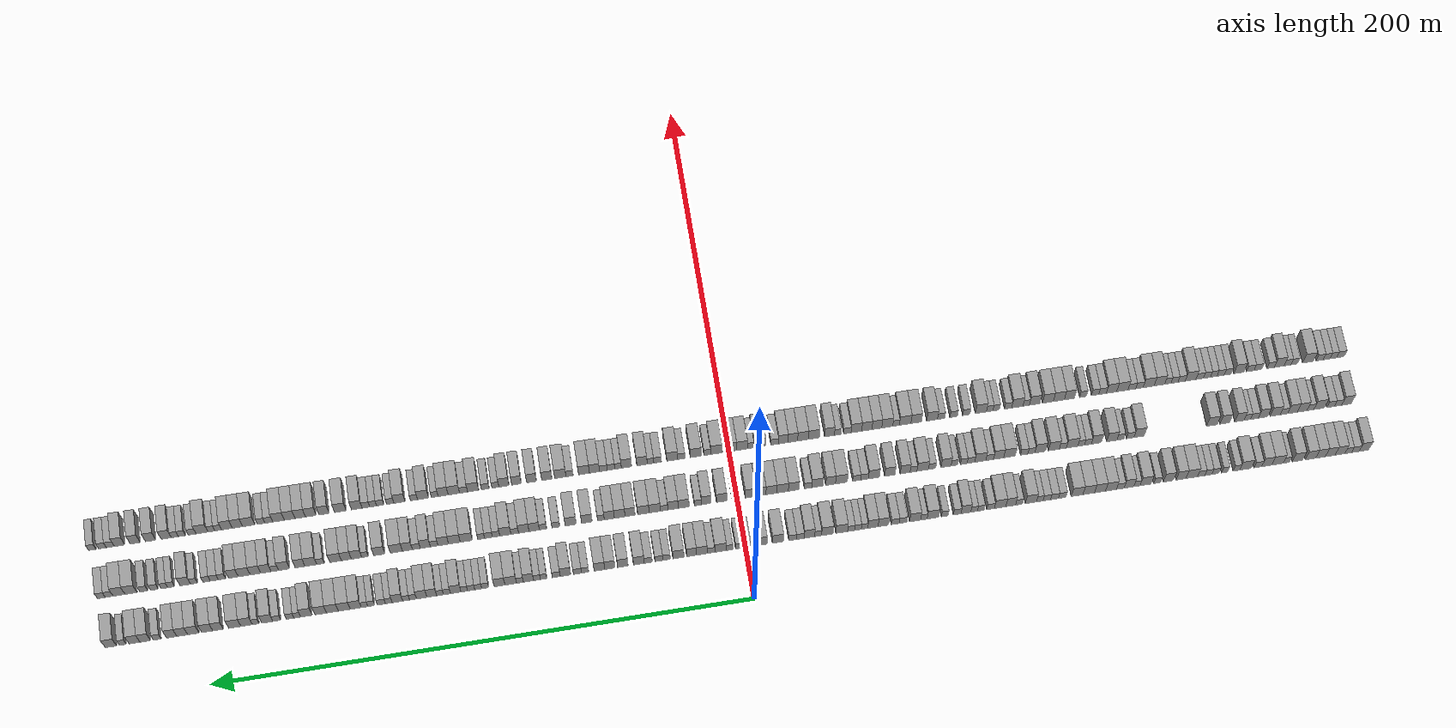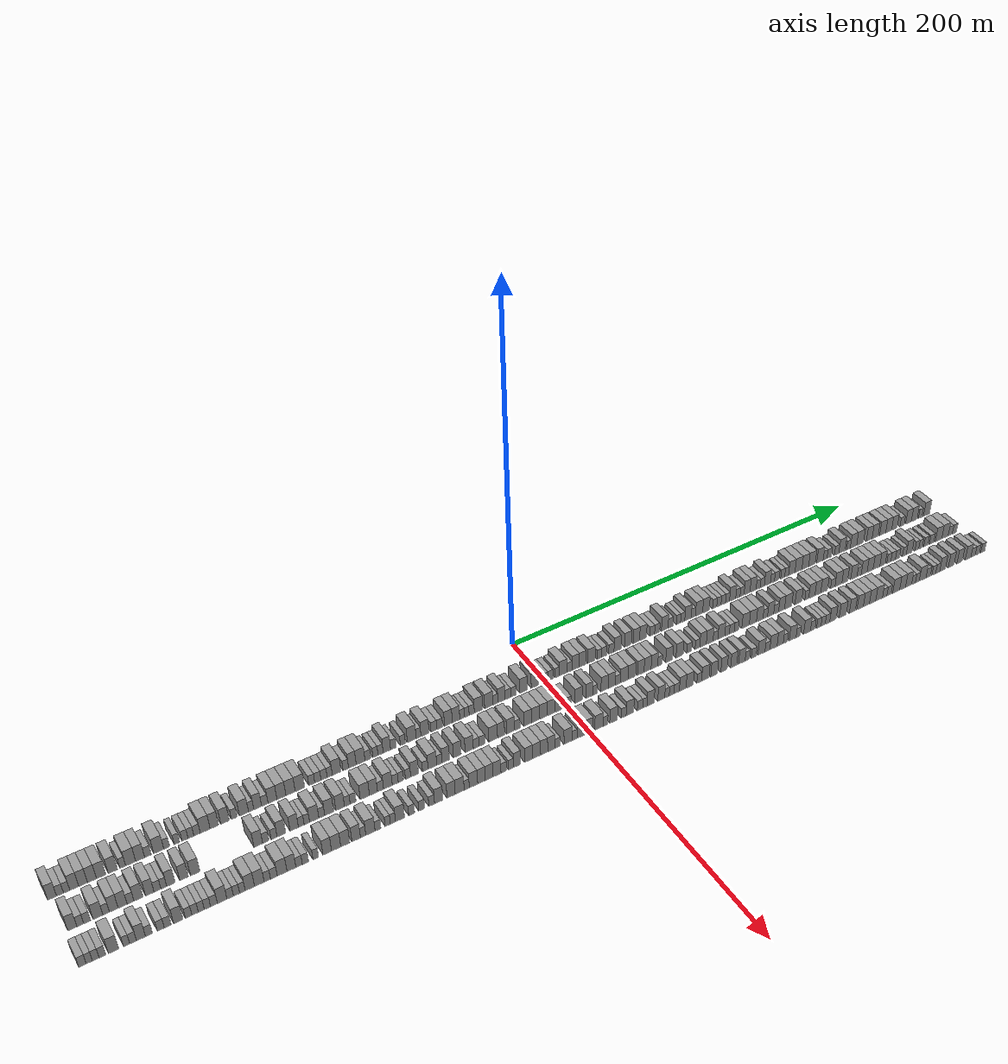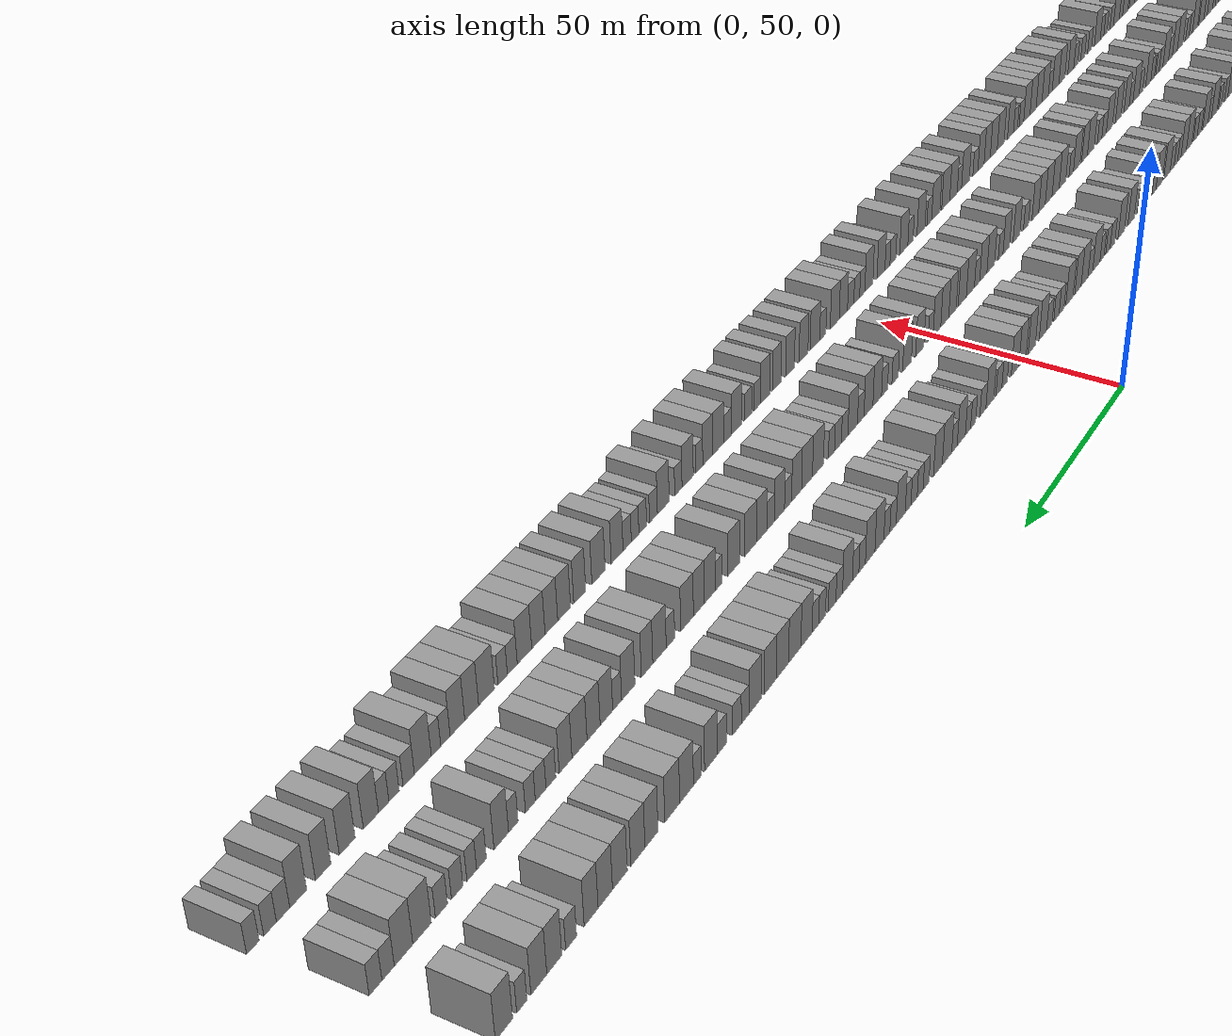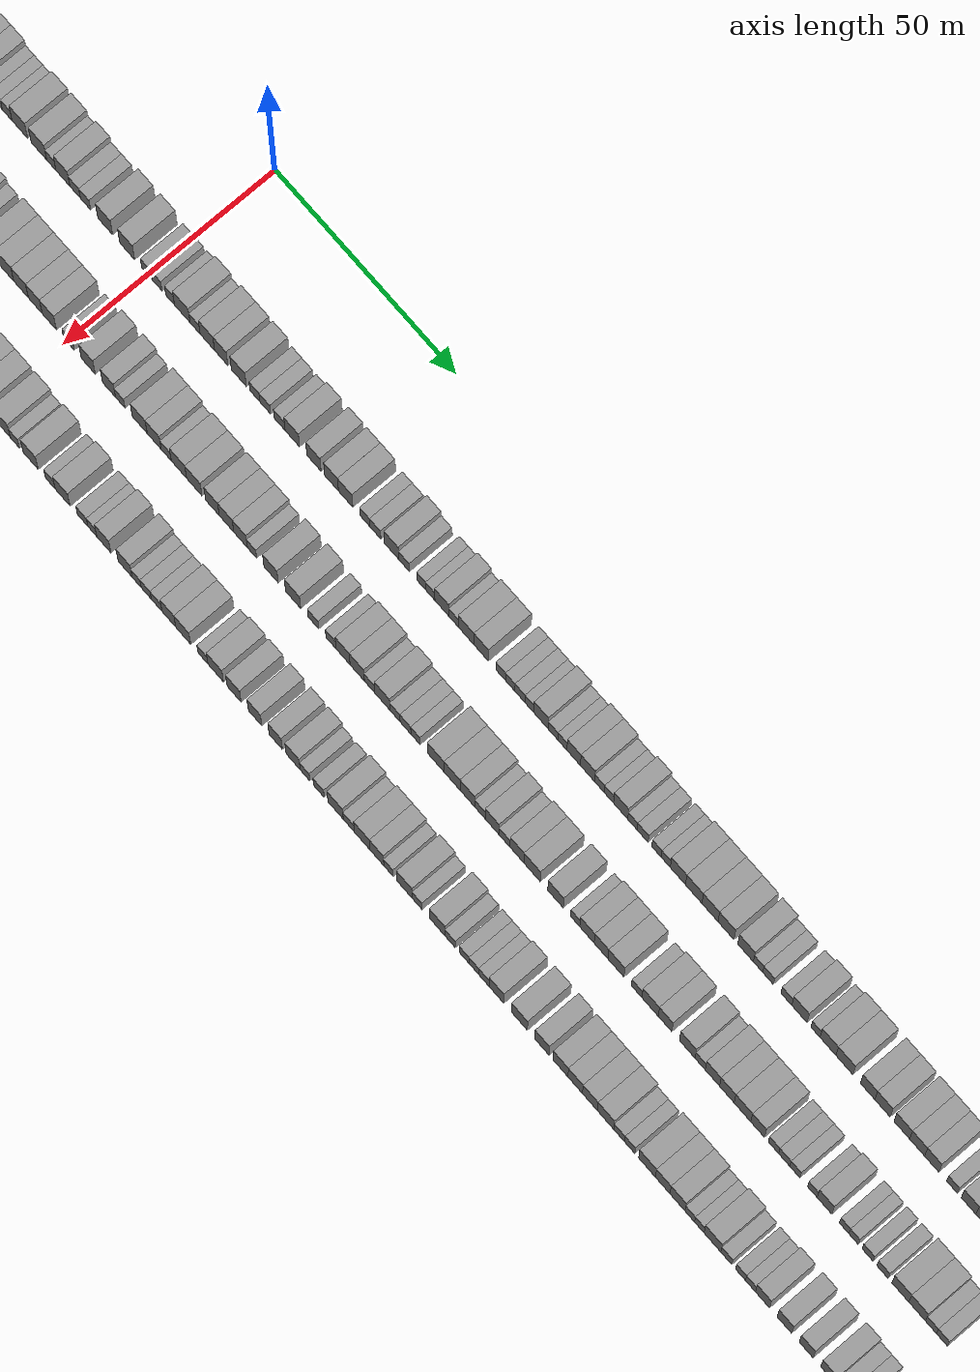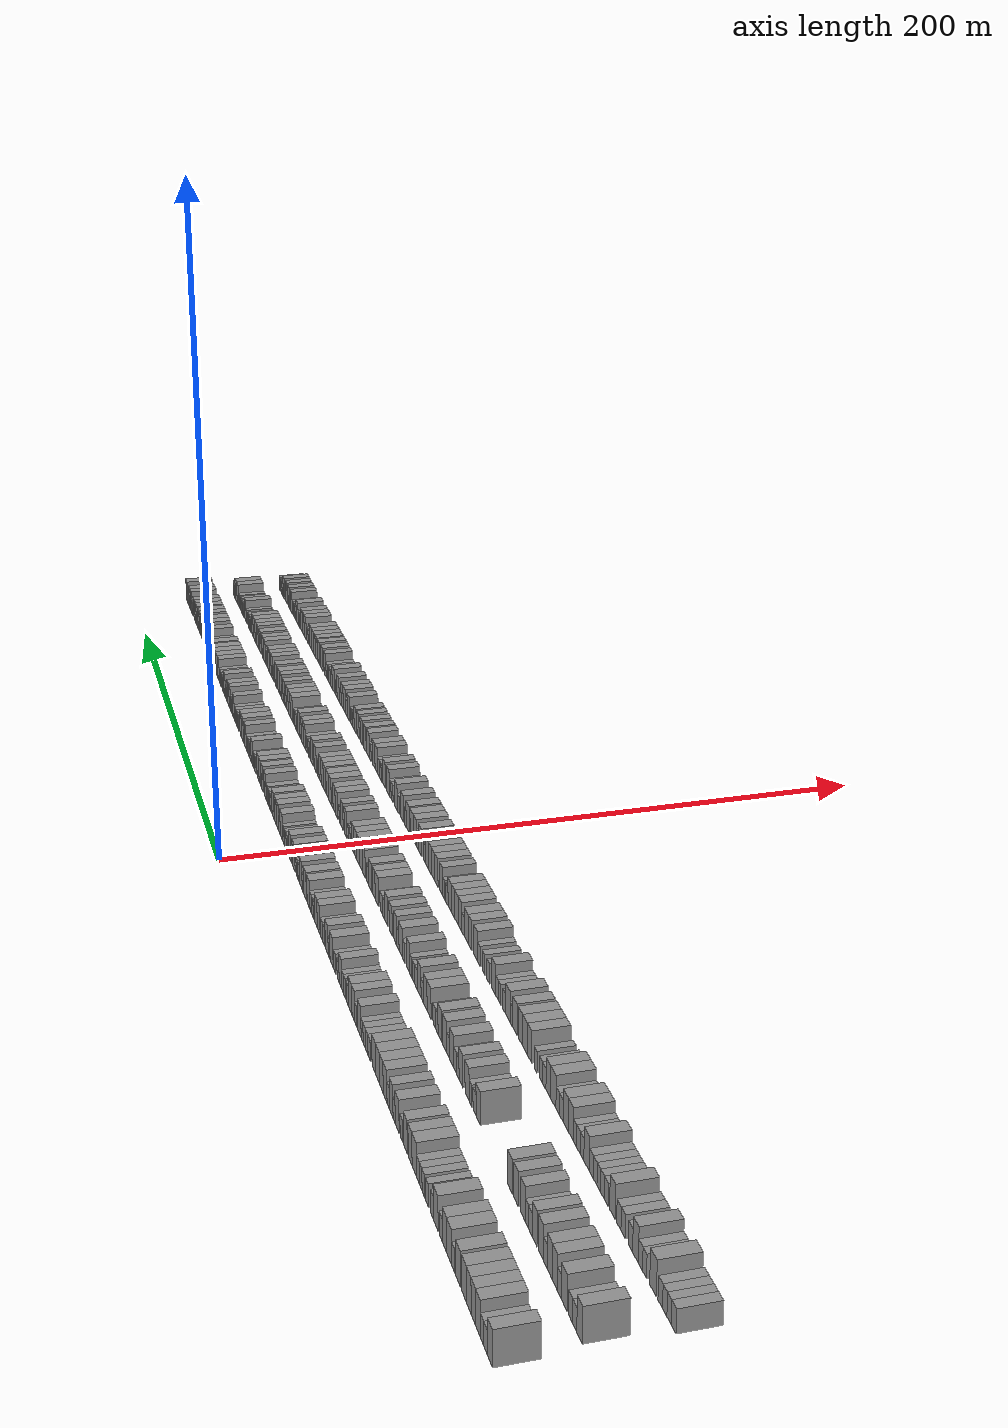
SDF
<sdf version="1.6">
 <world name="default">
  <scene>
   <sky><clouds><speed>12</speed></clouds></sky>
   <ambient>0.4 0.4 0.4 1</ambient>
   <background>0.7 0.7 0.7 1</background>
   <shadows>1</shadows>
  </scene>
  <gravity>0 0 -9.8066</gravity>
  <magnetic_field>6e-06 2.3e-05 -4.2e-05</magnetic_field>
  <physics default="0" name="default_physics" type="ode">
   <ode>
    <solver>
     <type>quick</type>
     <iters>10</iters>
     <sor>1.0</sor>
     <use_dynamic_moi_rescaling>0</use_dynamic_moi_rescaling>
    </solver>
    <constraints>
     <cfm>0</cfm>
     <erp>0.2</erp>
     <contact_max_correcting_vel>100</contact_max_correcting_vel>
     <contact_surface_layer>0.001</contact_surface_layer>
    </constraints>
   </ode>
   <max_step_size>0.004</max_step_size>
   <real_time_factor>1</real_time_factor>
   <real_time_update_rate>250</real_time_update_rate>
  </physics>
  <light name="sun" type="directional">
   <pose>0 0 10 0 0 0</pose>
   <diffuse>0.8 0.8 0.8 1</diffuse>
   <specular>0.2 0.2 0.2 1</specular>
   <attenuation>
    <range>1000</range>
    <constant>0.9</constant>
    <linear>0.01</linear>
    <quadratic>0.001</quadratic>
   </attenuation>
   <direction>-0.5 0.1 -0.9</direction>
  </light>
  <model name="building_1">
   <static>1</static>
   <pose>25.0000 -234.1658 0 0.000000 0.000000 0.000000</pose>
   <link name="link">
    <pose>0 0 4.50 0 0 0</pose>
    <collision name="collision"><geometry><box><size>10.0000 3.6684 9.0000</size></box></geometry></collision>
    <visual name="visual">
     <cast_shadows>0</cast_shadows>
     <geometry><box><size>10.0000 3.6684 9.0000</size></box></geometry>
     <material>
      <script>
       <uri>model://grey_wall/materials/scripts</uri>
       <uri>model://grey_wall/materials/textures</uri>
       <name>vrc/grey_wall</name>
      </script>
     </material>
    </visual>
   </link>
  </model>
  <model name="building_2">
   <static>1</static>
   <pose>25.0000 -230.8665 0 0.000000 0.000000 0.000000</pose>
   <link name="link">
    <pose>0 0 3.00 0 0 0</pose>
    <collision name="collision"><geometry><box><size>10.0000 2.9303 6.0000</size></box></geometry></collision>
    <visual name="visual">
     <cast_shadows>0</cast_shadows>
     <geometry><box><size>10.0000 2.9303 6.0000</size></box></geometry>
     <material>
      <script>
       <uri>model://grey_wall/materials/scripts</uri>
       <uri>model://grey_wall/materials/textures</uri>
       <name>vrc/grey_wall</name>
      </script>
     </material>
    </visual>
   </link>
  </model>
  <model name="building_3">
   <static>1</static>
   <pose>25.0000 -228.0963 0 0.000000 0.000000 0.000000</pose>
   <link name="link">
    <pose>0 0 3.00 0 0 0</pose>
    <collision name="collision"><geometry><box><size>10.0000 2.6101 6.0000</size></box></geometry></collision>
    <visual name="visual">
     <cast_shadows>0</cast_shadows>
     <geometry><box><size>10.0000 2.6101 6.0000</size></box></geometry>
     <material>
      <script>
       <uri>model://grey_wall/materials/scripts</uri>
       <uri>model://grey_wall/materials/textures</uri>
       <name>vrc/grey_wall</name>
      </script>
     </material>
    </visual>
   </link>
  </model>
  <model name="building_4">
   <static>1</static>
   <pose>25.0000 -224.9095 0 0.000000 0.000000 0.000000</pose>
   <link name="link">
    <pose>0 0 4.50 0 0 0</pose>
    <collision name="collision"><geometry><box><size>10.0000 3.7635 9.0000</size></box></geometry></collision>
    <visual name="visual">
     <cast_shadows>0</cast_shadows>
     <geometry><box><size>10.0000 3.7635 9.0000</size></box></geometry>
     <material>
      <script>
       <uri>model://grey_wall/materials/scripts</uri>
       <uri>model://grey_wall/materials/textures</uri>
       <name>vrc/grey_wall</name>
      </script>
     </material>
    </visual>
   </link>
  </model>
  <model name="building_5">
   <static>1</static>
   <pose>25.0000 -221.1921 0 0.000000 0.000000 0.000000</pose>
   <link name="link">
    <pose>0 0 4.50 0 0 0</pose>
    <collision name="collision"><geometry><box><size>10.0000 3.6712 9.0000</size></box></geometry></collision>
    <visual name="visual">
     <cast_shadows>0</cast_shadows>
     <geometry><box><size>10.0000 3.6712 9.0000</size></box></geometry>
     <material>
      <script>
       <uri>model://grey_wall/materials/scripts</uri>
       <uri>model://grey_wall/materials/textures</uri>
       <name>vrc/grey_wall</name>
      </script>
     </material>
    </visual>
   </link>
  </model>
  <model name="building_6">
   <static>1</static>
   <pose>25.0000 -217.4901 0 0.000000 0.000000 0.000000</pose>
   <link name="link">
    <pose>0 0 4.50 0 0 0</pose>
    <collision name="collision"><geometry><box><size>10.0000 3.7329 9.0000</size></box></geometry></collision>
    <visual name="visual">
     <cast_shadows>0</cast_shadows>
     <geometry><box><size>10.0000 3.7329 9.0000</size></box></geometry>
     <material>
      <script>
       <uri>model://grey_wall/materials/scripts</uri>
       <uri>model://grey_wall/materials/textures</uri>
       <name>vrc/grey_wall</name>
      </script>
     </material>
    </visual>
   </link>
  </model>
  <model name="building_7">
   <static>1</static>
   <pose>25.0000 -213.6293 0 0.000000 0.000000 0.000000</pose>
   <link name="link">
    <pose>0 0 4.50 0 0 0</pose>
    <collision name="collision"><geometry><box><size>10.0000 3.9886 9.0000</size></box></geometry></collision>
    <visual name="visual">
     <cast_shadows>0</cast_shadows>
     <geometry><box><size>10.0000 3.9886 9.0000</size></box></geometry>
     <material>
      <script>
       <uri>model://grey_wall/materials/scripts</uri>
       <uri>model://grey_wall/materials/textures</uri>
       <name>vrc/grey_wall</name>
      </script>
     </material>
    </visual>
   </link>
  </model>
  <model name="building_8">
   <static>1</static>
   <pose>25.0000 -208.6443 0 0.000000 0.000000 0.000000</pose>
   <link name="link">
    <pose>0 0 4.50 0 0 0</pose>
    <collision name="collision"><geometry><box><size>10.0000 3.9814 9.0000</size></box></geometry></collision>
    <visual name="visual">
     <cast_shadows>0</cast_shadows>
     <geometry><box><size>10.0000 3.9814 9.0000</size></box></geometry>
     <material>
      <script>
       <uri>model://grey_wall/materials/scripts</uri>
       <uri>model://grey_wall/materials/textures</uri>
       <name>vrc/grey_wall</name>
      </script>
     </material>
    </visual>
   </link>
  </model>
  <model name="building_9">
   <static>1</static>
   <pose>25.0000 -204.4172 0 0.000000 0.000000 0.000000</pose>
   <link name="link">
    <pose>0 0 3.00 0 0 0</pose>
    <collision name="collision"><geometry><box><size>10.0000 2.4729 6.0000</size></box></geometry></collision>
    <visual name="visual">
     <cast_shadows>0</cast_shadows>
     <geometry><box><size>10.0000 2.4729 6.0000</size></box></geometry>
     <material>
      <script>
       <uri>model://grey_wall/materials/scripts</uri>
       <uri>model://grey_wall/materials/textures</uri>
       <name>vrc/grey_wall</name>
      </script>
     </material>
    </visual>
   </link>
  </model>
  <model name="building_10">
   <static>1</static>
   <pose>25.0000 -201.0050 0 0.000000 0.000000 0.000000</pose>
   <link name="link">
    <pose>0 0 4.50 0 0 0</pose>
    <collision name="collision"><geometry><box><size>10.0000 4.3516 9.0000</size></box></geometry></collision>
    <visual name="visual">
     <cast_shadows>0</cast_shadows>
     <geometry><box><size>10.0000 4.3516 9.0000</size></box></geometry>
     <material>
      <script>
       <uri>model://grey_wall/materials/scripts</uri>
       <uri>model://grey_wall/materials/textures</uri>
       <name>vrc/grey_wall</name>
      </script>
     </material>
    </visual>
   </link>
  </model>
  <model name="building_11">
   <static>1</static>
   <pose>25.0000 -196.9007 0 0.000000 0.000000 0.000000</pose>
   <link name="link">
    <pose>0 0 4.50 0 0 0</pose>
    <collision name="collision"><geometry><box><size>10.0000 3.8571 9.0000</size></box></geometry></collision>
    <visual name="visual">
     <cast_shadows>0</cast_shadows>
     <geometry><box><size>10.0000 3.8571 9.0000</size></box></geometry>
     <material>
      <script>
       <uri>model://grey_wall/materials/scripts</uri>
       <uri>model://grey_wall/materials/textures</uri>
       <name>vrc/grey_wall</name>
      </script>
     </material>
    </visual>
   </link>
  </model>
  <model name="building_12">
   <static>1</static>
   <pose>25.0000 -193.5009 0 0.000000 0.000000 0.000000</pose>
   <link name="link">
    <pose>0 0 3.00 0 0 0</pose>
    <collision name="collision"><geometry><box><size>10.0000 2.9424 6.0000</size></box></geometry></collision>
    <visual name="visual">
     <cast_shadows>0</cast_shadows>
     <geometry><box><size>10.0000 2.9424 6.0000</size></box></geometry>
     <material>
      <script>
       <uri>model://grey_wall/materials/scripts</uri>
       <uri>model://grey_wall/materials/textures</uri>
       <name>vrc/grey_wall</name>
      </script>
     </material>
    </visual>
   </link>
  </model>
  <model name="building_13">
   <static>1</static>
   <pose>25.0000 -188.8148 0 0.000000 0.000000 0.000000</pose>
   <link name="link">
    <pose>0 0 4.50 0 0 0</pose>
    <collision name="collision"><geometry><box><size>10.0000 4.4298 9.0000</size></box></geometry></collision>
    <visual name="visual">
     <cast_shadows>0</cast_shadows>
     <geometry><box><size>10.0000 4.4298 9.0000</size></box></geometry>
     <material>
      <script>
       <uri>model://grey_wall/materials/scripts</uri>
       <uri>model://grey_wall/materials/textures</uri>
       <name>vrc/grey_wall</name>
      </script>
     </material>
    </visual>
   </link>
  </model>
  <model name="building_14">
   <static>1</static>
   <pose>25.0000 -185.3080 0 0.000000 0.000000 0.000000</pose>
   <link name="link">
    <pose>0 0 3.00 0 0 0</pose>
    <collision name="collision"><geometry><box><size>10.0000 2.5838 6.0000</size></box></geometry></collision>
    <visual name="visual">
     <cast_shadows>0</cast_shadows>
     <geometry><box><size>10.0000 2.5838 6.0000</size></box></geometry>
     <material>
      <script>
       <uri>model://grey_wall/materials/scripts</uri>
       <uri>model://grey_wall/materials/textures</uri>
       <name>vrc/grey_wall</name>
      </script>
     </material>
    </visual>
   </link>
  </model>
  <model name="building_15">
   <static>1</static>
   <pose>25.0000 -180.8055 0 0.000000 0.000000 0.000000</pose>
   <link name="link">
    <pose>0 0 3.00 0 0 0</pose>
    <collision name="collision"><geometry><box><size>10.0000 2.4212 6.0000</size></box></geometry></collision>
    <visual name="visual">
     <cast_shadows>0</cast_shadows>
     <geometry><box><size>10.0000 2.4212 6.0000</size></box></geometry>
     <material>
      <script>
       <uri>model://grey_wall/materials/scripts</uri>
       <uri>model://grey_wall/materials/textures</uri>
       <name>vrc/grey_wall</name>
      </script>
     </material>
    </visual>
   </link>
  </model>
  <model name="building_16">
   <static>1</static>
   <pose>25.0000 -177.2514 0 0.000000 0.000000 0.000000</pose>
   <link name="link">
    <pose>0 0 3.00 0 0 0</pose>
    <collision name="collision"><geometry><box><size>10.0000 2.6870 6.0000</size></box></geometry></collision>
    <visual name="visual">
     <cast_shadows>0</cast_shadows>
     <geometry><box><size>10.0000 2.6870 6.0000</size></box></geometry>
     <material>
      <script>
       <uri>model://grey_wall/materials/scripts</uri>
       <uri>model://grey_wall/materials/textures</uri>
       <name>vrc/grey_wall</name>
      </script>
     </material>
    </visual>
   </link>
  </model>
  <model name="building_17">
   <static>1</static>
   <pose>25.0000 -174.6028 0 0.000000 0.000000 0.000000</pose>
   <link name="link">
    <pose>0 0 3.00 0 0 0</pose>
    <collision name="collision"><geometry><box><size>10.0000 2.6101 6.0000</size></box></geometry></collision>
    <visual name="visual">
     <cast_shadows>0</cast_shadows>
     <geometry><box><size>10.0000 2.6101 6.0000</size></box></geometry>
     <material>
      <script>
       <uri>model://grey_wall/materials/scripts</uri>
       <uri>model://grey_wall/materials/textures</uri>
       <name>vrc/grey_wall</name>
      </script>
     </material>
    </visual>
   </link>
  </model>
  <model name="building_18">
   <static>1</static>
   <pose>25.0000 -171.8830 0 0.000000 0.000000 0.000000</pose>
   <link name="link">
    <pose>0 0 3.00 0 0 0</pose>
    <collision name="collision"><geometry><box><size>10.0000 2.8294 6.0000</size></box></geometry></collision>
    <visual name="visual">
     <cast_shadows>0</cast_shadows>
     <geometry><box><size>10.0000 2.8294 6.0000</size></box></geometry>
     <material>
      <script>
       <uri>model://grey_wall/materials/scripts</uri>
       <uri>model://grey_wall/materials/textures</uri>
       <name>vrc/grey_wall</name>
      </script>
     </material>
    </visual>
   </link>
  </model>
  <model name="building_19">
   <static>1</static>
   <pose>25.0000 -168.2579 0 0.000000 0.000000 0.000000</pose>
   <link name="link">
    <pose>0 0 4.50 0 0 0</pose>
    <collision name="collision"><geometry><box><size>10.0000 4.4210 9.0000</size></box></geometry></collision>
    <visual name="visual">
     <cast_shadows>0</cast_shadows>
     <geometry><box><size>10.0000 4.4210 9.0000</size></box></geometry>
     <material>
      <script>
       <uri>model://grey_wall/materials/scripts</uri>
       <uri>model://grey_wall/materials/textures</uri>
       <name>vrc/grey_wall</name>
      </script>
     </material>
    </visual>
   </link>
  </model>
  <model name="building_20">
   <static>1</static>
   <pose>25.0000 -164.1533 0 0.000000 0.000000 0.000000</pose>
   <link name="link">
    <pose>0 0 4.50 0 0 0</pose>
    <collision name="collision"><geometry><box><size>10.0000 3.7882 9.0000</size></box></geometry></collision>
    <visual name="visual">
     <cast_shadows>0</cast_shadows>
     <geometry><box><size>10.0000 3.7882 9.0000</size></box></geometry>
     <material>
      <script>
       <uri>model://grey_wall/materials/scripts</uri>
       <uri>model://grey_wall/materials/textures</uri>
       <name>vrc/grey_wall</name>
      </script>
     </material>
    </visual>
   </link>
  </model>
  <model name="building_21">
   <static>1</static>
   <pose>25.0000 -159.3294 0 0.000000 0.000000 0.000000</pose>
   <link name="link">
    <pose>0 0 4.50 0 0 0</pose>
    <collision name="collision"><geometry><box><size>10.0000 3.8596 9.0000</size></box></geometry></collision>
    <visual name="visual">
     <cast_shadows>0</cast_shadows>
     <geometry><box><size>10.0000 3.8596 9.0000</size></box></geometry>
     <material>
      <script>
       <uri>model://grey_wall/materials/scripts</uri>
       <uri>model://grey_wall/materials/textures</uri>
       <name>vrc/grey_wall</name>
      </script>
     </material>
    </visual>
   </link>
  </model>
  <model name="building_22">
   <static>1</static>
   <pose>25.0000 -155.0684 0 0.000000 0.000000 0.000000</pose>
   <link name="link">
    <pose>0 0 3.00 0 0 0</pose>
    <collision name="collision"><geometry><box><size>10.0000 2.6623 6.0000</size></box></geometry></collision>
    <visual name="visual">
     <cast_shadows>0</cast_shadows>
     <geometry><box><size>10.0000 2.6623 6.0000</size></box></geometry>
     <material>
      <script>
       <uri>model://grey_wall/materials/scripts</uri>
       <uri>model://grey_wall/materials/textures</uri>
       <name>vrc/grey_wall</name>
      </script>
     </material>
    </visual>
   </link>
  </model>
  <model name="building_23">
   <static>1</static>
   <pose>25.0000 -150.6576 0 0.000000 0.000000 0.000000</pose>
   <link name="link">
    <pose>0 0 4.50 0 0 0</pose>
    <collision name="collision"><geometry><box><size>10.0000 4.1593 9.0000</size></box></geometry></collision>
    <visual name="visual">
     <cast_shadows>0</cast_shadows>
     <geometry><box><size>10.0000 4.1593 9.0000</size></box></geometry>
     <material>
      <script>
       <uri>model://grey_wall/materials/scripts</uri>
       <uri>model://grey_wall/materials/textures</uri>
       <name>vrc/grey_wall</name>
      </script>
     </material>
    </visual>
   </link>
  </model>
  <model name="building_24">
   <static>1</static>
   <pose>25.0000 -147.3732 0 0.000000 0.000000 0.000000</pose>
   <link name="link">
    <pose>0 0 3.00 0 0 0</pose>
    <collision name="collision"><geometry><box><size>10.0000 2.4095 6.0000</size></box></geometry></collision>
    <visual name="visual">
     <cast_shadows>0</cast_shadows>
     <geometry><box><size>10.0000 2.4095 6.0000</size></box></geometry>
     <material>
      <script>
       <uri>model://grey_wall/materials/scripts</uri>
       <uri>model://grey_wall/materials/textures</uri>
       <name>vrc/grey_wall</name>
      </script>
     </material>
    </visual>
   </link>
  </model>
  <model name="building_25">
   <static>1</static>
   <pose>25.0000 -144.3496 0 0.000000 0.000000 0.000000</pose>
   <link name="link">
    <pose>0 0 4.50 0 0 0</pose>
    <collision name="collision"><geometry><box><size>10.0000 3.6378 9.0000</size></box></geometry></collision>
    <visual name="visual">
     <cast_shadows>0</cast_shadows>
     <geometry><box><size>10.0000 3.6378 9.0000</size></box></geometry>
     <material>
      <script>
       <uri>model://grey_wall/materials/scripts</uri>
       <uri>model://grey_wall/materials/textures</uri>
       <name>vrc/grey_wall</name>
      </script>
     </material>
    </visual>
   </link>
  </model>
  <model name="building_26">
   <static>1</static>
   <pose>25.0000 -141.0461 0 0.000000 0.000000 0.000000</pose>
   <link name="link">
    <pose>0 0 3.00 0 0 0</pose>
    <collision name="collision"><geometry><box><size>10.0000 2.9692 6.0000</size></box></geometry></collision>
    <visual name="visual">
     <cast_shadows>0</cast_shadows>
     <geometry><box><size>10.0000 2.9692 6.0000</size></box></geometry>
     <material>
      <script>
       <uri>model://grey_wall/materials/scripts</uri>
       <uri>model://grey_wall/materials/textures</uri>
       <name>vrc/grey_wall</name>
      </script>
     </material>
    </visual>
   </link>
  </model>
  <model name="building_27">
   <static>1</static>
   <pose>25.0000 -137.4923 0 0.000000 0.000000 0.000000</pose>
   <link name="link">
    <pose>0 0 4.50 0 0 0</pose>
    <collision name="collision"><geometry><box><size>10.0000 4.1385 9.0000</size></box></geometry></collision>
    <visual name="visual">
     <cast_shadows>0</cast_shadows>
     <geometry><box><size>10.0000 4.1385 9.0000</size></box></geometry>
     <material>
      <script>
       <uri>model://grey_wall/materials/scripts</uri>
       <uri>model://grey_wall/materials/textures</uri>
       <name>vrc/grey_wall</name>
      </script>
     </material>
    </visual>
   </link>
  </model>
  <model name="building_28">
   <static>1</static>
   <pose>25.0000 -133.3232 0 0.000000 0.000000 0.000000</pose>
   <link name="link">
    <pose>0 0 4.50 0 0 0</pose>
    <collision name="collision"><geometry><box><size>10.0000 4.1997 9.0000</size></box></geometry></collision>
    <visual name="visual">
     <cast_shadows>0</cast_shadows>
     <geometry><box><size>10.0000 4.1997 9.0000</size></box></geometry>
     <material>
      <script>
       <uri>model://grey_wall/materials/scripts</uri>
       <uri>model://grey_wall/materials/textures</uri>
       <name>vrc/grey_wall</name>
      </script>
     </material>
    </visual>
   </link>
  </model>
  <model name="building_29">
   <static>1</static>
   <pose>25.0000 -129.0374 0 0.000000 0.000000 0.000000</pose>
   <link name="link">
    <pose>0 0 4.50 0 0 0</pose>
    <collision name="collision"><geometry><box><size>10.0000 4.3717 9.0000</size></box></geometry></collision>
    <visual name="visual">
     <cast_shadows>0</cast_shadows>
     <geometry><box><size>10.0000 4.3717 9.0000</size></box></geometry>
     <material>
      <script>
       <uri>model://grey_wall/materials/scripts</uri>
       <uri>model://grey_wall/materials/textures</uri>
       <name>vrc/grey_wall</name>
      </script>
     </material>
    </visual>
   </link>
  </model>
  <model name="building_30">
   <static>1</static>
   <pose>25.0000 -124.6310 0 0.000000 0.000000 0.000000</pose>
   <link name="link">
    <pose>0 0 4.50 0 0 0</pose>
    <collision name="collision"><geometry><box><size>10.0000 4.4412 9.0000</size></box></geometry></collision>
    <visual name="visual">
     <cast_shadows>0</cast_shadows>
     <geometry><box><size>10.0000 4.4412 9.0000</size></box></geometry>
     <material>
      <script>
       <uri>model://grey_wall/materials/scripts</uri>
       <uri>model://grey_wall/materials/textures</uri>
       <name>vrc/grey_wall</name>
      </script>
     </material>
    </visual>
   </link>
  </model>
  <model name="building_31">
   <static>1</static>
   <pose>25.0000 -118.9994 0 0.000000 0.000000 0.000000</pose>
   <link name="link">
    <pose>0 0 3.00 0 0 0</pose>
    <collision name="collision"><geometry><box><size>10.0000 2.8219 6.0000</size></box></geometry></collision>
    <visual name="visual">
     <cast_shadows>0</cast_shadows>
     <geometry><box><size>10.0000 2.8219 6.0000</size></box></geometry>
     <material>
      <script>
       <uri>model://grey_wall/materials/scripts</uri>
       <uri>model://grey_wall/materials/textures</uri>
       <name>vrc/grey_wall</name>
      </script>
     </material>
    </visual>
   </link>
  </model>
  <model name="building_32">
   <static>1</static>
   <pose>25.0000 -116.1071 0 0.000000 0.000000 0.000000</pose>
   <link name="link">
    <pose>0 0 3.00 0 0 0</pose>
    <collision name="collision"><geometry><box><size>10.0000 2.9627 6.0000</size></box></geometry></collision>
    <visual name="visual">
     <cast_shadows>0</cast_shadows>
     <geometry><box><size>10.0000 2.9627 6.0000</size></box></geometry>
     <material>
      <script>
       <uri>model://grey_wall/materials/scripts</uri>
       <uri>model://grey_wall/materials/textures</uri>
       <name>vrc/grey_wall</name>
      </script>
     </material>
    </visual>
   </link>
  </model>
  <model name="building_33">
   <static>1</static>
   <pose>25.0000 -113.1635 0 0.000000 0.000000 0.000000</pose>
   <link name="link">
    <pose>0 0 3.00 0 0 0</pose>
    <collision name="collision"><geometry><box><size>10.0000 2.9245 6.0000</size></box></geometry></collision>
    <visual name="visual">
     <cast_shadows>0</cast_shadows>
     <geometry><box><size>10.0000 2.9245 6.0000</size></box></geometry>
     <material>
      <script>
       <uri>model://grey_wall/materials/scripts</uri>
       <uri>model://grey_wall/materials/textures</uri>
       <name>vrc/grey_wall</name>
      </script>
     </material>
    </visual>
   </link>
  </model>
  <model name="building_34">
   <static>1</static>
   <pose>25.0000 -110.4510 0 0.000000 0.000000 0.000000</pose>
   <link name="link">
    <pose>0 0 3.00 0 0 0</pose>
    <collision name="collision"><geometry><box><size>10.0000 2.5004 6.0000</size></box></geometry></collision>
    <visual name="visual">
     <cast_shadows>0</cast_shadows>
     <geometry><box><size>10.0000 2.5004 6.0000</size></box></geometry>
     <material>
      <script>
       <uri>model://grey_wall/materials/scripts</uri>
       <uri>model://grey_wall/materials/textures</uri>
       <name>vrc/grey_wall</name>
      </script>
     </material>
    </visual>
   </link>
  </model>
  <model name="building_35">
   <static>1</static>
   <pose>25.0000 -107.1055 0 0.000000 0.000000 0.000000</pose>
   <link name="link">
    <pose>0 0 4.50 0 0 0</pose>
    <collision name="collision"><geometry><box><size>10.0000 4.1905 9.0000</size></box></geometry></collision>
    <visual name="visual">
     <cast_shadows>0</cast_shadows>
     <geometry><box><size>10.0000 4.1905 9.0000</size></box></geometry>
     <material>
      <script>
       <uri>model://grey_wall/materials/scripts</uri>
       <uri>model://grey_wall/materials/textures</uri>
       <name>vrc/grey_wall</name>
      </script>
     </material>
    </visual>
   </link>
  </model>
  <model name="building_36">
   <static>1</static>
   <pose>25.0000 -102.6705 0 0.000000 0.000000 0.000000</pose>
   <link name="link">
    <pose>0 0 3.00 0 0 0</pose>
    <collision name="collision"><geometry><box><size>10.0000 2.6795 6.0000</size></box></geometry></collision>
    <visual name="visual">
     <cast_shadows>0</cast_shadows>
     <geometry><box><size>10.0000 2.6795 6.0000</size></box></geometry>
     <material>
      <script>
       <uri>model://grey_wall/materials/scripts</uri>
       <uri>model://grey_wall/materials/textures</uri>
       <name>vrc/grey_wall</name>
      </script>
     </material>
    </visual>
   </link>
  </model>
  <model name="building_37">
   <static>1</static>
   <pose>25.0000 -99.4824 0 0.000000 0.000000 0.000000</pose>
   <link name="link">
    <pose>0 0 4.50 0 0 0</pose>
    <collision name="collision"><geometry><box><size>10.0000 3.6967 9.0000</size></box></geometry></collision>
    <visual name="visual">
     <cast_shadows>0</cast_shadows>
     <geometry><box><size>10.0000 3.6967 9.0000</size></box></geometry>
     <material>
      <script>
       <uri>model://grey_wall/materials/scripts</uri>
       <uri>model://grey_wall/materials/textures</uri>
       <name>vrc/grey_wall</name>
      </script>
     </material>
    </visual>
   </link>
  </model>
  <model name="building_38">
   <static>1</static>
   <pose>25.0000 -95.4856 0 0.000000 0.000000 0.000000</pose>
   <link name="link">
    <pose>0 0 4.50 0 0 0</pose>
    <collision name="collision"><geometry><box><size>10.0000 4.2970 9.0000</size></box></geometry></collision>
    <visual name="visual">
     <cast_shadows>0</cast_shadows>
     <geometry><box><size>10.0000 4.2970 9.0000</size></box></geometry>
     <material>
      <script>
       <uri>model://grey_wall/materials/scripts</uri>
       <uri>model://grey_wall/materials/textures</uri>
       <name>vrc/grey_wall</name>
      </script>
     </material>
    </visual>
   </link>
  </model>
  <model name="building_39">
   <static>1</static>
   <pose>25.0000 -91.8890 0 0.000000 0.000000 0.000000</pose>
   <link name="link">
    <pose>0 0 3.00 0 0 0</pose>
    <collision name="collision"><geometry><box><size>10.0000 2.8961 6.0000</size></box></geometry></collision>
    <visual name="visual">
     <cast_shadows>0</cast_shadows>
     <geometry><box><size>10.0000 2.8961 6.0000</size></box></geometry>
     <material>
      <script>
       <uri>model://grey_wall/materials/scripts</uri>
       <uri>model://grey_wall/materials/textures</uri>
       <name>vrc/grey_wall</name>
      </script>
     </material>
    </visual>
   </link>
  </model>
  <model name="building_40">
   <static>1</static>
   <pose>25.0000 -88.1991 0 0.000000 0.000000 0.000000</pose>
   <link name="link">
    <pose>0 0 3.00 0 0 0</pose>
    <collision name="collision"><geometry><box><size>10.0000 2.4836 6.0000</size></box></geometry></collision>
    <visual name="visual">
     <cast_shadows>0</cast_shadows>
     <geometry><box><size>10.0000 2.4836 6.0000</size></box></geometry>
     <material>
      <script>
       <uri>model://grey_wall/materials/scripts</uri>
       <uri>model://grey_wall/materials/textures</uri>
       <name>vrc/grey_wall</name>
      </script>
     </material>
    </visual>
   </link>
  </model>
  <model name="building_41">
   <static>1</static>
   <pose>25.0000 -85.6586 0 0.000000 0.000000 0.000000</pose>
   <link name="link">
    <pose>0 0 3.00 0 0 0</pose>
    <collision name="collision"><geometry><box><size>10.0000 2.5976 6.0000</size></box></geometry></collision>
    <visual name="visual">
     <cast_shadows>0</cast_shadows>
     <geometry><box><size>10.0000 2.5976 6.0000</size></box></geometry>
     <material>
      <script>
       <uri>model://grey_wall/materials/scripts</uri>
       <uri>model://grey_wall/materials/textures</uri>
       <name>vrc/grey_wall</name>
      </script>
     </material>
    </visual>
   </link>
  </model>
  <model name="building_42">
   <static>1</static>
   <pose>25.0000 -82.5263 0 0.000000 0.000000 0.000000</pose>
   <link name="link">
    <pose>0 0 4.50 0 0 0</pose>
    <collision name="collision"><geometry><box><size>10.0000 3.6670 9.0000</size></box></geometry></collision>
    <visual name="visual">
     <cast_shadows>0</cast_shadows>
     <geometry><box><size>10.0000 3.6670 9.0000</size></box></geometry>
     <material>
      <script>
       <uri>model://grey_wall/materials/scripts</uri>
       <uri>model://grey_wall/materials/textures</uri>
       <name>vrc/grey_wall</name>
      </script>
     </material>
    </visual>
   </link>
  </model>
  <model name="building_43">
   <static>1</static>
   <pose>25.0000 -79.2621 0 0.000000 0.000000 0.000000</pose>
   <link name="link">
    <pose>0 0 3.00 0 0 0</pose>
    <collision name="collision"><geometry><box><size>10.0000 2.8615 6.0000</size></box></geometry></collision>
    <visual name="visual">
     <cast_shadows>0</cast_shadows>
     <geometry><box><size>10.0000 2.8615 6.0000</size></box></geometry>
     <material>
      <script>
       <uri>model://grey_wall/materials/scripts</uri>
       <uri>model://grey_wall/materials/textures</uri>
       <name>vrc/grey_wall</name>
      </script>
     </material>
    </visual>
   </link>
  </model>
  <model name="building_44">
   <static>1</static>
   <pose>25.0000 -74.5760 0 0.000000 0.000000 0.000000</pose>
   <link name="link">
    <pose>0 0 3.00 0 0 0</pose>
    <collision name="collision"><geometry><box><size>10.0000 2.5107 6.0000</size></box></geometry></collision>
    <visual name="visual">
     <cast_shadows>0</cast_shadows>
     <geometry><box><size>10.0000 2.5107 6.0000</size></box></geometry>
     <material>
      <script>
       <uri>model://grey_wall/materials/scripts</uri>
       <uri>model://grey_wall/materials/textures</uri>
       <name>vrc/grey_wall</name>
      </script>
     </material>
    </visual>
   </link>
  </model>
  <model name="building_45">
   <static>1</static>
   <pose>25.0000 -70.1076 0 0.000000 0.000000 0.000000</pose>
   <link name="link">
    <pose>0 0 4.50 0 0 0</pose>
    <collision name="collision"><geometry><box><size>10.0000 4.4260 9.0000</size></box></geometry></collision>
    <visual name="visual">
     <cast_shadows>0</cast_shadows>
     <geometry><box><size>10.0000 4.4260 9.0000</size></box></geometry>
     <material>
      <script>
       <uri>model://grey_wall/materials/scripts</uri>
       <uri>model://grey_wall/materials/textures</uri>
       <name>vrc/grey_wall</name>
      </script>
     </material>
    </visual>
   </link>
  </model>
  <model name="building_46">
   <static>1</static>
   <pose>25.0000 -66.6672 0 0.000000 0.000000 0.000000</pose>
   <link name="link">
    <pose>0 0 3.00 0 0 0</pose>
    <collision name="collision"><geometry><box><size>10.0000 2.4548 6.0000</size></box></geometry></collision>
    <visual name="visual">
     <cast_shadows>0</cast_shadows>
     <geometry><box><size>10.0000 2.4548 6.0000</size></box></geometry>
     <material>
      <script>
       <uri>model://grey_wall/materials/scripts</uri>
       <uri>model://grey_wall/materials/textures</uri>
       <name>vrc/grey_wall</name>
      </script>
     </material>
    </visual>
   </link>
  </model>
  <model name="building_47">
   <static>1</static>
   <pose>25.0000 -63.3908 0 0.000000 0.000000 0.000000</pose>
   <link name="link">
    <pose>0 0 4.50 0 0 0</pose>
    <collision name="collision"><geometry><box><size>10.0000 4.0981 9.0000</size></box></geometry></collision>
    <visual name="visual">
     <cast_shadows>0</cast_shadows>
     <geometry><box><size>10.0000 4.0981 9.0000</size></box></geometry>
     <material>
      <script>
       <uri>model://grey_wall/materials/scripts</uri>
       <uri>model://grey_wall/materials/textures</uri>
       <name>vrc/grey_wall</name>
      </script>
     </material>
    </visual>
   </link>
  </model>
  <model name="building_48">
   <static>1</static>
   <pose>25.0000 -58.8755 0 0.000000 0.000000 0.000000</pose>
   <link name="link">
    <pose>0 0 3.00 0 0 0</pose>
    <collision name="collision"><geometry><box><size>10.0000 2.9325 6.0000</size></box></geometry></collision>
    <visual name="visual">
     <cast_shadows>0</cast_shadows>
     <geometry><box><size>10.0000 2.9325 6.0000</size></box></geometry>
     <material>
      <script>
       <uri>model://grey_wall/materials/scripts</uri>
       <uri>model://grey_wall/materials/textures</uri>
       <name>vrc/grey_wall</name>
      </script>
     </material>
    </visual>
   </link>
  </model>
  <model name="building_49">
   <static>1</static>
   <pose>25.0000 -55.9202 0 0.000000 0.000000 0.000000</pose>
   <link name="link">
    <pose>0 0 3.00 0 0 0</pose>
    <collision name="collision"><geometry><box><size>10.0000 2.9780 6.0000</size></box></geometry></collision>
    <visual name="visual">
     <cast_shadows>0</cast_shadows>
     <geometry><box><size>10.0000 2.9780 6.0000</size></box></geometry>
     <material>
      <script>
       <uri>model://grey_wall/materials/scripts</uri>
       <uri>model://grey_wall/materials/textures</uri>
       <name>vrc/grey_wall</name>
      </script>
     </material>
    </visual>
   </link>
  </model>
  <model name="building_50">
   <static>1</static>
   <pose>25.0000 -51.4341 0 0.000000 0.000000 0.000000</pose>
   <link name="link">
    <pose>0 0 4.50 0 0 0</pose>
    <collision name="collision"><geometry><box><size>10.0000 3.9942 9.0000</size></box></geometry></collision>
    <visual name="visual">
     <cast_shadows>0</cast_shadows>
     <geometry><box><size>10.0000 3.9942 9.0000</size></box></geometry>
     <material>
      <script>
       <uri>model://grey_wall/materials/scripts</uri>
       <uri>model://grey_wall/materials/textures</uri>
       <name>vrc/grey_wall</name>
      </script>
     </material>
    </visual>
   </link>
  </model>
  <model name="building_51">
   <static>1</static>
   <pose>25.0000 -47.5132 0 0.000000 0.000000 0.000000</pose>
   <link name="link">
    <pose>0 0 4.50 0 0 0</pose>
    <collision name="collision"><geometry><box><size>10.0000 3.8477 9.0000</size></box></geometry></collision>
    <visual name="visual">
     <cast_shadows>0</cast_shadows>
     <geometry><box><size>10.0000 3.8477 9.0000</size></box></geometry>
     <material>
      <script>
       <uri>model://grey_wall/materials/scripts</uri>
       <uri>model://grey_wall/materials/textures</uri>
       <name>vrc/grey_wall</name>
      </script>
     </material>
    </visual>
   </link>
  </model>
  <model name="building_52">
   <static>1</static>
   <pose>25.0000 -44.3800 0 0.000000 0.000000 0.000000</pose>
   <link name="link">
    <pose>0 0 3.00 0 0 0</pose>
    <collision name="collision"><geometry><box><size>10.0000 2.4187 6.0000</size></box></geometry></collision>
    <visual name="visual">
     <cast_shadows>0</cast_shadows>
     <geometry><box><size>10.0000 2.4187 6.0000</size></box></geometry>
     <material>
      <script>
       <uri>model://grey_wall/materials/scripts</uri>
       <uri>model://grey_wall/materials/textures</uri>
       <name>vrc/grey_wall</name>
      </script>
     </material>
    </visual>
   </link>
  </model>
  <model name="building_53">
   <static>1</static>
   <pose>25.0000 -41.9522 0 0.000000 0.000000 0.000000</pose>
   <link name="link">
    <pose>0 0 3.00 0 0 0</pose>
    <collision name="collision"><geometry><box><size>10.0000 2.4370 6.0000</size></box></geometry></collision>
    <visual name="visual">
     <cast_shadows>0</cast_shadows>
     <geometry><box><size>10.0000 2.4370 6.0000</size></box></geometry>
     <material>
      <script>
       <uri>model://grey_wall/materials/scripts</uri>
       <uri>model://grey_wall/materials/textures</uri>
       <name>vrc/grey_wall</name>
      </script>
     </material>
    </visual>
   </link>
  </model>
  <model name="building_54">
   <static>1</static>
   <pose>25.0000 -39.3737 0 0.000000 0.000000 0.000000</pose>
   <link name="link">
    <pose>0 0 3.00 0 0 0</pose>
    <collision name="collision"><geometry><box><size>10.0000 2.7201 6.0000</size></box></geometry></collision>
    <visual name="visual">
     <cast_shadows>0</cast_shadows>
     <geometry><box><size>10.0000 2.7201 6.0000</size></box></geometry>
     <material>
      <script>
       <uri>model://grey_wall/materials/scripts</uri>
       <uri>model://grey_wall/materials/textures</uri>
       <name>vrc/grey_wall</name>
      </script>
     </material>
    </visual>
   </link>
  </model>
  <model name="building_55">
   <static>1</static>
   <pose>25.0000 -35.8159 0 0.000000 0.000000 0.000000</pose>
   <link name="link">
    <pose>0 0 4.50 0 0 0</pose>
    <collision name="collision"><geometry><box><size>10.0000 4.3954 9.0000</size></box></geometry></collision>
    <visual name="visual">
     <cast_shadows>0</cast_shadows>
     <geometry><box><size>10.0000 4.3954 9.0000</size></box></geometry>
     <material>
      <script>
       <uri>model://grey_wall/materials/scripts</uri>
       <uri>model://grey_wall/materials/textures</uri>
       <name>vrc/grey_wall</name>
      </script>
     </material>
    </visual>
   </link>
  </model>
  <model name="building_56">
   <static>1</static>
   <pose>25.0000 -30.4365 0 0.000000 0.000000 0.000000</pose>
   <link name="link">
    <pose>0 0 4.50 0 0 0</pose>
    <collision name="collision"><geometry><box><size>10.0000 4.3634 9.0000</size></box></geometry></collision>
    <visual name="visual">
     <cast_shadows>0</cast_shadows>
     <geometry><box><size>10.0000 4.3634 9.0000</size></box></geometry>
     <material>
      <script>
       <uri>model://grey_wall/materials/scripts</uri>
       <uri>model://grey_wall/materials/textures</uri>
       <name>vrc/grey_wall</name>
      </script>
     </material>
    </visual>
   </link>
  </model>
  <model name="building_57">
   <static>1</static>
   <pose>25.0000 -26.9606 0 0.000000 0.000000 0.000000</pose>
   <link name="link">
    <pose>0 0 3.00 0 0 0</pose>
    <collision name="collision"><geometry><box><size>10.0000 2.5883 6.0000</size></box></geometry></collision>
    <visual name="visual">
     <cast_shadows>0</cast_shadows>
     <geometry><box><size>10.0000 2.5883 6.0000</size></box></geometry>
     <material>
      <script>
       <uri>model://grey_wall/materials/scripts</uri>
       <uri>model://grey_wall/materials/textures</uri>
       <name>vrc/grey_wall</name>
      </script>
     </material>
    </visual>
   </link>
  </model>
  <model name="building_58">
   <static>1</static>
   <pose>25.0000 -23.7254 0 0.000000 0.000000 0.000000</pose>
   <link name="link">
    <pose>0 0 4.50 0 0 0</pose>
    <collision name="collision"><geometry><box><size>10.0000 3.8822 9.0000</size></box></geometry></collision>
    <visual name="visual">
     <cast_shadows>0</cast_shadows>
     <geometry><box><size>10.0000 3.8822 9.0000</size></box></geometry>
     <material>
      <script>
       <uri>model://grey_wall/materials/scripts</uri>
       <uri>model://grey_wall/materials/textures</uri>
       <name>vrc/grey_wall</name>
      </script>
     </material>
    </visual>
   </link>
  </model>
  <model name="building_59">
   <static>1</static>
   <pose>25.0000 -20.2967 0 0.000000 0.000000 0.000000</pose>
   <link name="link">
    <pose>0 0 3.00 0 0 0</pose>
    <collision name="collision"><geometry><box><size>10.0000 2.9752 6.0000</size></box></geometry></collision>
    <visual name="visual">
     <cast_shadows>0</cast_shadows>
     <geometry><box><size>10.0000 2.9752 6.0000</size></box></geometry>
     <material>
      <script>
       <uri>model://grey_wall/materials/scripts</uri>
       <uri>model://grey_wall/materials/textures</uri>
       <name>vrc/grey_wall</name>
      </script>
     </material>
    </visual>
   </link>
  </model>
  <model name="building_60">
   <static>1</static>
   <pose>25.0000 -17.3888 0 0.000000 0.000000 0.000000</pose>
   <link name="link">
    <pose>0 0 3.00 0 0 0</pose>
    <collision name="collision"><geometry><box><size>10.0000 2.8407 6.0000</size></box></geometry></collision>
    <visual name="visual">
     <cast_shadows>0</cast_shadows>
     <geometry><box><size>10.0000 2.8407 6.0000</size></box></geometry>
     <material>
      <script>
       <uri>model://grey_wall/materials/scripts</uri>
       <uri>model://grey_wall/materials/textures</uri>
       <name>vrc/grey_wall</name>
      </script>
     </material>
    </visual>
   </link>
  </model>
  <model name="building_61">
   <static>1</static>
   <pose>25.0000 -11.8907 0 0.000000 0.000000 0.000000</pose>
   <link name="link">
    <pose>0 0 4.50 0 0 0</pose>
    <collision name="collision"><geometry><box><size>10.0000 4.1554 9.0000</size></box></geometry></collision>
    <visual name="visual">
     <cast_shadows>0</cast_shadows>
     <geometry><box><size>10.0000 4.1554 9.0000</size></box></geometry>
     <material>
      <script>
       <uri>model://grey_wall/materials/scripts</uri>
       <uri>model://grey_wall/materials/textures</uri>
       <name>vrc/grey_wall</name>
      </script>
     </material>
    </visual>
   </link>
  </model>
  <model name="building_62">
   <static>1</static>
   <pose>25.0000 -5.7529 0 0.000000 0.000000 0.000000</pose>
   <link name="link">
    <pose>0 0 4.50 0 0 0</pose>
    <collision name="collision"><geometry><box><size>10.0000 4.1202 9.0000</size></box></geometry></collision>
    <visual name="visual">
     <cast_shadows>0</cast_shadows>
     <geometry><box><size>10.0000 4.1202 9.0000</size></box></geometry>
     <material>
      <script>
       <uri>model://grey_wall/materials/scripts</uri>
       <uri>model://grey_wall/materials/textures</uri>
       <name>vrc/grey_wall</name>
      </script>
     </material>
    </visual>
   </link>
  </model>
  <model name="building_63">
   <static>1</static>
   <pose>25.0000 -0.2308 0 0.000000 0.000000 0.000000</pose>
   <link name="link">
    <pose>0 0 3.00 0 0 0</pose>
    <collision name="collision"><geometry><box><size>10.0000 2.9241 6.0000</size></box></geometry></collision>
    <visual name="visual">
     <cast_shadows>0</cast_shadows>
     <geometry><box><size>10.0000 2.9241 6.0000</size></box></geometry>
     <material>
      <script>
       <uri>model://grey_wall/materials/scripts</uri>
       <uri>model://grey_wall/materials/textures</uri>
       <name>vrc/grey_wall</name>
      </script>
     </material>
    </visual>
   </link>
  </model>
  <model name="building_64">
   <static>1</static>
   <pose>25.0000 2.5908 0 0.000000 0.000000 0.000000</pose>
   <link name="link">
    <pose>0 0 3.00 0 0 0</pose>
    <collision name="collision"><geometry><box><size>10.0000 2.7190 6.0000</size></box></geometry></collision>
    <visual name="visual">
     <cast_shadows>0</cast_shadows>
     <geometry><box><size>10.0000 2.7190 6.0000</size></box></geometry>
     <material>
      <script>
       <uri>model://grey_wall/materials/scripts</uri>
       <uri>model://grey_wall/materials/textures</uri>
       <name>vrc/grey_wall</name>
      </script>
     </material>
    </visual>
   </link>
  </model>
  <model name="building_65">
   <static>1</static>
   <pose>25.0000 6.1698 0 0.000000 0.000000 0.000000</pose>
   <link name="link">
    <pose>0 0 3.00 0 0 0</pose>
    <collision name="collision"><geometry><box><size>10.0000 2.4390 6.0000</size></box></geometry></collision>
    <visual name="visual">
     <cast_shadows>0</cast_shadows>
     <geometry><box><size>10.0000 2.4390 6.0000</size></box></geometry>
     <material>
      <script>
       <uri>model://grey_wall/materials/scripts</uri>
       <uri>model://grey_wall/materials/textures</uri>
       <name>vrc/grey_wall</name>
      </script>
     </material>
    </visual>
   </link>
  </model>
  <model name="building_66">
   <static>1</static>
   <pose>25.0000 9.5536 0 0.000000 0.000000 0.000000</pose>
   <link name="link">
    <pose>0 0 4.50 0 0 0</pose>
    <collision name="collision"><geometry><box><size>10.0000 4.3285 9.0000</size></box></geometry></collision>
    <visual name="visual">
     <cast_shadows>0</cast_shadows>
     <geometry><box><size>10.0000 4.3285 9.0000</size></box></geometry>
     <material>
      <script>
       <uri>model://grey_wall/materials/scripts</uri>
       <uri>model://grey_wall/materials/textures</uri>
       <name>vrc/grey_wall</name>
      </script>
     </material>
    </visual>
   </link>
  </model>
  <model name="building_67">
   <static>1</static>
   <pose>25.0000 13.1188 0 0.000000 0.000000 0.000000</pose>
   <link name="link">
    <pose>0 0 3.00 0 0 0</pose>
    <collision name="collision"><geometry><box><size>10.0000 2.8020 6.0000</size></box></geometry></collision>
    <visual name="visual">
     <cast_shadows>0</cast_shadows>
     <geometry><box><size>10.0000 2.8020 6.0000</size></box></geometry>
     <material>
      <script>
       <uri>model://grey_wall/materials/scripts</uri>
       <uri>model://grey_wall/materials/textures</uri>
       <name>vrc/grey_wall</name>
      </script>
     </material>
    </visual>
   </link>
  </model>
  <model name="building_68">
   <static>1</static>
   <pose>25.0000 16.5203 0 0.000000 0.000000 0.000000</pose>
   <link name="link">
    <pose>0 0 4.50 0 0 0</pose>
    <collision name="collision"><geometry><box><size>10.0000 4.0011 9.0000</size></box></geometry></collision>
    <visual name="visual">
     <cast_shadows>0</cast_shadows>
     <geometry><box><size>10.0000 4.0011 9.0000</size></box></geometry>
     <material>
      <script>
       <uri>model://grey_wall/materials/scripts</uri>
       <uri>model://grey_wall/materials/textures</uri>
       <name>vrc/grey_wall</name>
      </script>
     </material>
    </visual>
   </link>
  </model>
  <model name="building_69">
   <static>1</static>
   <pose>25.0000 20.3563 0 0.000000 0.000000 0.000000</pose>
   <link name="link">
    <pose>0 0 4.50 0 0 0</pose>
    <collision name="collision"><geometry><box><size>10.0000 3.6709 9.0000</size></box></geometry></collision>
    <visual name="visual">
     <cast_shadows>0</cast_shadows>
     <geometry><box><size>10.0000 3.6709 9.0000</size></box></geometry>
     <material>
      <script>
       <uri>model://grey_wall/materials/scripts</uri>
       <uri>model://grey_wall/materials/textures</uri>
       <name>vrc/grey_wall</name>
      </script>
     </material>
    </visual>
   </link>
  </model>
  <model name="building_70">
   <static>1</static>
   <pose>25.0000 25.2545 0 0.000000 0.000000 0.000000</pose>
   <link name="link">
    <pose>0 0 4.50 0 0 0</pose>
    <collision name="collision"><geometry><box><size>10.0000 4.1255 9.0000</size></box></geometry></collision>
    <visual name="visual">
     <cast_shadows>0</cast_shadows>
     <geometry><box><size>10.0000 4.1255 9.0000</size></box></geometry>
     <material>
      <script>
       <uri>model://grey_wall/materials/scripts</uri>
       <uri>model://grey_wall/materials/textures</uri>
       <name>vrc/grey_wall</name>
      </script>
     </material>
    </visual>
   </link>
  </model>
  <model name="building_71">
   <static>1</static>
   <pose>25.0000 29.6918 0 0.000000 0.000000 0.000000</pose>
   <link name="link">
    <pose>0 0 3.00 0 0 0</pose>
    <collision name="collision"><geometry><box><size>10.0000 2.7492 6.0000</size></box></geometry></collision>
    <visual name="visual">
     <cast_shadows>0</cast_shadows>
     <geometry><box><size>10.0000 2.7492 6.0000</size></box></geometry>
     <material>
      <script>
       <uri>model://grey_wall/materials/scripts</uri>
       <uri>model://grey_wall/materials/textures</uri>
       <name>vrc/grey_wall</name>
      </script>
     </material>
    </visual>
   </link>
  </model>
  <model name="building_72">
   <static>1</static>
   <pose>25.0000 32.5483 0 0.000000 0.000000 0.000000</pose>
   <link name="link">
    <pose>0 0 3.00 0 0 0</pose>
    <collision name="collision"><geometry><box><size>10.0000 2.9639 6.0000</size></box></geometry></collision>
    <visual name="visual">
     <cast_shadows>0</cast_shadows>
     <geometry><box><size>10.0000 2.9639 6.0000</size></box></geometry>
     <material>
      <script>
       <uri>model://grey_wall/materials/scripts</uri>
       <uri>model://grey_wall/materials/textures</uri>
       <name>vrc/grey_wall</name>
      </script>
     </material>
    </visual>
   </link>
  </model>
  <model name="building_73">
   <static>1</static>
   <pose>25.0000 36.5197 0 0.000000 0.000000 0.000000</pose>
   <link name="link">
    <pose>0 0 3.00 0 0 0</pose>
    <collision name="collision"><geometry><box><size>10.0000 2.9788 6.0000</size></box></geometry></collision>
    <visual name="visual">
     <cast_shadows>0</cast_shadows>
     <geometry><box><size>10.0000 2.9788 6.0000</size></box></geometry>
     <material>
      <script>
       <uri>model://grey_wall/materials/scripts</uri>
       <uri>model://grey_wall/materials/textures</uri>
       <name>vrc/grey_wall</name>
      </script>
     </material>
    </visual>
   </link>
  </model>
  <model name="building_74">
   <static>1</static>
   <pose>25.0000 40.0029 0 0.000000 0.000000 0.000000</pose>
   <link name="link">
    <pose>0 0 4.50 0 0 0</pose>
    <collision name="collision"><geometry><box><size>10.0000 3.9876 9.0000</size></box></geometry></collision>
    <visual name="visual">
     <cast_shadows>0</cast_shadows>
     <geometry><box><size>10.0000 3.9876 9.0000</size></box></geometry>
     <material>
      <script>
       <uri>model://grey_wall/materials/scripts</uri>
       <uri>model://grey_wall/materials/textures</uri>
       <name>vrc/grey_wall</name>
      </script>
     </material>
    </visual>
   </link>
  </model>
  <model name="building_75">
   <static>1</static>
   <pose>25.0000 45.9459 0 0.000000 0.000000 0.000000</pose>
   <link name="link">
    <pose>0 0 4.50 0 0 0</pose>
    <collision name="collision"><geometry><box><size>10.0000 3.8984 9.0000</size></box></geometry></collision>
    <visual name="visual">
     <cast_shadows>0</cast_shadows>
     <geometry><box><size>10.0000 3.8984 9.0000</size></box></geometry>
     <material>
      <script>
       <uri>model://grey_wall/materials/scripts</uri>
       <uri>model://grey_wall/materials/textures</uri>
       <name>vrc/grey_wall</name>
      </script>
     </material>
    </visual>
   </link>
  </model>
  <model name="building_76">
   <static>1</static>
   <pose>25.0000 50.7838 0 0.000000 0.000000 0.000000</pose>
   <link name="link">
    <pose>0 0 4.50 0 0 0</pose>
    <collision name="collision"><geometry><box><size>10.0000 3.7774 9.0000</size></box></geometry></collision>
    <visual name="visual">
     <cast_shadows>0</cast_shadows>
     <geometry><box><size>10.0000 3.7774 9.0000</size></box></geometry>
     <material>
      <script>
       <uri>model://grey_wall/materials/scripts</uri>
       <uri>model://grey_wall/materials/textures</uri>
       <name>vrc/grey_wall</name>
      </script>
     </material>
    </visual>
   </link>
  </model>
  <model name="building_77">
   <static>1</static>
   <pose>25.0000 54.6504 0 0.000000 0.000000 0.000000</pose>
   <link name="link">
    <pose>0 0 4.50 0 0 0</pose>
    <collision name="collision"><geometry><box><size>10.0000 3.9557 9.0000</size></box></geometry></collision>
    <visual name="visual">
     <cast_shadows>0</cast_shadows>
     <geometry><box><size>10.0000 3.9557 9.0000</size></box></geometry>
     <material>
      <script>
       <uri>model://grey_wall/materials/scripts</uri>
       <uri>model://grey_wall/materials/textures</uri>
       <name>vrc/grey_wall</name>
      </script>
     </material>
    </visual>
   </link>
  </model>
  <model name="building_78">
   <static>1</static>
   <pose>25.0000 59.9779 0 0.000000 0.000000 0.000000</pose>
   <link name="link">
    <pose>0 0 3.00 0 0 0</pose>
    <collision name="collision"><geometry><box><size>10.0000 2.6995 6.0000</size></box></geometry></collision>
    <visual name="visual">
     <cast_shadows>0</cast_shadows>
     <geometry><box><size>10.0000 2.6995 6.0000</size></box></geometry>
     <material>
      <script>
       <uri>model://grey_wall/materials/scripts</uri>
       <uri>model://grey_wall/materials/textures</uri>
       <name>vrc/grey_wall</name>
      </script>
     </material>
    </visual>
   </link>
  </model>
  <model name="building_79">
   <static>1</static>
   <pose>25.0000 62.8189 0 0.000000 0.000000 0.000000</pose>
   <link name="link">
    <pose>0 0 3.00 0 0 0</pose>
    <collision name="collision"><geometry><box><size>10.0000 2.9825 6.0000</size></box></geometry></collision>
    <visual name="visual">
     <cast_shadows>0</cast_shadows>
     <geometry><box><size>10.0000 2.9825 6.0000</size></box></geometry>
     <material>
      <script>
       <uri>model://grey_wall/materials/scripts</uri>
       <uri>model://grey_wall/materials/textures</uri>
       <name>vrc/grey_wall</name>
      </script>
     </material>
    </visual>
   </link>
  </model>
  <model name="building_80">
   <static>1</static>
   <pose>25.0000 67.2562 0 0.000000 0.000000 0.000000</pose>
   <link name="link">
    <pose>0 0 4.50 0 0 0</pose>
    <collision name="collision"><geometry><box><size>10.0000 3.8920 9.0000</size></box></geometry></collision>
    <visual name="visual">
     <cast_shadows>0</cast_shadows>
     <geometry><box><size>10.0000 3.8920 9.0000</size></box></geometry>
     <material>
      <script>
       <uri>model://grey_wall/materials/scripts</uri>
       <uri>model://grey_wall/materials/textures</uri>
       <name>vrc/grey_wall</name>
      </script>
     </material>
    </visual>
   </link>
  </model>
  <model name="building_81">
   <static>1</static>
   <pose>25.0000 70.6733 0 0.000000 0.000000 0.000000</pose>
   <link name="link">
    <pose>0 0 3.00 0 0 0</pose>
    <collision name="collision"><geometry><box><size>10.0000 2.9423 6.0000</size></box></geometry></collision>
    <visual name="visual">
     <cast_shadows>0</cast_shadows>
     <geometry><box><size>10.0000 2.9423 6.0000</size></box></geometry>
     <material>
      <script>
       <uri>model://grey_wall/materials/scripts</uri>
       <uri>model://grey_wall/materials/textures</uri>
       <name>vrc/grey_wall</name>
      </script>
     </material>
    </visual>
   </link>
  </model>
  <model name="building_82">
   <static>1</static>
   <pose>25.0000 75.3547 0 0.000000 0.000000 0.000000</pose>
   <link name="link">
    <pose>0 0 3.00 0 0 0</pose>
    <collision name="collision"><geometry><box><size>10.0000 2.4203 6.0000</size></box></geometry></collision>
    <visual name="visual">
     <cast_shadows>0</cast_shadows>
     <geometry><box><size>10.0000 2.4203 6.0000</size></box></geometry>
     <material>
      <script>
       <uri>model://grey_wall/materials/scripts</uri>
       <uri>model://grey_wall/materials/textures</uri>
       <name>vrc/grey_wall</name>
      </script>
     </material>
    </visual>
   </link>
  </model>
  <model name="building_83">
   <static>1</static>
   <pose>25.0000 77.8118 0 0.000000 0.000000 0.000000</pose>
   <link name="link">
    <pose>0 0 3.00 0 0 0</pose>
    <collision name="collision"><geometry><box><size>10.0000 2.4938 6.0000</size></box></geometry></collision>
    <visual name="visual">
     <cast_shadows>0</cast_shadows>
     <geometry><box><size>10.0000 2.4938 6.0000</size></box></geometry>
     <material>
      <script>
       <uri>model://grey_wall/materials/scripts</uri>
       <uri>model://grey_wall/materials/textures</uri>
       <name>vrc/grey_wall</name>
      </script>
     </material>
    </visual>
   </link>
  </model>
  <model name="building_84">
   <static>1</static>
   <pose>25.0000 80.9627 0 0.000000 0.000000 0.000000</pose>
   <link name="link">
    <pose>0 0 4.50 0 0 0</pose>
    <collision name="collision"><geometry><box><size>10.0000 3.8081 9.0000</size></box></geometry></collision>
    <visual name="visual">
     <cast_shadows>0</cast_shadows>
     <geometry><box><size>10.0000 3.8081 9.0000</size></box></geometry>
     <material>
      <script>
       <uri>model://grey_wall/materials/scripts</uri>
       <uri>model://grey_wall/materials/textures</uri>
       <name>vrc/grey_wall</name>
      </script>
     </material>
    </visual>
   </link>
  </model>
  <model name="building_85">
   <static>1</static>
   <pose>25.0000 84.1390 0 0.000000 0.000000 0.000000</pose>
   <link name="link">
    <pose>0 0 3.00 0 0 0</pose>
    <collision name="collision"><geometry><box><size>10.0000 2.5444 6.0000</size></box></geometry></collision>
    <visual name="visual">
     <cast_shadows>0</cast_shadows>
     <geometry><box><size>10.0000 2.5444 6.0000</size></box></geometry>
     <material>
      <script>
       <uri>model://grey_wall/materials/scripts</uri>
       <uri>model://grey_wall/materials/textures</uri>
       <name>vrc/grey_wall</name>
      </script>
     </material>
    </visual>
   </link>
  </model>
  <model name="building_86">
   <static>1</static>
   <pose>25.0000 87.5501 0 0.000000 0.000000 0.000000</pose>
   <link name="link">
    <pose>0 0 4.50 0 0 0</pose>
    <collision name="collision"><geometry><box><size>10.0000 4.2779 9.0000</size></box></geometry></collision>
    <visual name="visual">
     <cast_shadows>0</cast_shadows>
     <geometry><box><size>10.0000 4.2779 9.0000</size></box></geometry>
     <material>
      <script>
       <uri>model://grey_wall/materials/scripts</uri>
       <uri>model://grey_wall/materials/textures</uri>
       <name>vrc/grey_wall</name>
      </script>
     </material>
    </visual>
   </link>
  </model>
  <model name="building_87">
   <static>1</static>
   <pose>25.0000 91.6725 0 0.000000 0.000000 0.000000</pose>
   <link name="link">
    <pose>0 0 4.50 0 0 0</pose>
    <collision name="collision"><geometry><box><size>10.0000 3.9668 9.0000</size></box></geometry></collision>
    <visual name="visual">
     <cast_shadows>0</cast_shadows>
     <geometry><box><size>10.0000 3.9668 9.0000</size></box></geometry>
     <material>
      <script>
       <uri>model://grey_wall/materials/scripts</uri>
       <uri>model://grey_wall/materials/textures</uri>
       <name>vrc/grey_wall</name>
      </script>
     </material>
    </visual>
   </link>
  </model>
  <model name="building_88">
   <static>1</static>
   <pose>25.0000 96.9498 0 0.000000 0.000000 0.000000</pose>
   <link name="link">
    <pose>0 0 3.00 0 0 0</pose>
    <collision name="collision"><geometry><box><size>10.0000 2.5880 6.0000</size></box></geometry></collision>
    <visual name="visual">
     <cast_shadows>0</cast_shadows>
     <geometry><box><size>10.0000 2.5880 6.0000</size></box></geometry>
     <material>
      <script>
       <uri>model://grey_wall/materials/scripts</uri>
       <uri>model://grey_wall/materials/textures</uri>
       <name>vrc/grey_wall</name>
      </script>
     </material>
    </visual>
   </link>
  </model>
  <model name="building_89">
   <static>1</static>
   <pose>25.0000 99.5317 0 0.000000 0.000000 0.000000</pose>
   <link name="link">
    <pose>0 0 3.00 0 0 0</pose>
    <collision name="collision"><geometry><box><size>10.0000 2.5759 6.0000</size></box></geometry></collision>
    <visual name="visual">
     <cast_shadows>0</cast_shadows>
     <geometry><box><size>10.0000 2.5759 6.0000</size></box></geometry>
     <material>
      <script>
       <uri>model://grey_wall/materials/scripts</uri>
       <uri>model://grey_wall/materials/textures</uri>
       <name>vrc/grey_wall</name>
      </script>
     </material>
    </visual>
   </link>
  </model>
  <model name="building_90">
   <static>1</static>
   <pose>25.0000 102.1684 0 0.000000 0.000000 0.000000</pose>
   <link name="link">
    <pose>0 0 3.00 0 0 0</pose>
    <collision name="collision"><geometry><box><size>10.0000 2.6974 6.0000</size></box></geometry></collision>
    <visual name="visual">
     <cast_shadows>0</cast_shadows>
     <geometry><box><size>10.0000 2.6974 6.0000</size></box></geometry>
     <material>
      <script>
       <uri>model://grey_wall/materials/scripts</uri>
       <uri>model://grey_wall/materials/textures</uri>
       <name>vrc/grey_wall</name>
      </script>
     </material>
    </visual>
   </link>
  </model>
  <model name="building_91">
   <static>1</static>
   <pose>25.0000 104.7314 0 0.000000 0.000000 0.000000</pose>
   <link name="link">
    <pose>0 0 3.00 0 0 0</pose>
    <collision name="collision"><geometry><box><size>10.0000 2.4287 6.0000</size></box></geometry></collision>
    <visual name="visual">
     <cast_shadows>0</cast_shadows>
     <geometry><box><size>10.0000 2.4287 6.0000</size></box></geometry>
     <material>
      <script>
       <uri>model://grey_wall/materials/scripts</uri>
       <uri>model://grey_wall/materials/textures</uri>
       <name>vrc/grey_wall</name>
      </script>
     </material>
    </visual>
   </link>
  </model>
  <model name="building_92">
   <static>1</static>
   <pose>25.0000 107.8652 0 0.000000 0.000000 0.000000</pose>
   <link name="link">
    <pose>0 0 4.50 0 0 0</pose>
    <collision name="collision"><geometry><box><size>10.0000 3.8388 9.0000</size></box></geometry></collision>
    <visual name="visual">
     <cast_shadows>0</cast_shadows>
     <geometry><box><size>10.0000 3.8388 9.0000</size></box></geometry>
     <material>
      <script>
       <uri>model://grey_wall/materials/scripts</uri>
       <uri>model://grey_wall/materials/textures</uri>
       <name>vrc/grey_wall</name>
      </script>
     </material>
    </visual>
   </link>
  </model>
  <model name="building_93">
   <static>1</static>
   <pose>25.0000 111.0944 0 0.000000 0.000000 0.000000</pose>
   <link name="link">
    <pose>0 0 3.00 0 0 0</pose>
    <collision name="collision"><geometry><box><size>10.0000 2.6196 6.0000</size></box></geometry></collision>
    <visual name="visual">
     <cast_shadows>0</cast_shadows>
     <geometry><box><size>10.0000 2.6196 6.0000</size></box></geometry>
     <material>
      <script>
       <uri>model://grey_wall/materials/scripts</uri>
       <uri>model://grey_wall/materials/textures</uri>
       <name>vrc/grey_wall</name>
      </script>
     </material>
    </visual>
   </link>
  </model>
  <model name="building_94">
   <static>1</static>
   <pose>25.0000 113.6409 0 0.000000 0.000000 0.000000</pose>
   <link name="link">
    <pose>0 0 3.00 0 0 0</pose>
    <collision name="collision"><geometry><box><size>10.0000 2.4734 6.0000</size></box></geometry></collision>
    <visual name="visual">
     <cast_shadows>0</cast_shadows>
     <geometry><box><size>10.0000 2.4734 6.0000</size></box></geometry>
     <material>
      <script>
       <uri>model://grey_wall/materials/scripts</uri>
       <uri>model://grey_wall/materials/textures</uri>
       <name>vrc/grey_wall</name>
      </script>
     </material>
    </visual>
   </link>
  </model>
  <model name="building_95">
   <static>1</static>
   <pose>25.0000 116.6881 0 0.000000 0.000000 0.000000</pose>
   <link name="link">
    <pose>0 0 4.50 0 0 0</pose>
    <collision name="collision"><geometry><box><size>10.0000 3.6209 9.0000</size></box></geometry></collision>
    <visual name="visual">
     <cast_shadows>0</cast_shadows>
     <geometry><box><size>10.0000 3.6209 9.0000</size></box></geometry>
     <material>
      <script>
       <uri>model://grey_wall/materials/scripts</uri>
       <uri>model://grey_wall/materials/textures</uri>
       <name>vrc/grey_wall</name>
      </script>
     </material>
    </visual>
   </link>
  </model>
  <model name="building_96">
   <static>1</static>
   <pose>25.0000 120.4184 0 0.000000 0.000000 0.000000</pose>
   <link name="link">
    <pose>0 0 4.50 0 0 0</pose>
    <collision name="collision"><geometry><box><size>10.0000 3.8398 9.0000</size></box></geometry></collision>
    <visual name="visual">
     <cast_shadows>0</cast_shadows>
     <geometry><box><size>10.0000 3.8398 9.0000</size></box></geometry>
     <material>
      <script>
       <uri>model://grey_wall/materials/scripts</uri>
       <uri>model://grey_wall/materials/textures</uri>
       <name>vrc/grey_wall</name>
      </script>
     </material>
    </visual>
   </link>
  </model>
  <model name="building_97">
   <static>1</static>
   <pose>25.0000 123.6236 0 0.000000 0.000000 0.000000</pose>
   <link name="link">
    <pose>0 0 3.00 0 0 0</pose>
    <collision name="collision"><geometry><box><size>10.0000 2.5706 6.0000</size></box></geometry></collision>
    <visual name="visual">
     <cast_shadows>0</cast_shadows>
     <geometry><box><size>10.0000 2.5706 6.0000</size></box></geometry>
     <material>
      <script>
       <uri>model://grey_wall/materials/scripts</uri>
       <uri>model://grey_wall/materials/textures</uri>
       <name>vrc/grey_wall</name>
      </script>
     </material>
    </visual>
   </link>
  </model>
  <model name="building_98">
   <static>1</static>
   <pose>25.0000 126.1742 0 0.000000 0.000000 0.000000</pose>
   <link name="link">
    <pose>0 0 3.00 0 0 0</pose>
    <collision name="collision"><geometry><box><size>10.0000 2.5305 6.0000</size></box></geometry></collision>
    <visual name="visual">
     <cast_shadows>0</cast_shadows>
     <geometry><box><size>10.0000 2.5305 6.0000</size></box></geometry>
     <material>
      <script>
       <uri>model://grey_wall/materials/scripts</uri>
       <uri>model://grey_wall/materials/textures</uri>
       <name>vrc/grey_wall</name>
      </script>
     </material>
    </visual>
   </link>
  </model>
  <model name="building_99">
   <static>1</static>
   <pose>25.0000 129.3551 0 0.000000 0.000000 0.000000</pose>
   <link name="link">
    <pose>0 0 4.50 0 0 0</pose>
    <collision name="collision"><geometry><box><size>10.0000 3.8312 9.0000</size></box></geometry></collision>
    <visual name="visual">
     <cast_shadows>0</cast_shadows>
     <geometry><box><size>10.0000 3.8312 9.0000</size></box></geometry>
     <material>
      <script>
       <uri>model://grey_wall/materials/scripts</uri>
       <uri>model://grey_wall/materials/textures</uri>
       <name>vrc/grey_wall</name>
      </script>
     </material>
    </visual>
   </link>
  </model>
  <model name="building_100">
   <static>1</static>
   <pose>25.0000 132.5282 0 0.000000 0.000000 0.000000</pose>
   <link name="link">
    <pose>0 0 3.00 0 0 0</pose>
    <collision name="collision"><geometry><box><size>10.0000 2.5151 6.0000</size></box></geometry></collision>
    <visual name="visual">
     <cast_shadows>0</cast_shadows>
     <geometry><box><size>10.0000 2.5151 6.0000</size></box></geometry>
     <material>
      <script>
       <uri>model://grey_wall/materials/scripts</uri>
       <uri>model://grey_wall/materials/textures</uri>
       <name>vrc/grey_wall</name>
      </script>
     </material>
    </visual>
   </link>
  </model>
  <model name="building_101">
   <static>1</static>
   <pose>25.0000 135.2540 0 0.000000 0.000000 0.000000</pose>
   <link name="link">
    <pose>0 0 3.00 0 0 0</pose>
    <collision name="collision"><geometry><box><size>10.0000 2.9367 6.0000</size></box></geometry></collision>
    <visual name="visual">
     <cast_shadows>0</cast_shadows>
     <geometry><box><size>10.0000 2.9367 6.0000</size></box></geometry>
     <material>
      <script>
       <uri>model://grey_wall/materials/scripts</uri>
       <uri>model://grey_wall/materials/textures</uri>
       <name>vrc/grey_wall</name>
      </script>
     </material>
    </visual>
   </link>
  </model>
  <model name="building_102">
   <static>1</static>
   <pose>25.0000 138.9803 0 0.000000 0.000000 0.000000</pose>
   <link name="link">
    <pose>0 0 3.00 0 0 0</pose>
    <collision name="collision"><geometry><box><size>10.0000 2.5159 6.0000</size></box></geometry></collision>
    <visual name="visual">
     <cast_shadows>0</cast_shadows>
     <geometry><box><size>10.0000 2.5159 6.0000</size></box></geometry>
     <material>
      <script>
       <uri>model://grey_wall/materials/scripts</uri>
       <uri>model://grey_wall/materials/textures</uri>
       <name>vrc/grey_wall</name>
      </script>
     </material>
    </visual>
   </link>
  </model>
  <model name="building_103">
   <static>1</static>
   <pose>25.0000 141.4532 0 0.000000 0.000000 0.000000</pose>
   <link name="link">
    <pose>0 0 3.00 0 0 0</pose>
    <collision name="collision"><geometry><box><size>10.0000 2.4300 6.0000</size></box></geometry></collision>
    <visual name="visual">
     <cast_shadows>0</cast_shadows>
     <geometry><box><size>10.0000 2.4300 6.0000</size></box></geometry>
     <material>
      <script>
       <uri>model://grey_wall/materials/scripts</uri>
       <uri>model://grey_wall/materials/textures</uri>
       <name>vrc/grey_wall</name>
      </script>
     </material>
    </visual>
   </link>
  </model>
  <model name="building_104">
   <static>1</static>
   <pose>25.0000 144.7032 0 0.000000 0.000000 0.000000</pose>
   <link name="link">
    <pose>0 0 4.50 0 0 0</pose>
    <collision name="collision"><geometry><box><size>10.0000 4.0700 9.0000</size></box></geometry></collision>
    <visual name="visual">
     <cast_shadows>0</cast_shadows>
     <geometry><box><size>10.0000 4.0700 9.0000</size></box></geometry>
     <material>
      <script>
       <uri>model://grey_wall/materials/scripts</uri>
       <uri>model://grey_wall/materials/textures</uri>
       <name>vrc/grey_wall</name>
      </script>
     </material>
    </visual>
   </link>
  </model>
  <model name="building_105">
   <static>1</static>
   <pose>25.0000 148.9333 0 0.000000 0.000000 0.000000</pose>
   <link name="link">
    <pose>0 0 4.50 0 0 0</pose>
    <collision name="collision"><geometry><box><size>10.0000 4.3901 9.0000</size></box></geometry></collision>
    <visual name="visual">
     <cast_shadows>0</cast_shadows>
     <geometry><box><size>10.0000 4.3901 9.0000</size></box></geometry>
     <material>
      <script>
       <uri>model://grey_wall/materials/scripts</uri>
       <uri>model://grey_wall/materials/textures</uri>
       <name>vrc/grey_wall</name>
      </script>
     </material>
    </visual>
   </link>
  </model>
  <model name="building_106">
   <static>1</static>
   <pose>25.0000 153.2803 0 0.000000 0.000000 0.000000</pose>
   <link name="link">
    <pose>0 0 4.50 0 0 0</pose>
    <collision name="collision"><geometry><box><size>10.0000 4.3039 9.0000</size></box></geometry></collision>
    <visual name="visual">
     <cast_shadows>0</cast_shadows>
     <geometry><box><size>10.0000 4.3039 9.0000</size></box></geometry>
     <material>
      <script>
       <uri>model://grey_wall/materials/scripts</uri>
       <uri>model://grey_wall/materials/textures</uri>
       <name>vrc/grey_wall</name>
      </script>
     </material>
    </visual>
   </link>
  </model>
  <model name="building_107">
   <static>1</static>
   <pose>25.0000 157.5645 0 0.000000 0.000000 0.000000</pose>
   <link name="link">
    <pose>0 0 4.50 0 0 0</pose>
    <collision name="collision"><geometry><box><size>10.0000 4.2645 9.0000</size></box></geometry></collision>
    <visual name="visual">
     <cast_shadows>0</cast_shadows>
     <geometry><box><size>10.0000 4.2645 9.0000</size></box></geometry>
     <material>
      <script>
       <uri>model://grey_wall/materials/scripts</uri>
       <uri>model://grey_wall/materials/textures</uri>
       <name>vrc/grey_wall</name>
      </script>
     </material>
    </visual>
   </link>
  </model>
  <model name="building_108">
   <static>1</static>
   <pose>25.0000 162.7860 0 0.000000 0.000000 0.000000</pose>
   <link name="link">
    <pose>0 0 4.50 0 0 0</pose>
    <collision name="collision"><geometry><box><size>10.0000 4.1785 9.0000</size></box></geometry></collision>
    <visual name="visual">
     <cast_shadows>0</cast_shadows>
     <geometry><box><size>10.0000 4.1785 9.0000</size></box></geometry>
     <material>
      <script>
       <uri>model://grey_wall/materials/scripts</uri>
       <uri>model://grey_wall/materials/textures</uri>
       <name>vrc/grey_wall</name>
      </script>
     </material>
    </visual>
   </link>
  </model>
  <model name="building_109">
   <static>1</static>
   <pose>25.0000 166.1207 0 0.000000 0.000000 0.000000</pose>
   <link name="link">
    <pose>0 0 3.00 0 0 0</pose>
    <collision name="collision"><geometry><box><size>10.0000 2.4908 6.0000</size></box></geometry></collision>
    <visual name="visual">
     <cast_shadows>0</cast_shadows>
     <geometry><box><size>10.0000 2.4908 6.0000</size></box></geometry>
     <material>
      <script>
       <uri>model://grey_wall/materials/scripts</uri>
       <uri>model://grey_wall/materials/textures</uri>
       <name>vrc/grey_wall</name>
      </script>
     </material>
    </visual>
   </link>
  </model>
  <model name="building_110">
   <static>1</static>
   <pose>25.0000 168.7797 0 0.000000 0.000000 0.000000</pose>
   <link name="link">
    <pose>0 0 3.00 0 0 0</pose>
    <collision name="collision"><geometry><box><size>10.0000 2.8271 6.0000</size></box></geometry></collision>
    <visual name="visual">
     <cast_shadows>0</cast_shadows>
     <geometry><box><size>10.0000 2.8271 6.0000</size></box></geometry>
     <material>
      <script>
       <uri>model://grey_wall/materials/scripts</uri>
       <uri>model://grey_wall/materials/textures</uri>
       <name>vrc/grey_wall</name>
      </script>
     </material>
    </visual>
   </link>
  </model>
  <model name="building_111">
   <static>1</static>
   <pose>25.0000 173.6369 0 0.000000 0.000000 0.000000</pose>
   <link name="link">
    <pose>0 0 3.00 0 0 0</pose>
    <collision name="collision"><geometry><box><size>10.0000 2.8874 6.0000</size></box></geometry></collision>
    <visual name="visual">
     <cast_shadows>0</cast_shadows>
     <geometry><box><size>10.0000 2.8874 6.0000</size></box></geometry>
     <material>
      <script>
       <uri>model://grey_wall/materials/scripts</uri>
       <uri>model://grey_wall/materials/textures</uri>
       <name>vrc/grey_wall</name>
      </script>
     </material>
    </visual>
   </link>
  </model>
  <model name="building_112">
   <static>1</static>
   <pose>25.0000 177.1193 0 0.000000 0.000000 0.000000</pose>
   <link name="link">
    <pose>0 0 4.50 0 0 0</pose>
    <collision name="collision"><geometry><box><size>10.0000 4.0774 9.0000</size></box></geometry></collision>
    <visual name="visual">
     <cast_shadows>0</cast_shadows>
     <geometry><box><size>10.0000 4.0774 9.0000</size></box></geometry>
     <material>
      <script>
       <uri>model://grey_wall/materials/scripts</uri>
       <uri>model://grey_wall/materials/textures</uri>
       <name>vrc/grey_wall</name>
      </script>
     </material>
    </visual>
   </link>
  </model>
  <model name="building_113">
   <static>1</static>
   <pose>25.0000 181.3805 0 0.000000 0.000000 0.000000</pose>
   <link name="link">
    <pose>0 0 3.00 0 0 0</pose>
    <collision name="collision"><geometry><box><size>10.0000 2.4449 6.0000</size></box></geometry></collision>
    <visual name="visual">
     <cast_shadows>0</cast_shadows>
     <geometry><box><size>10.0000 2.4449 6.0000</size></box></geometry>
     <material>
      <script>
       <uri>model://grey_wall/materials/scripts</uri>
       <uri>model://grey_wall/materials/textures</uri>
       <name>vrc/grey_wall</name>
      </script>
     </material>
    </visual>
   </link>
  </model>
  <model name="building_114">
   <static>1</static>
   <pose>25.0000 184.7071 0 0.000000 0.000000 0.000000</pose>
   <link name="link">
    <pose>0 0 4.50 0 0 0</pose>
    <collision name="collision"><geometry><box><size>10.0000 4.2082 9.0000</size></box></geometry></collision>
    <visual name="visual">
     <cast_shadows>0</cast_shadows>
     <geometry><box><size>10.0000 4.2082 9.0000</size></box></geometry>
     <material>
      <script>
       <uri>model://grey_wall/materials/scripts</uri>
       <uri>model://grey_wall/materials/textures</uri>
       <name>vrc/grey_wall</name>
      </script>
     </material>
    </visual>
   </link>
  </model>
  <model name="building_115">
   <static>1</static>
   <pose>25.0000 189.0493 0 0.000000 0.000000 0.000000</pose>
   <link name="link">
    <pose>0 0 4.50 0 0 0</pose>
    <collision name="collision"><geometry><box><size>10.0000 4.4761 9.0000</size></box></geometry></collision>
    <visual name="visual">
     <cast_shadows>0</cast_shadows>
     <geometry><box><size>10.0000 4.4761 9.0000</size></box></geometry>
     <material>
      <script>
       <uri>model://grey_wall/materials/scripts</uri>
       <uri>model://grey_wall/materials/textures</uri>
       <name>vrc/grey_wall</name>
      </script>
     </material>
    </visual>
   </link>
  </model>
  <model name="building_116">
   <static>1</static>
   <pose>25.0000 195.1888 0 0.000000 0.000000 0.000000</pose>
   <link name="link">
    <pose>0 0 4.50 0 0 0</pose>
    <collision name="collision"><geometry><box><size>10.0000 3.8029 9.0000</size></box></geometry></collision>
    <visual name="visual">
     <cast_shadows>0</cast_shadows>
     <geometry><box><size>10.0000 3.8029 9.0000</size></box></geometry>
     <material>
      <script>
       <uri>model://grey_wall/materials/scripts</uri>
       <uri>model://grey_wall/materials/textures</uri>
       <name>vrc/grey_wall</name>
      </script>
     </material>
    </visual>
   </link>
  </model>
  <model name="building_117">
   <static>1</static>
   <pose>25.0000 199.1110 0 0.000000 0.000000 0.000000</pose>
   <link name="link">
    <pose>0 0 4.50 0 0 0</pose>
    <collision name="collision"><geometry><box><size>10.0000 4.0416 9.0000</size></box></geometry></collision>
    <visual name="visual">
     <cast_shadows>0</cast_shadows>
     <geometry><box><size>10.0000 4.0416 9.0000</size></box></geometry>
     <material>
      <script>
       <uri>model://grey_wall/materials/scripts</uri>
       <uri>model://grey_wall/materials/textures</uri>
       <name>vrc/grey_wall</name>
      </script>
     </material>
    </visual>
   </link>
  </model>
  <model name="building_118">
   <static>1</static>
   <pose>25.0000 204.1901 0 0.000000 0.000000 0.000000</pose>
   <link name="link">
    <pose>0 0 4.50 0 0 0</pose>
    <collision name="collision"><geometry><box><size>10.0000 4.1165 9.0000</size></box></geometry></collision>
    <visual name="visual">
     <cast_shadows>0</cast_shadows>
     <geometry><box><size>10.0000 4.1165 9.0000</size></box></geometry>
     <material>
      <script>
       <uri>model://grey_wall/materials/scripts</uri>
       <uri>model://grey_wall/materials/textures</uri>
       <name>vrc/grey_wall</name>
      </script>
     </material>
    </visual>
   </link>
  </model>
  <model name="building_119">
   <static>1</static>
   <pose>25.0000 208.2195 0 0.000000 0.000000 0.000000</pose>
   <link name="link">
    <pose>0 0 4.50 0 0 0</pose>
    <collision name="collision"><geometry><box><size>10.0000 3.9421 9.0000</size></box></geometry></collision>
    <visual name="visual">
     <cast_shadows>0</cast_shadows>
     <geometry><box><size>10.0000 3.9421 9.0000</size></box></geometry>
     <material>
      <script>
       <uri>model://grey_wall/materials/scripts</uri>
       <uri>model://grey_wall/materials/textures</uri>
       <name>vrc/grey_wall</name>
      </script>
     </material>
    </visual>
   </link>
  </model>
  <model name="building_120">
   <static>1</static>
   <pose>25.0000 212.0732 0 0.000000 0.000000 0.000000</pose>
   <link name="link">
    <pose>0 0 4.50 0 0 0</pose>
    <collision name="collision"><geometry><box><size>10.0000 3.7654 9.0000</size></box></geometry></collision>
    <visual name="visual">
     <cast_shadows>0</cast_shadows>
     <geometry><box><size>10.0000 3.7654 9.0000</size></box></geometry>
     <material>
      <script>
       <uri>model://grey_wall/materials/scripts</uri>
       <uri>model://grey_wall/materials/textures</uri>
       <name>vrc/grey_wall</name>
      </script>
     </material>
    </visual>
   </link>
  </model>
  <model name="building_121">
   <static>1</static>
   <pose>25.0000 217.3854 0 0.000000 0.000000 0.000000</pose>
   <link name="link">
    <pose>0 0 3.00 0 0 0</pose>
    <collision name="collision"><geometry><box><size>10.0000 2.8590 6.0000</size></box></geometry></collision>
    <visual name="visual">
     <cast_shadows>0</cast_shadows>
     <geometry><box><size>10.0000 2.8590 6.0000</size></box></geometry>
     <material>
      <script>
       <uri>model://grey_wall/materials/scripts</uri>
       <uri>model://grey_wall/materials/textures</uri>
       <name>vrc/grey_wall</name>
      </script>
     </material>
    </visual>
   </link>
  </model>
  <model name="building_122">
   <static>1</static>
   <pose>25.0000 221.7384 0 0.000000 0.000000 0.000000</pose>
   <link name="link">
    <pose>0 0 4.50 0 0 0</pose>
    <collision name="collision"><geometry><box><size>10.0000 3.8469 9.0000</size></box></geometry></collision>
    <visual name="visual">
     <cast_shadows>0</cast_shadows>
     <geometry><box><size>10.0000 3.8469 9.0000</size></box></geometry>
     <material>
      <script>
       <uri>model://grey_wall/materials/scripts</uri>
       <uri>model://grey_wall/materials/textures</uri>
       <name>vrc/grey_wall</name>
      </script>
     </material>
    </visual>
   </link>
  </model>
  <model name="building_123">
   <static>1</static>
   <pose>25.0000 225.6553 0 0.000000 0.000000 0.000000</pose>
   <link name="link">
    <pose>0 0 4.50 0 0 0</pose>
    <collision name="collision"><geometry><box><size>10.0000 3.9869 9.0000</size></box></geometry></collision>
    <visual name="visual">
     <cast_shadows>0</cast_shadows>
     <geometry><box><size>10.0000 3.9869 9.0000</size></box></geometry>
     <material>
      <script>
       <uri>model://grey_wall/materials/scripts</uri>
       <uri>model://grey_wall/materials/textures</uri>
       <name>vrc/grey_wall</name>
      </script>
     </material>
    </visual>
   </link>
  </model>
  <model name="building_124">
   <static>1</static>
   <pose>25.0000 229.8976 0 0.000000 0.000000 0.000000</pose>
   <link name="link">
    <pose>0 0 3.00 0 0 0</pose>
    <collision name="collision"><geometry><box><size>10.0000 2.4976 6.0000</size></box></geometry></collision>
    <visual name="visual">
     <cast_shadows>0</cast_shadows>
     <geometry><box><size>10.0000 2.4976 6.0000</size></box></geometry>
     <material>
      <script>
       <uri>model://grey_wall/materials/scripts</uri>
       <uri>model://grey_wall/materials/textures</uri>
       <name>vrc/grey_wall</name>
      </script>
     </material>
    </visual>
   </link>
  </model>
  <model name="building_125">
   <static>1</static>
   <pose>25.0000 234.2301 0 0.000000 0.000000 0.000000</pose>
   <link name="link">
    <pose>0 0 4.50 0 0 0</pose>
    <collision name="collision"><geometry><box><size>10.0000 4.1674 9.0000</size></box></geometry></collision>
    <visual name="visual">
     <cast_shadows>0</cast_shadows>
     <geometry><box><size>10.0000 4.1674 9.0000</size></box></geometry>
     <material>
      <script>
       <uri>model://grey_wall/materials/scripts</uri>
       <uri>model://grey_wall/materials/textures</uri>
       <name>vrc/grey_wall</name>
      </script>
     </material>
    </visual>
   </link>
  </model>
  <model name="building_126">
   <static>1</static>
   <pose>44.0000 -232.1509 0 0.000000 0.000000 0.000000</pose>
   <link name="link">
    <pose>0 0 4.50 0 0 0</pose>
    <collision name="collision"><geometry><box><size>10.0000 3.6982 9.0000</size></box></geometry></collision>
    <visual name="visual">
     <cast_shadows>0</cast_shadows>
     <geometry><box><size>10.0000 3.6982 9.0000</size></box></geometry>
     <material>
      <script>
       <uri>model://grey_wall/materials/scripts</uri>
       <uri>model://grey_wall/materials/textures</uri>
       <name>vrc/grey_wall</name>
      </script>
     </material>
    </visual>
   </link>
  </model>
  <model name="building_127">
   <static>1</static>
   <pose>44.0000 -228.8991 0 0.000000 0.000000 0.000000</pose>
   <link name="link">
    <pose>0 0 3.00 0 0 0</pose>
    <collision name="collision"><geometry><box><size>10.0000 2.8053 6.0000</size></box></geometry></collision>
    <visual name="visual">
     <cast_shadows>0</cast_shadows>
     <geometry><box><size>10.0000 2.8053 6.0000</size></box></geometry>
     <material>
      <script>
       <uri>model://grey_wall/materials/scripts</uri>
       <uri>model://grey_wall/materials/textures</uri>
       <name>vrc/grey_wall</name>
      </script>
     </material>
    </visual>
   </link>
  </model>
  <model name="building_128">
   <static>1</static>
   <pose>44.0000 -226.0578 0 0.000000 0.000000 0.000000</pose>
   <link name="link">
    <pose>0 0 3.00 0 0 0</pose>
    <collision name="collision"><geometry><box><size>10.0000 2.8773 6.0000</size></box></geometry></collision>
    <visual name="visual">
     <cast_shadows>0</cast_shadows>
     <geometry><box><size>10.0000 2.8773 6.0000</size></box></geometry>
     <material>
      <script>
       <uri>model://grey_wall/materials/scripts</uri>
       <uri>model://grey_wall/materials/textures</uri>
       <name>vrc/grey_wall</name>
      </script>
     </material>
    </visual>
   </link>
  </model>
  <model name="building_129">
   <static>1</static>
   <pose>44.0000 -221.5878 0 0.000000 0.000000 0.000000</pose>
   <link name="link">
    <pose>0 0 4.50 0 0 0</pose>
    <collision name="collision"><geometry><box><size>10.0000 4.0626 9.0000</size></box></geometry></collision>
    <visual name="visual">
     <cast_shadows>0</cast_shadows>
     <geometry><box><size>10.0000 4.0626 9.0000</size></box></geometry>
     <material>
      <script>
       <uri>model://grey_wall/materials/scripts</uri>
       <uri>model://grey_wall/materials/textures</uri>
       <name>vrc/grey_wall</name>
      </script>
     </material>
    </visual>
   </link>
  </model>
  <model name="building_130">
   <static>1</static>
   <pose>44.0000 -218.2245 0 0.000000 0.000000 0.000000</pose>
   <link name="link">
    <pose>0 0 3.00 0 0 0</pose>
    <collision name="collision"><geometry><box><size>10.0000 2.6639 6.0000</size></box></geometry></collision>
    <visual name="visual">
     <cast_shadows>0</cast_shadows>
     <geometry><box><size>10.0000 2.6639 6.0000</size></box></geometry>
     <material>
      <script>
       <uri>model://grey_wall/materials/scripts</uri>
       <uri>model://grey_wall/materials/textures</uri>
       <name>vrc/grey_wall</name>
      </script>
     </material>
    </visual>
   </link>
  </model>
  <model name="building_131">
   <static>1</static>
   <pose>44.0000 -215.0575 0 0.000000 0.000000 0.000000</pose>
   <link name="link">
    <pose>0 0 4.50 0 0 0</pose>
    <collision name="collision"><geometry><box><size>10.0000 3.6701 9.0000</size></box></geometry></collision>
    <visual name="visual">
     <cast_shadows>0</cast_shadows>
     <geometry><box><size>10.0000 3.6701 9.0000</size></box></geometry>
     <material>
      <script>
       <uri>model://grey_wall/materials/scripts</uri>
       <uri>model://grey_wall/materials/textures</uri>
       <name>vrc/grey_wall</name>
      </script>
     </material>
    </visual>
   </link>
  </model>
  <model name="building_132">
   <static>1</static>
   <pose>44.0000 -211.3542 0 0.000000 0.000000 0.000000</pose>
   <link name="link">
    <pose>0 0 4.50 0 0 0</pose>
    <collision name="collision"><geometry><box><size>10.0000 3.7365 9.0000</size></box></geometry></collision>
    <visual name="visual">
     <cast_shadows>0</cast_shadows>
     <geometry><box><size>10.0000 3.7365 9.0000</size></box></geometry>
     <material>
      <script>
       <uri>model://grey_wall/materials/scripts</uri>
       <uri>model://grey_wall/materials/textures</uri>
       <name>vrc/grey_wall</name>
      </script>
     </material>
    </visual>
   </link>
  </model>
  <model name="building_133">
   <static>1</static>
   <pose>44.0000 -208.0338 0 0.000000 0.000000 0.000000</pose>
   <link name="link">
    <pose>0 0 3.00 0 0 0</pose>
    <collision name="collision"><geometry><box><size>10.0000 2.9043 6.0000</size></box></geometry></collision>
    <visual name="visual">
     <cast_shadows>0</cast_shadows>
     <geometry><box><size>10.0000 2.9043 6.0000</size></box></geometry>
     <material>
      <script>
       <uri>model://grey_wall/materials/scripts</uri>
       <uri>model://grey_wall/materials/textures</uri>
       <name>vrc/grey_wall</name>
      </script>
     </material>
    </visual>
   </link>
  </model>
  <model name="building_134">
   <static>1</static>
   <pose>44.0000 -204.6474 0 0.000000 0.000000 0.000000</pose>
   <link name="link">
    <pose>0 0 4.50 0 0 0</pose>
    <collision name="collision"><geometry><box><size>10.0000 3.8683 9.0000</size></box></geometry></collision>
    <visual name="visual">
     <cast_shadows>0</cast_shadows>
     <geometry><box><size>10.0000 3.8683 9.0000</size></box></geometry>
     <material>
      <script>
       <uri>model://grey_wall/materials/scripts</uri>
       <uri>model://grey_wall/materials/textures</uri>
       <name>vrc/grey_wall</name>
      </script>
     </material>
    </visual>
   </link>
  </model>
  <model name="building_135">
   <static>1</static>
   <pose>44.0000 -199.9114 0 0.000000 0.000000 0.000000</pose>
   <link name="link">
    <pose>0 0 4.50 0 0 0</pose>
    <collision name="collision"><geometry><box><size>10.0000 3.6038 9.0000</size></box></geometry></collision>
    <visual name="visual">
     <cast_shadows>0</cast_shadows>
     <geometry><box><size>10.0000 3.6038 9.0000</size></box></geometry>
     <material>
      <script>
       <uri>model://grey_wall/materials/scripts</uri>
       <uri>model://grey_wall/materials/textures</uri>
       <name>vrc/grey_wall</name>
      </script>
     </material>
    </visual>
   </link>
  </model>
  <model name="building_136">
   <static>1</static>
   <pose>44.0000 -196.6252 0 0.000000 0.000000 0.000000</pose>
   <link name="link">
    <pose>0 0 3.00 0 0 0</pose>
    <collision name="collision"><geometry><box><size>10.0000 2.9686 6.0000</size></box></geometry></collision>
    <visual name="visual">
     <cast_shadows>0</cast_shadows>
     <geometry><box><size>10.0000 2.9686 6.0000</size></box></geometry>
     <material>
      <script>
       <uri>model://grey_wall/materials/scripts</uri>
       <uri>model://grey_wall/materials/textures</uri>
       <name>vrc/grey_wall</name>
      </script>
     </material>
    </visual>
   </link>
  </model>
  <model name="building_137">
   <static>1</static>
   <pose>44.0000 -193.9033 0 0.000000 0.000000 0.000000</pose>
   <link name="link">
    <pose>0 0 3.00 0 0 0</pose>
    <collision name="collision"><geometry><box><size>10.0000 2.4753 6.0000</size></box></geometry></collision>
    <visual name="visual">
     <cast_shadows>0</cast_shadows>
     <geometry><box><size>10.0000 2.4753 6.0000</size></box></geometry>
     <material>
      <script>
       <uri>model://grey_wall/materials/scripts</uri>
       <uri>model://grey_wall/materials/textures</uri>
       <name>vrc/grey_wall</name>
      </script>
     </material>
    </visual>
   </link>
  </model>
  <model name="building_138">
   <static>1</static>
   <pose>44.0000 -190.8539 0 0.000000 0.000000 0.000000</pose>
   <link name="link">
    <pose>0 0 4.50 0 0 0</pose>
    <collision name="collision"><geometry><box><size>10.0000 3.6235 9.0000</size></box></geometry></collision>
    <visual name="visual">
     <cast_shadows>0</cast_shadows>
     <geometry><box><size>10.0000 3.6235 9.0000</size></box></geometry>
     <material>
      <script>
       <uri>model://grey_wall/materials/scripts</uri>
       <uri>model://grey_wall/materials/textures</uri>
       <name>vrc/grey_wall</name>
      </script>
     </material>
    </visual>
   </link>
  </model>
  <model name="building_139">
   <static>1</static>
   <pose>44.0000 -185.2040 0 0.000000 0.000000 0.000000</pose>
   <link name="link">
    <pose>0 0 4.50 0 0 0</pose>
    <collision name="collision"><geometry><box><size>10.0000 3.6763 9.0000</size></box></geometry></collision>
    <visual name="visual">
     <cast_shadows>0</cast_shadows>
     <geometry><box><size>10.0000 3.6763 9.0000</size></box></geometry>
     <material>
      <script>
       <uri>model://grey_wall/materials/scripts</uri>
       <uri>model://grey_wall/materials/textures</uri>
       <name>vrc/grey_wall</name>
      </script>
     </material>
    </visual>
   </link>
  </model>
  <model name="building_140">
   <static>1</static>
   <pose>44.0000 -180.3250 0 0.000000 0.000000 0.000000</pose>
   <link name="link">
    <pose>0 0 4.50 0 0 0</pose>
    <collision name="collision"><geometry><box><size>10.0000 4.0817 9.0000</size></box></geometry></collision>
    <visual name="visual">
     <cast_shadows>0</cast_shadows>
     <geometry><box><size>10.0000 4.0817 9.0000</size></box></geometry>
     <material>
      <script>
       <uri>model://grey_wall/materials/scripts</uri>
       <uri>model://grey_wall/materials/textures</uri>
       <name>vrc/grey_wall</name>
      </script>
     </material>
    </visual>
   </link>
  </model>
  <model name="building_141">
   <static>1</static>
   <pose>44.0000 -152.3847 0 0.000000 0.000000 0.000000</pose>
   <link name="link">
    <pose>0 0 4.50 0 0 0</pose>
    <collision name="collision"><geometry><box><size>10.0000 3.9329 9.0000</size></box></geometry></collision>
    <visual name="visual">
     <cast_shadows>0</cast_shadows>
     <geometry><box><size>10.0000 3.9329 9.0000</size></box></geometry>
     <material>
      <script>
       <uri>model://grey_wall/materials/scripts</uri>
       <uri>model://grey_wall/materials/textures</uri>
       <name>vrc/grey_wall</name>
      </script>
     </material>
    </visual>
   </link>
  </model>
  <model name="building_142">
   <static>1</static>
   <pose>44.0000 -148.9745 0 0.000000 0.000000 0.000000</pose>
   <link name="link">
    <pose>0 0 3.00 0 0 0</pose>
    <collision name="collision"><geometry><box><size>10.0000 2.8876 6.0000</size></box></geometry></collision>
    <visual name="visual">
     <cast_shadows>0</cast_shadows>
     <geometry><box><size>10.0000 2.8876 6.0000</size></box></geometry>
     <material>
      <script>
       <uri>model://grey_wall/materials/scripts</uri>
       <uri>model://grey_wall/materials/textures</uri>
       <name>vrc/grey_wall</name>
      </script>
     </material>
    </visual>
   </link>
  </model>
  <model name="building_143">
   <static>1</static>
   <pose>44.0000 -145.1946 0 0.000000 0.000000 0.000000</pose>
   <link name="link">
    <pose>0 0 3.00 0 0 0</pose>
    <collision name="collision"><geometry><box><size>10.0000 2.6723 6.0000</size></box></geometry></collision>
    <visual name="visual">
     <cast_shadows>0</cast_shadows>
     <geometry><box><size>10.0000 2.6723 6.0000</size></box></geometry>
     <material>
      <script>
       <uri>model://grey_wall/materials/scripts</uri>
       <uri>model://grey_wall/materials/textures</uri>
       <name>vrc/grey_wall</name>
      </script>
     </material>
    </visual>
   </link>
  </model>
  <model name="building_144">
   <static>1</static>
   <pose>44.0000 -141.8891 0 0.000000 0.000000 0.000000</pose>
   <link name="link">
    <pose>0 0 4.50 0 0 0</pose>
    <collision name="collision"><geometry><box><size>10.0000 3.9387 9.0000</size></box></geometry></collision>
    <visual name="visual">
     <cast_shadows>0</cast_shadows>
     <geometry><box><size>10.0000 3.9387 9.0000</size></box></geometry>
     <material>
      <script>
       <uri>model://grey_wall/materials/scripts</uri>
       <uri>model://grey_wall/materials/textures</uri>
       <name>vrc/grey_wall</name>
      </script>
     </material>
    </visual>
   </link>
  </model>
  <model name="building_145">
   <static>1</static>
   <pose>44.0000 -135.9963 0 0.000000 0.000000 0.000000</pose>
   <link name="link">
    <pose>0 0 4.50 0 0 0</pose>
    <collision name="collision"><geometry><box><size>10.0000 3.8468 9.0000</size></box></geometry></collision>
    <visual name="visual">
     <cast_shadows>0</cast_shadows>
     <geometry><box><size>10.0000 3.8468 9.0000</size></box></geometry>
     <material>
      <script>
       <uri>model://grey_wall/materials/scripts</uri>
       <uri>model://grey_wall/materials/textures</uri>
       <name>vrc/grey_wall</name>
      </script>
     </material>
    </visual>
   </link>
  </model>
  <model name="building_146">
   <static>1</static>
   <pose>44.0000 -132.7481 0 0.000000 0.000000 0.000000</pose>
   <link name="link">
    <pose>0 0 3.00 0 0 0</pose>
    <collision name="collision"><geometry><box><size>10.0000 2.6496 6.0000</size></box></geometry></collision>
    <visual name="visual">
     <cast_shadows>0</cast_shadows>
     <geometry><box><size>10.0000 2.6496 6.0000</size></box></geometry>
     <material>
      <script>
       <uri>model://grey_wall/materials/scripts</uri>
       <uri>model://grey_wall/materials/textures</uri>
       <name>vrc/grey_wall</name>
      </script>
     </material>
    </visual>
   </link>
  </model>
  <model name="building_147">
   <static>1</static>
   <pose>44.0000 -130.1729 0 0.000000 0.000000 0.000000</pose>
   <link name="link">
    <pose>0 0 3.00 0 0 0</pose>
    <collision name="collision"><geometry><box><size>10.0000 2.5009 6.0000</size></box></geometry></collision>
    <visual name="visual">
     <cast_shadows>0</cast_shadows>
     <geometry><box><size>10.0000 2.5009 6.0000</size></box></geometry>
     <material>
      <script>
       <uri>model://grey_wall/materials/scripts</uri>
       <uri>model://grey_wall/materials/textures</uri>
       <name>vrc/grey_wall</name>
      </script>
     </material>
    </visual>
   </link>
  </model>
  <model name="building_148">
   <static>1</static>
   <pose>44.0000 -126.7566 0 0.000000 0.000000 0.000000</pose>
   <link name="link">
    <pose>0 0 4.50 0 0 0</pose>
    <collision name="collision"><geometry><box><size>10.0000 4.3318 9.0000</size></box></geometry></collision>
    <visual name="visual">
     <cast_shadows>0</cast_shadows>
     <geometry><box><size>10.0000 4.3318 9.0000</size></box></geometry>
     <material>
      <script>
       <uri>model://grey_wall/materials/scripts</uri>
       <uri>model://grey_wall/materials/textures</uri>
       <name>vrc/grey_wall</name>
      </script>
     </material>
    </visual>
   </link>
  </model>
  <model name="building_149">
   <static>1</static>
   <pose>44.0000 -123.2219 0 0.000000 0.000000 0.000000</pose>
   <link name="link">
    <pose>0 0 3.00 0 0 0</pose>
    <collision name="collision"><geometry><box><size>10.0000 2.7375 6.0000</size></box></geometry></collision>
    <visual name="visual">
     <cast_shadows>0</cast_shadows>
     <geometry><box><size>10.0000 2.7375 6.0000</size></box></geometry>
     <material>
      <script>
       <uri>model://grey_wall/materials/scripts</uri>
       <uri>model://grey_wall/materials/textures</uri>
       <name>vrc/grey_wall</name>
      </script>
     </material>
    </visual>
   </link>
  </model>
  <model name="building_150">
   <static>1</static>
   <pose>44.0000 -119.7606 0 0.000000 0.000000 0.000000</pose>
   <link name="link">
    <pose>0 0 4.50 0 0 0</pose>
    <collision name="collision"><geometry><box><size>10.0000 4.1852 9.0000</size></box></geometry></collision>
    <visual name="visual">
     <cast_shadows>0</cast_shadows>
     <geometry><box><size>10.0000 4.1852 9.0000</size></box></geometry>
     <material>
      <script>
       <uri>model://grey_wall/materials/scripts</uri>
       <uri>model://grey_wall/materials/textures</uri>
       <name>vrc/grey_wall</name>
      </script>
     </material>
    </visual>
   </link>
  </model>
  <model name="building_151">
   <static>1</static>
   <pose>44.0000 -114.6042 0 0.000000 0.000000 0.000000</pose>
   <link name="link">
    <pose>0 0 4.50 0 0 0</pose>
    <collision name="collision"><geometry><box><size>10.0000 4.1274 9.0000</size></box></geometry></collision>
    <visual name="visual">
     <cast_shadows>0</cast_shadows>
     <geometry><box><size>10.0000 4.1274 9.0000</size></box></geometry>
     <material>
      <script>
       <uri>model://grey_wall/materials/scripts</uri>
       <uri>model://grey_wall/materials/textures</uri>
       <name>vrc/grey_wall</name>
      </script>
     </material>
    </visual>
   </link>
  </model>
  <model name="building_152">
   <static>1</static>
   <pose>44.0000 -111.2004 0 0.000000 0.000000 0.000000</pose>
   <link name="link">
    <pose>0 0 3.00 0 0 0</pose>
    <collision name="collision"><geometry><box><size>10.0000 2.6802 6.0000</size></box></geometry></collision>
    <visual name="visual">
     <cast_shadows>0</cast_shadows>
     <geometry><box><size>10.0000 2.6802 6.0000</size></box></geometry>
     <material>
      <script>
       <uri>model://grey_wall/materials/scripts</uri>
       <uri>model://grey_wall/materials/textures</uri>
       <name>vrc/grey_wall</name>
      </script>
     </material>
    </visual>
   </link>
  </model>
  <model name="building_153">
   <static>1</static>
   <pose>44.0000 -108.4653 0 0.000000 0.000000 0.000000</pose>
   <link name="link">
    <pose>0 0 3.00 0 0 0</pose>
    <collision name="collision"><geometry><box><size>10.0000 2.7901 6.0000</size></box></geometry></collision>
    <visual name="visual">
     <cast_shadows>0</cast_shadows>
     <geometry><box><size>10.0000 2.7901 6.0000</size></box></geometry>
     <material>
      <script>
       <uri>model://grey_wall/materials/scripts</uri>
       <uri>model://grey_wall/materials/textures</uri>
       <name>vrc/grey_wall</name>
      </script>
     </material>
    </visual>
   </link>
  </model>
  <model name="building_154">
   <static>1</static>
   <pose>44.0000 -102.8656 0 0.000000 0.000000 0.000000</pose>
   <link name="link">
    <pose>0 0 4.50 0 0 0</pose>
    <collision name="collision"><geometry><box><size>10.0000 4.4093 9.0000</size></box></geometry></collision>
    <visual name="visual">
     <cast_shadows>0</cast_shadows>
     <geometry><box><size>10.0000 4.4093 9.0000</size></box></geometry>
     <material>
      <script>
       <uri>model://grey_wall/materials/scripts</uri>
       <uri>model://grey_wall/materials/textures</uri>
       <name>vrc/grey_wall</name>
      </script>
     </material>
    </visual>
   </link>
  </model>
  <model name="building_155">
   <static>1</static>
   <pose>44.0000 -98.7207 0 0.000000 0.000000 0.000000</pose>
   <link name="link">
    <pose>0 0 4.50 0 0 0</pose>
    <collision name="collision"><geometry><box><size>10.0000 3.8805 9.0000</size></box></geometry></collision>
    <visual name="visual">
     <cast_shadows>0</cast_shadows>
     <geometry><box><size>10.0000 3.8805 9.0000</size></box></geometry>
     <material>
      <script>
       <uri>model://grey_wall/materials/scripts</uri>
       <uri>model://grey_wall/materials/textures</uri>
       <name>vrc/grey_wall</name>
      </script>
     </material>
    </visual>
   </link>
  </model>
  <model name="building_156">
   <static>1</static>
   <pose>44.0000 -95.3224 0 0.000000 0.000000 0.000000</pose>
   <link name="link">
    <pose>0 0 3.00 0 0 0</pose>
    <collision name="collision"><geometry><box><size>10.0000 2.9162 6.0000</size></box></geometry></collision>
    <visual name="visual">
     <cast_shadows>0</cast_shadows>
     <geometry><box><size>10.0000 2.9162 6.0000</size></box></geometry>
     <material>
      <script>
       <uri>model://grey_wall/materials/scripts</uri>
       <uri>model://grey_wall/materials/textures</uri>
       <name>vrc/grey_wall</name>
      </script>
     </material>
    </visual>
   </link>
  </model>
  <model name="building_157">
   <static>1</static>
   <pose>44.0000 -91.7483 0 0.000000 0.000000 0.000000</pose>
   <link name="link">
    <pose>0 0 4.50 0 0 0</pose>
    <collision name="collision"><geometry><box><size>10.0000 4.2321 9.0000</size></box></geometry></collision>
    <visual name="visual">
     <cast_shadows>0</cast_shadows>
     <geometry><box><size>10.0000 4.2321 9.0000</size></box></geometry>
     <material>
      <script>
       <uri>model://grey_wall/materials/scripts</uri>
       <uri>model://grey_wall/materials/textures</uri>
       <name>vrc/grey_wall</name>
      </script>
     </material>
    </visual>
   </link>
  </model>
  <model name="building_158">
   <static>1</static>
   <pose>44.0000 -88.1714 0 0.000000 0.000000 0.000000</pose>
   <link name="link">
    <pose>0 0 3.00 0 0 0</pose>
    <collision name="collision"><geometry><box><size>10.0000 2.9217 6.0000</size></box></geometry></collision>
    <visual name="visual">
     <cast_shadows>0</cast_shadows>
     <geometry><box><size>10.0000 2.9217 6.0000</size></box></geometry>
     <material>
      <script>
       <uri>model://grey_wall/materials/scripts</uri>
       <uri>model://grey_wall/materials/textures</uri>
       <name>vrc/grey_wall</name>
      </script>
     </material>
    </visual>
   </link>
  </model>
  <model name="building_159">
   <static>1</static>
   <pose>44.0000 -85.4526 0 0.000000 0.000000 0.000000</pose>
   <link name="link">
    <pose>0 0 3.00 0 0 0</pose>
    <collision name="collision"><geometry><box><size>10.0000 2.5159 6.0000</size></box></geometry></collision>
    <visual name="visual">
     <cast_shadows>0</cast_shadows>
     <geometry><box><size>10.0000 2.5159 6.0000</size></box></geometry>
     <material>
      <script>
       <uri>model://grey_wall/materials/scripts</uri>
       <uri>model://grey_wall/materials/textures</uri>
       <name>vrc/grey_wall</name>
      </script>
     </material>
    </visual>
   </link>
  </model>
  <model name="building_160">
   <static>1</static>
   <pose>44.0000 -81.9040 0 0.000000 0.000000 0.000000</pose>
   <link name="link">
    <pose>0 0 3.00 0 0 0</pose>
    <collision name="collision"><geometry><box><size>10.0000 2.5812 6.0000</size></box></geometry></collision>
    <visual name="visual">
     <cast_shadows>0</cast_shadows>
     <geometry><box><size>10.0000 2.5812 6.0000</size></box></geometry>
     <material>
      <script>
       <uri>model://grey_wall/materials/scripts</uri>
       <uri>model://grey_wall/materials/textures</uri>
       <name>vrc/grey_wall</name>
      </script>
     </material>
    </visual>
   </link>
  </model>
  <model name="building_161">
   <static>1</static>
   <pose>44.0000 -78.7086 0 0.000000 0.000000 0.000000</pose>
   <link name="link">
    <pose>0 0 4.50 0 0 0</pose>
    <collision name="collision"><geometry><box><size>10.0000 3.8096 9.0000</size></box></geometry></collision>
    <visual name="visual">
     <cast_shadows>0</cast_shadows>
     <geometry><box><size>10.0000 3.8096 9.0000</size></box></geometry>
     <material>
      <script>
       <uri>model://grey_wall/materials/scripts</uri>
       <uri>model://grey_wall/materials/textures</uri>
       <name>vrc/grey_wall</name>
      </script>
     </material>
    </visual>
   </link>
  </model>
  <model name="building_162">
   <static>1</static>
   <pose>44.0000 -73.4258 0 0.000000 0.000000 0.000000</pose>
   <link name="link">
    <pose>0 0 3.00 0 0 0</pose>
    <collision name="collision"><geometry><box><size>10.0000 2.7559 6.0000</size></box></geometry></collision>
    <visual name="visual">
     <cast_shadows>0</cast_shadows>
     <geometry><box><size>10.0000 2.7559 6.0000</size></box></geometry>
     <material>
      <script>
       <uri>model://grey_wall/materials/scripts</uri>
       <uri>model://grey_wall/materials/textures</uri>
       <name>vrc/grey_wall</name>
      </script>
     </material>
    </visual>
   </link>
  </model>
  <model name="building_163">
   <static>1</static>
   <pose>44.0000 -69.8854 0 0.000000 0.000000 0.000000</pose>
   <link name="link">
    <pose>0 0 4.50 0 0 0</pose>
    <collision name="collision"><geometry><box><size>10.0000 4.3250 9.0000</size></box></geometry></collision>
    <visual name="visual">
     <cast_shadows>0</cast_shadows>
     <geometry><box><size>10.0000 4.3250 9.0000</size></box></geometry>
     <material>
      <script>
       <uri>model://grey_wall/materials/scripts</uri>
       <uri>model://grey_wall/materials/textures</uri>
       <name>vrc/grey_wall</name>
      </script>
     </material>
    </visual>
   </link>
  </model>
  <model name="building_164">
   <static>1</static>
   <pose>44.0000 -66.3896 0 0.000000 0.000000 0.000000</pose>
   <link name="link">
    <pose>0 0 3.00 0 0 0</pose>
    <collision name="collision"><geometry><box><size>10.0000 2.6666 6.0000</size></box></geometry></collision>
    <visual name="visual">
     <cast_shadows>0</cast_shadows>
     <geometry><box><size>10.0000 2.6666 6.0000</size></box></geometry>
     <material>
      <script>
       <uri>model://grey_wall/materials/scripts</uri>
       <uri>model://grey_wall/materials/textures</uri>
       <name>vrc/grey_wall</name>
      </script>
     </material>
    </visual>
   </link>
  </model>
  <model name="building_165">
   <static>1</static>
   <pose>44.0000 -63.2057 0 0.000000 0.000000 0.000000</pose>
   <link name="link">
    <pose>0 0 4.50 0 0 0</pose>
    <collision name="collision"><geometry><box><size>10.0000 3.7011 9.0000</size></box></geometry></collision>
    <visual name="visual">
     <cast_shadows>0</cast_shadows>
     <geometry><box><size>10.0000 3.7011 9.0000</size></box></geometry>
     <material>
      <script>
       <uri>model://grey_wall/materials/scripts</uri>
       <uri>model://grey_wall/materials/textures</uri>
       <name>vrc/grey_wall</name>
      </script>
     </material>
    </visual>
   </link>
  </model>
  <model name="building_166">
   <static>1</static>
   <pose>44.0000 -57.3984 0 0.000000 0.000000 0.000000</pose>
   <link name="link">
    <pose>0 0 4.50 0 0 0</pose>
    <collision name="collision"><geometry><box><size>10.0000 3.9135 9.0000</size></box></geometry></collision>
    <visual name="visual">
     <cast_shadows>0</cast_shadows>
     <geometry><box><size>10.0000 3.9135 9.0000</size></box></geometry>
     <material>
      <script>
       <uri>model://grey_wall/materials/scripts</uri>
       <uri>model://grey_wall/materials/textures</uri>
       <name>vrc/grey_wall</name>
      </script>
     </material>
    </visual>
   </link>
  </model>
  <model name="building_167">
   <static>1</static>
   <pose>44.0000 -51.3639 0 0.000000 0.000000 0.000000</pose>
   <link name="link">
    <pose>0 0 4.50 0 0 0</pose>
    <collision name="collision"><geometry><box><size>10.0000 4.1555 9.0000</size></box></geometry></collision>
    <visual name="visual">
     <cast_shadows>0</cast_shadows>
     <geometry><box><size>10.0000 4.1555 9.0000</size></box></geometry>
     <material>
      <script>
       <uri>model://grey_wall/materials/scripts</uri>
       <uri>model://grey_wall/materials/textures</uri>
       <name>vrc/grey_wall</name>
      </script>
     </material>
    </visual>
   </link>
  </model>
  <model name="building_168">
   <static>1</static>
   <pose>44.0000 -47.8044 0 0.000000 0.000000 0.000000</pose>
   <link name="link">
    <pose>0 0 3.00 0 0 0</pose>
    <collision name="collision"><geometry><box><size>10.0000 2.9634 6.0000</size></box></geometry></collision>
    <visual name="visual">
     <cast_shadows>0</cast_shadows>
     <geometry><box><size>10.0000 2.9634 6.0000</size></box></geometry>
     <material>
      <script>
       <uri>model://grey_wall/materials/scripts</uri>
       <uri>model://grey_wall/materials/textures</uri>
       <name>vrc/grey_wall</name>
      </script>
     </material>
    </visual>
   </link>
  </model>
  <model name="building_169">
   <static>1</static>
   <pose>44.0000 -44.8253 0 0.000000 0.000000 0.000000</pose>
   <link name="link">
    <pose>0 0 3.00 0 0 0</pose>
    <collision name="collision"><geometry><box><size>10.0000 2.9949 6.0000</size></box></geometry></collision>
    <visual name="visual">
     <cast_shadows>0</cast_shadows>
     <geometry><box><size>10.0000 2.9949 6.0000</size></box></geometry>
     <material>
      <script>
       <uri>model://grey_wall/materials/scripts</uri>
       <uri>model://grey_wall/materials/textures</uri>
       <name>vrc/grey_wall</name>
      </script>
     </material>
    </visual>
   </link>
  </model>
  <model name="building_170">
   <static>1</static>
   <pose>44.0000 -39.0909 0 0.000000 0.000000 0.000000</pose>
   <link name="link">
    <pose>0 0 4.50 0 0 0</pose>
    <collision name="collision"><geometry><box><size>10.0000 4.4739 9.0000</size></box></geometry></collision>
    <visual name="visual">
     <cast_shadows>0</cast_shadows>
     <geometry><box><size>10.0000 4.4739 9.0000</size></box></geometry>
     <material>
      <script>
       <uri>model://grey_wall/materials/scripts</uri>
       <uri>model://grey_wall/materials/textures</uri>
       <name>vrc/grey_wall</name>
      </script>
     </material>
    </visual>
   </link>
  </model>
  <model name="building_171">
   <static>1</static>
   <pose>44.0000 -35.0197 0 0.000000 0.000000 0.000000</pose>
   <link name="link">
    <pose>0 0 4.50 0 0 0</pose>
    <collision name="collision"><geometry><box><size>10.0000 3.6686 9.0000</size></box></geometry></collision>
    <visual name="visual">
     <cast_shadows>0</cast_shadows>
     <geometry><box><size>10.0000 3.6686 9.0000</size></box></geometry>
     <material>
      <script>
       <uri>model://grey_wall/materials/scripts</uri>
       <uri>model://grey_wall/materials/textures</uri>
       <name>vrc/grey_wall</name>
      </script>
     </material>
    </visual>
   </link>
  </model>
  <model name="building_172">
   <static>1</static>
   <pose>44.0000 -30.0593 0 0.000000 0.000000 0.000000</pose>
   <link name="link">
    <pose>0 0 4.50 0 0 0</pose>
    <collision name="collision"><geometry><box><size>10.0000 4.2521 9.0000</size></box></geometry></collision>
    <visual name="visual">
     <cast_shadows>0</cast_shadows>
     <geometry><box><size>10.0000 4.2521 9.0000</size></box></geometry>
     <material>
      <script>
       <uri>model://grey_wall/materials/scripts</uri>
       <uri>model://grey_wall/materials/textures</uri>
       <name>vrc/grey_wall</name>
      </script>
     </material>
    </visual>
   </link>
  </model>
  <model name="building_173">
   <static>1</static>
   <pose>44.0000 -26.5347 0 0.000000 0.000000 0.000000</pose>
   <link name="link">
    <pose>0 0 3.00 0 0 0</pose>
    <collision name="collision"><geometry><box><size>10.0000 2.7971 6.0000</size></box></geometry></collision>
    <visual name="visual">
     <cast_shadows>0</cast_shadows>
     <geometry><box><size>10.0000 2.7971 6.0000</size></box></geometry>
     <material>
      <script>
       <uri>model://grey_wall/materials/scripts</uri>
       <uri>model://grey_wall/materials/textures</uri>
       <name>vrc/grey_wall</name>
      </script>
     </material>
    </visual>
   </link>
  </model>
  <model name="building_174">
   <static>1</static>
   <pose>44.0000 -21.0949 0 0.000000 0.000000 0.000000</pose>
   <link name="link">
    <pose>0 0 4.50 0 0 0</pose>
    <collision name="collision"><geometry><box><size>10.0000 4.0825 9.0000</size></box></geometry></collision>
    <visual name="visual">
     <cast_shadows>0</cast_shadows>
     <geometry><box><size>10.0000 4.0825 9.0000</size></box></geometry>
     <material>
      <script>
       <uri>model://grey_wall/materials/scripts</uri>
       <uri>model://grey_wall/materials/textures</uri>
       <name>vrc/grey_wall</name>
      </script>
     </material>
    </visual>
   </link>
  </model>
  <model name="building_175">
   <static>1</static>
   <pose>44.0000 -16.8948 0 0.000000 0.000000 0.000000</pose>
   <link name="link">
    <pose>0 0 4.50 0 0 0</pose>
    <collision name="collision"><geometry><box><size>10.0000 4.3177 9.0000</size></box></geometry></collision>
    <visual name="visual">
     <cast_shadows>0</cast_shadows>
     <geometry><box><size>10.0000 4.3177 9.0000</size></box></geometry>
     <material>
      <script>
       <uri>model://grey_wall/materials/scripts</uri>
       <uri>model://grey_wall/materials/textures</uri>
       <name>vrc/grey_wall</name>
      </script>
     </material>
    </visual>
   </link>
  </model>
  <model name="building_176">
   <static>1</static>
   <pose>44.0000 -12.6808 0 0.000000 0.000000 0.000000</pose>
   <link name="link">
    <pose>0 0 4.50 0 0 0</pose>
    <collision name="collision"><geometry><box><size>10.0000 4.1104 9.0000</size></box></geometry></collision>
    <visual name="visual">
     <cast_shadows>0</cast_shadows>
     <geometry><box><size>10.0000 4.1104 9.0000</size></box></geometry>
     <material>
      <script>
       <uri>model://grey_wall/materials/scripts</uri>
       <uri>model://grey_wall/materials/textures</uri>
       <name>vrc/grey_wall</name>
      </script>
     </material>
    </visual>
   </link>
  </model>
  <model name="building_177">
   <static>1</static>
   <pose>44.0000 -8.6938 0 0.000000 0.000000 0.000000</pose>
   <link name="link">
    <pose>0 0 4.50 0 0 0</pose>
    <collision name="collision"><geometry><box><size>10.0000 3.8636 9.0000</size></box></geometry></collision>
    <visual name="visual">
     <cast_shadows>0</cast_shadows>
     <geometry><box><size>10.0000 3.8636 9.0000</size></box></geometry>
     <material>
      <script>
       <uri>model://grey_wall/materials/scripts</uri>
       <uri>model://grey_wall/materials/textures</uri>
       <name>vrc/grey_wall</name>
      </script>
     </material>
    </visual>
   </link>
  </model>
  <model name="building_178">
   <static>1</static>
   <pose>44.0000 -4.7804 0 0.000000 0.000000 0.000000</pose>
   <link name="link">
    <pose>0 0 4.50 0 0 0</pose>
    <collision name="collision"><geometry><box><size>10.0000 3.9633 9.0000</size></box></geometry></collision>
    <visual name="visual">
     <cast_shadows>0</cast_shadows>
     <geometry><box><size>10.0000 3.9633 9.0000</size></box></geometry>
     <material>
      <script>
       <uri>model://grey_wall/materials/scripts</uri>
       <uri>model://grey_wall/materials/textures</uri>
       <name>vrc/grey_wall</name>
      </script>
     </material>
    </visual>
   </link>
  </model>
  <model name="building_179">
   <static>1</static>
   <pose>44.0000 0.6694 0 0.000000 0.000000 0.000000</pose>
   <link name="link">
    <pose>0 0 3.00 0 0 0</pose>
    <collision name="collision"><geometry><box><size>10.0000 2.9363 6.0000</size></box></geometry></collision>
    <visual name="visual">
     <cast_shadows>0</cast_shadows>
     <geometry><box><size>10.0000 2.9363 6.0000</size></box></geometry>
     <material>
      <script>
       <uri>model://grey_wall/materials/scripts</uri>
       <uri>model://grey_wall/materials/textures</uri>
       <name>vrc/grey_wall</name>
      </script>
     </material>
    </visual>
   </link>
  </model>
  <model name="building_180">
   <static>1</static>
   <pose>44.0000 6.0769 0 0.000000 0.000000 0.000000</pose>
   <link name="link">
    <pose>0 0 4.50 0 0 0</pose>
    <collision name="collision"><geometry><box><size>10.0000 3.8786 9.0000</size></box></geometry></collision>
    <visual name="visual">
     <cast_shadows>0</cast_shadows>
     <geometry><box><size>10.0000 3.8786 9.0000</size></box></geometry>
     <material>
      <script>
       <uri>model://grey_wall/materials/scripts</uri>
       <uri>model://grey_wall/materials/textures</uri>
       <name>vrc/grey_wall</name>
      </script>
     </material>
    </visual>
   </link>
  </model>
  <model name="building_181">
   <static>1</static>
   <pose>44.0000 11.8322 0 0.000000 0.000000 0.000000</pose>
   <link name="link">
    <pose>0 0 4.50 0 0 0</pose>
    <collision name="collision"><geometry><box><size>10.0000 3.6320 9.0000</size></box></geometry></collision>
    <visual name="visual">
     <cast_shadows>0</cast_shadows>
     <geometry><box><size>10.0000 3.6320 9.0000</size></box></geometry>
     <material>
      <script>
       <uri>model://grey_wall/materials/scripts</uri>
       <uri>model://grey_wall/materials/textures</uri>
       <name>vrc/grey_wall</name>
      </script>
     </material>
    </visual>
   </link>
  </model>
  <model name="building_182">
   <static>1</static>
   <pose>44.0000 14.9677 0 0.000000 0.000000 0.000000</pose>
   <link name="link">
    <pose>0 0 3.00 0 0 0</pose>
    <collision name="collision"><geometry><box><size>10.0000 2.6391 6.0000</size></box></geometry></collision>
    <visual name="visual">
     <cast_shadows>0</cast_shadows>
     <geometry><box><size>10.0000 2.6391 6.0000</size></box></geometry>
     <material>
      <script>
       <uri>model://grey_wall/materials/scripts</uri>
       <uri>model://grey_wall/materials/textures</uri>
       <name>vrc/grey_wall</name>
      </script>
     </material>
    </visual>
   </link>
  </model>
  <model name="building_183">
   <static>1</static>
   <pose>44.0000 20.3506 0 0.000000 0.000000 0.000000</pose>
   <link name="link">
    <pose>0 0 4.50 0 0 0</pose>
    <collision name="collision"><geometry><box><size>10.0000 4.1267 9.0000</size></box></geometry></collision>
    <visual name="visual">
     <cast_shadows>0</cast_shadows>
     <geometry><box><size>10.0000 4.1267 9.0000</size></box></geometry>
     <material>
      <script>
       <uri>model://grey_wall/materials/scripts</uri>
       <uri>model://grey_wall/materials/textures</uri>
       <name>vrc/grey_wall</name>
      </script>
     </material>
    </visual>
   </link>
  </model>
  <model name="building_184">
   <static>1</static>
   <pose>44.0000 24.3502 0 0.000000 0.000000 0.000000</pose>
   <link name="link">
    <pose>0 0 4.50 0 0 0</pose>
    <collision name="collision"><geometry><box><size>10.0000 3.8724 9.0000</size></box></geometry></collision>
    <visual name="visual">
     <cast_shadows>0</cast_shadows>
     <geometry><box><size>10.0000 3.8724 9.0000</size></box></geometry>
     <material>
      <script>
       <uri>model://grey_wall/materials/scripts</uri>
       <uri>model://grey_wall/materials/textures</uri>
       <name>vrc/grey_wall</name>
      </script>
     </material>
    </visual>
   </link>
  </model>
  <model name="building_185">
   <static>1</static>
   <pose>44.0000 27.6755 0 0.000000 0.000000 0.000000</pose>
   <link name="link">
    <pose>0 0 3.00 0 0 0</pose>
    <collision name="collision"><geometry><box><size>10.0000 2.7783 6.0000</size></box></geometry></collision>
    <visual name="visual">
     <cast_shadows>0</cast_shadows>
     <geometry><box><size>10.0000 2.7783 6.0000</size></box></geometry>
     <material>
      <script>
       <uri>model://grey_wall/materials/scripts</uri>
       <uri>model://grey_wall/materials/textures</uri>
       <name>vrc/grey_wall</name>
      </script>
     </material>
    </visual>
   </link>
  </model>
  <model name="building_186">
   <static>1</static>
   <pose>44.0000 31.1851 0 0.000000 0.000000 0.000000</pose>
   <link name="link">
    <pose>0 0 4.50 0 0 0</pose>
    <collision name="collision"><geometry><box><size>10.0000 4.2407 9.0000</size></box></geometry></collision>
    <visual name="visual">
     <cast_shadows>0</cast_shadows>
     <geometry><box><size>10.0000 4.2407 9.0000</size></box></geometry>
     <material>
      <script>
       <uri>model://grey_wall/materials/scripts</uri>
       <uri>model://grey_wall/materials/textures</uri>
       <name>vrc/grey_wall</name>
      </script>
     </material>
    </visual>
   </link>
  </model>
  <model name="building_187">
   <static>1</static>
   <pose>44.0000 35.4277 0 0.000000 0.000000 0.000000</pose>
   <link name="link">
    <pose>0 0 4.50 0 0 0</pose>
    <collision name="collision"><geometry><box><size>10.0000 4.2445 9.0000</size></box></geometry></collision>
    <visual name="visual">
     <cast_shadows>0</cast_shadows>
     <geometry><box><size>10.0000 4.2445 9.0000</size></box></geometry>
     <material>
      <script>
       <uri>model://grey_wall/materials/scripts</uri>
       <uri>model://grey_wall/materials/textures</uri>
       <name>vrc/grey_wall</name>
      </script>
     </material>
    </visual>
   </link>
  </model>
  <model name="building_188">
   <static>1</static>
   <pose>44.0000 40.4288 0 0.000000 0.000000 0.000000</pose>
   <link name="link">
    <pose>0 0 4.50 0 0 0</pose>
    <collision name="collision"><geometry><box><size>10.0000 3.7578 9.0000</size></box></geometry></collision>
    <visual name="visual">
     <cast_shadows>0</cast_shadows>
     <geometry><box><size>10.0000 3.7578 9.0000</size></box></geometry>
     <material>
      <script>
       <uri>model://grey_wall/materials/scripts</uri>
       <uri>model://grey_wall/materials/textures</uri>
       <name>vrc/grey_wall</name>
      </script>
     </material>
    </visual>
   </link>
  </model>
  <model name="building_189">
   <static>1</static>
   <pose>44.0000 44.3039 0 0.000000 0.000000 0.000000</pose>
   <link name="link">
    <pose>0 0 4.50 0 0 0</pose>
    <collision name="collision"><geometry><box><size>10.0000 3.9924 9.0000</size></box></geometry></collision>
    <visual name="visual">
     <cast_shadows>0</cast_shadows>
     <geometry><box><size>10.0000 3.9924 9.0000</size></box></geometry>
     <material>
      <script>
       <uri>model://grey_wall/materials/scripts</uri>
       <uri>model://grey_wall/materials/textures</uri>
       <name>vrc/grey_wall</name>
      </script>
     </material>
    </visual>
   </link>
  </model>
  <model name="building_190">
   <static>1</static>
   <pose>44.0000 48.1845 0 0.000000 0.000000 0.000000</pose>
   <link name="link">
    <pose>0 0 4.50 0 0 0</pose>
    <collision name="collision"><geometry><box><size>10.0000 3.7688 9.0000</size></box></geometry></collision>
    <visual name="visual">
     <cast_shadows>0</cast_shadows>
     <geometry><box><size>10.0000 3.7688 9.0000</size></box></geometry>
     <material>
      <script>
       <uri>model://grey_wall/materials/scripts</uri>
       <uri>model://grey_wall/materials/textures</uri>
       <name>vrc/grey_wall</name>
      </script>
     </material>
    </visual>
   </link>
  </model>
  <model name="building_191">
   <static>1</static>
   <pose>44.0000 51.3273 0 0.000000 0.000000 0.000000</pose>
   <link name="link">
    <pose>0 0 3.00 0 0 0</pose>
    <collision name="collision"><geometry><box><size>10.0000 2.5167 6.0000</size></box></geometry></collision>
    <visual name="visual">
     <cast_shadows>0</cast_shadows>
     <geometry><box><size>10.0000 2.5167 6.0000</size></box></geometry>
     <material>
      <script>
       <uri>model://grey_wall/materials/scripts</uri>
       <uri>model://grey_wall/materials/textures</uri>
       <name>vrc/grey_wall</name>
      </script>
     </material>
    </visual>
   </link>
  </model>
  <model name="building_192">
   <static>1</static>
   <pose>44.0000 56.5664 0 0.000000 0.000000 0.000000</pose>
   <link name="link">
    <pose>0 0 4.50 0 0 0</pose>
    <collision name="collision"><geometry><box><size>10.0000 3.9616 9.0000</size></box></geometry></collision>
    <visual name="visual">
     <cast_shadows>0</cast_shadows>
     <geometry><box><size>10.0000 3.9616 9.0000</size></box></geometry>
     <material>
      <script>
       <uri>model://grey_wall/materials/scripts</uri>
       <uri>model://grey_wall/materials/textures</uri>
       <name>vrc/grey_wall</name>
      </script>
     </material>
    </visual>
   </link>
  </model>
  <model name="building_193">
   <static>1</static>
   <pose>44.0000 62.6140 0 0.000000 0.000000 0.000000</pose>
   <link name="link">
    <pose>0 0 4.50 0 0 0</pose>
    <collision name="collision"><geometry><box><size>10.0000 4.1336 9.0000</size></box></geometry></collision>
    <visual name="visual">
     <cast_shadows>0</cast_shadows>
     <geometry><box><size>10.0000 4.1336 9.0000</size></box></geometry>
     <material>
      <script>
       <uri>model://grey_wall/materials/scripts</uri>
       <uri>model://grey_wall/materials/textures</uri>
       <name>vrc/grey_wall</name>
      </script>
     </material>
    </visual>
   </link>
  </model>
  <model name="building_194">
   <static>1</static>
   <pose>44.0000 68.1393 0 0.000000 0.000000 0.000000</pose>
   <link name="link">
    <pose>0 0 3.00 0 0 0</pose>
    <collision name="collision"><geometry><box><size>10.0000 2.9169 6.0000</size></box></geometry></collision>
    <visual name="visual">
     <cast_shadows>0</cast_shadows>
     <geometry><box><size>10.0000 2.9169 6.0000</size></box></geometry>
     <material>
      <script>
       <uri>model://grey_wall/materials/scripts</uri>
       <uri>model://grey_wall/materials/textures</uri>
       <name>vrc/grey_wall</name>
      </script>
     </material>
    </visual>
   </link>
  </model>
  <model name="building_195">
   <static>1</static>
   <pose>44.0000 72.9644 0 0.000000 0.000000 0.000000</pose>
   <link name="link">
    <pose>0 0 3.00 0 0 0</pose>
    <collision name="collision"><geometry><box><size>10.0000 2.7332 6.0000</size></box></geometry></collision>
    <visual name="visual">
     <cast_shadows>0</cast_shadows>
     <geometry><box><size>10.0000 2.7332 6.0000</size></box></geometry>
     <material>
      <script>
       <uri>model://grey_wall/materials/scripts</uri>
       <uri>model://grey_wall/materials/textures</uri>
       <name>vrc/grey_wall</name>
      </script>
     </material>
    </visual>
   </link>
  </model>
  <model name="building_196">
   <static>1</static>
   <pose>44.0000 76.2454 0 0.000000 0.000000 0.000000</pose>
   <link name="link">
    <pose>0 0 4.50 0 0 0</pose>
    <collision name="collision"><geometry><box><size>10.0000 3.8287 9.0000</size></box></geometry></collision>
    <visual name="visual">
     <cast_shadows>0</cast_shadows>
     <geometry><box><size>10.0000 3.8287 9.0000</size></box></geometry>
     <material>
      <script>
       <uri>model://grey_wall/materials/scripts</uri>
       <uri>model://grey_wall/materials/textures</uri>
       <name>vrc/grey_wall</name>
      </script>
     </material>
    </visual>
   </link>
  </model>
  <model name="building_197">
   <static>1</static>
   <pose>44.0000 80.1251 0 0.000000 0.000000 0.000000</pose>
   <link name="link">
    <pose>0 0 4.50 0 0 0</pose>
    <collision name="collision"><geometry><box><size>10.0000 3.9308 9.0000</size></box></geometry></collision>
    <visual name="visual">
     <cast_shadows>0</cast_shadows>
     <geometry><box><size>10.0000 3.9308 9.0000</size></box></geometry>
     <material>
      <script>
       <uri>model://grey_wall/materials/scripts</uri>
       <uri>model://grey_wall/materials/textures</uri>
       <name>vrc/grey_wall</name>
      </script>
     </material>
    </visual>
   </link>
  </model>
  <model name="building_198">
   <static>1</static>
   <pose>44.0000 83.5144 0 0.000000 0.000000 0.000000</pose>
   <link name="link">
    <pose>0 0 3.00 0 0 0</pose>
    <collision name="collision"><geometry><box><size>10.0000 2.8479 6.0000</size></box></geometry></collision>
    <visual name="visual">
     <cast_shadows>0</cast_shadows>
     <geometry><box><size>10.0000 2.8479 6.0000</size></box></geometry>
     <material>
      <script>
       <uri>model://grey_wall/materials/scripts</uri>
       <uri>model://grey_wall/materials/textures</uri>
       <name>vrc/grey_wall</name>
      </script>
     </material>
    </visual>
   </link>
  </model>
  <model name="building_199">
   <static>1</static>
   <pose>44.0000 86.9889 0 0.000000 0.000000 0.000000</pose>
   <link name="link">
    <pose>0 0 4.50 0 0 0</pose>
    <collision name="collision"><geometry><box><size>10.0000 4.1011 9.0000</size></box></geometry></collision>
    <visual name="visual">
     <cast_shadows>0</cast_shadows>
     <geometry><box><size>10.0000 4.1011 9.0000</size></box></geometry>
     <material>
      <script>
       <uri>model://grey_wall/materials/scripts</uri>
       <uri>model://grey_wall/materials/textures</uri>
       <name>vrc/grey_wall</name>
      </script>
     </material>
    </visual>
   </link>
  </model>
  <model name="building_200">
   <static>1</static>
   <pose>44.0000 90.4192 0 0.000000 0.000000 0.000000</pose>
   <link name="link">
    <pose>0 0 3.00 0 0 0</pose>
    <collision name="collision"><geometry><box><size>10.0000 2.7595 6.0000</size></box></geometry></collision>
    <visual name="visual">
     <cast_shadows>0</cast_shadows>
     <geometry><box><size>10.0000 2.7595 6.0000</size></box></geometry>
     <material>
      <script>
       <uri>model://grey_wall/materials/scripts</uri>
       <uri>model://grey_wall/materials/textures</uri>
       <name>vrc/grey_wall</name>
      </script>
     </material>
    </visual>
   </link>
  </model>
  <model name="building_201">
   <static>1</static>
   <pose>44.0000 93.2604 0 0.000000 0.000000 0.000000</pose>
   <link name="link">
    <pose>0 0 3.00 0 0 0</pose>
    <collision name="collision"><geometry><box><size>10.0000 2.9230 6.0000</size></box></geometry></collision>
    <visual name="visual">
     <cast_shadows>0</cast_shadows>
     <geometry><box><size>10.0000 2.9230 6.0000</size></box></geometry>
     <material>
      <script>
       <uri>model://grey_wall/materials/scripts</uri>
       <uri>model://grey_wall/materials/textures</uri>
       <name>vrc/grey_wall</name>
      </script>
     </material>
    </visual>
   </link>
  </model>
  <model name="building_202">
   <static>1</static>
   <pose>44.0000 95.9906 0 0.000000 0.000000 0.000000</pose>
   <link name="link">
    <pose>0 0 3.00 0 0 0</pose>
    <collision name="collision"><geometry><box><size>10.0000 2.5373 6.0000</size></box></geometry></collision>
    <visual name="visual">
     <cast_shadows>0</cast_shadows>
     <geometry><box><size>10.0000 2.5373 6.0000</size></box></geometry>
     <material>
      <script>
       <uri>model://grey_wall/materials/scripts</uri>
       <uri>model://grey_wall/materials/textures</uri>
       <name>vrc/grey_wall</name>
      </script>
     </material>
    </visual>
   </link>
  </model>
  <model name="building_203">
   <static>1</static>
   <pose>44.0000 101.5090 0 0.000000 0.000000 0.000000</pose>
   <link name="link">
    <pose>0 0 4.50 0 0 0</pose>
    <collision name="collision"><geometry><box><size>10.0000 4.4995 9.0000</size></box></geometry></collision>
    <visual name="visual">
     <cast_shadows>0</cast_shadows>
     <geometry><box><size>10.0000 4.4995 9.0000</size></box></geometry>
     <material>
      <script>
       <uri>model://grey_wall/materials/scripts</uri>
       <uri>model://grey_wall/materials/textures</uri>
       <name>vrc/grey_wall</name>
      </script>
     </material>
    </visual>
   </link>
  </model>
  <model name="building_204">
   <static>1</static>
   <pose>44.0000 105.9224 0 0.000000 0.000000 0.000000</pose>
   <link name="link">
    <pose>0 0 4.50 0 0 0</pose>
    <collision name="collision"><geometry><box><size>10.0000 4.3274 9.0000</size></box></geometry></collision>
    <visual name="visual">
     <cast_shadows>0</cast_shadows>
     <geometry><box><size>10.0000 4.3274 9.0000</size></box></geometry>
     <material>
      <script>
       <uri>model://grey_wall/materials/scripts</uri>
       <uri>model://grey_wall/materials/textures</uri>
       <name>vrc/grey_wall</name>
      </script>
     </material>
    </visual>
   </link>
  </model>
  <model name="building_205">
   <static>1</static>
   <pose>44.0000 110.0585 0 0.000000 0.000000 0.000000</pose>
   <link name="link">
    <pose>0 0 4.50 0 0 0</pose>
    <collision name="collision"><geometry><box><size>10.0000 3.9447 9.0000</size></box></geometry></collision>
    <visual name="visual">
     <cast_shadows>0</cast_shadows>
     <geometry><box><size>10.0000 3.9447 9.0000</size></box></geometry>
     <material>
      <script>
       <uri>model://grey_wall/materials/scripts</uri>
       <uri>model://grey_wall/materials/textures</uri>
       <name>vrc/grey_wall</name>
      </script>
     </material>
    </visual>
   </link>
  </model>
  <model name="building_206">
   <static>1</static>
   <pose>44.0000 113.4362 0 0.000000 0.000000 0.000000</pose>
   <link name="link">
    <pose>0 0 3.00 0 0 0</pose>
    <collision name="collision"><geometry><box><size>10.0000 2.8107 6.0000</size></box></geometry></collision>
    <visual name="visual">
     <cast_shadows>0</cast_shadows>
     <geometry><box><size>10.0000 2.8107 6.0000</size></box></geometry>
     <material>
      <script>
       <uri>model://grey_wall/materials/scripts</uri>
       <uri>model://grey_wall/materials/textures</uri>
       <name>vrc/grey_wall</name>
      </script>
     </material>
    </visual>
   </link>
  </model>
  <model name="building_207">
   <static>1</static>
   <pose>44.0000 116.7201 0 0.000000 0.000000 0.000000</pose>
   <link name="link">
    <pose>0 0 4.50 0 0 0</pose>
    <collision name="collision"><geometry><box><size>10.0000 3.7572 9.0000</size></box></geometry></collision>
    <visual name="visual">
     <cast_shadows>0</cast_shadows>
     <geometry><box><size>10.0000 3.7572 9.0000</size></box></geometry>
     <material>
      <script>
       <uri>model://grey_wall/materials/scripts</uri>
       <uri>model://grey_wall/materials/textures</uri>
       <name>vrc/grey_wall</name>
      </script>
     </material>
    </visual>
   </link>
  </model>
  <model name="building_208">
   <static>1</static>
   <pose>44.0000 120.0853 0 0.000000 0.000000 0.000000</pose>
   <link name="link">
    <pose>0 0 3.00 0 0 0</pose>
    <collision name="collision"><geometry><box><size>10.0000 2.9732 6.0000</size></box></geometry></collision>
    <visual name="visual">
     <cast_shadows>0</cast_shadows>
     <geometry><box><size>10.0000 2.9732 6.0000</size></box></geometry>
     <material>
      <script>
       <uri>model://grey_wall/materials/scripts</uri>
       <uri>model://grey_wall/materials/textures</uri>
       <name>vrc/grey_wall</name>
      </script>
     </material>
    </visual>
   </link>
  </model>
  <model name="building_209">
   <static>1</static>
   <pose>44.0000 123.4156 0 0.000000 0.000000 0.000000</pose>
   <link name="link">
    <pose>0 0 4.50 0 0 0</pose>
    <collision name="collision"><geometry><box><size>10.0000 3.6874 9.0000</size></box></geometry></collision>
    <visual name="visual">
     <cast_shadows>0</cast_shadows>
     <geometry><box><size>10.0000 3.6874 9.0000</size></box></geometry>
     <material>
      <script>
       <uri>model://grey_wall/materials/scripts</uri>
       <uri>model://grey_wall/materials/textures</uri>
       <name>vrc/grey_wall</name>
      </script>
     </material>
    </visual>
   </link>
  </model>
  <model name="building_210">
   <static>1</static>
   <pose>44.0000 127.4901 0 0.000000 0.000000 0.000000</pose>
   <link name="link">
    <pose>0 0 4.50 0 0 0</pose>
    <collision name="collision"><geometry><box><size>10.0000 4.4616 9.0000</size></box></geometry></collision>
    <visual name="visual">
     <cast_shadows>0</cast_shadows>
     <geometry><box><size>10.0000 4.4616 9.0000</size></box></geometry>
     <material>
      <script>
       <uri>model://grey_wall/materials/scripts</uri>
       <uri>model://grey_wall/materials/textures</uri>
       <name>vrc/grey_wall</name>
      </script>
     </material>
    </visual>
   </link>
  </model>
  <model name="building_211">
   <static>1</static>
   <pose>44.0000 133.8030 0 0.000000 0.000000 0.000000</pose>
   <link name="link">
    <pose>0 0 4.50 0 0 0</pose>
    <collision name="collision"><geometry><box><size>10.0000 4.1641 9.0000</size></box></geometry></collision>
    <visual name="visual">
     <cast_shadows>0</cast_shadows>
     <geometry><box><size>10.0000 4.1641 9.0000</size></box></geometry>
     <material>
      <script>
       <uri>model://grey_wall/materials/scripts</uri>
       <uri>model://grey_wall/materials/textures</uri>
       <name>vrc/grey_wall</name>
      </script>
     </material>
    </visual>
   </link>
  </model>
  <model name="building_212">
   <static>1</static>
   <pose>44.0000 139.0987 0 0.000000 0.000000 0.000000</pose>
   <link name="link">
    <pose>0 0 3.00 0 0 0</pose>
    <collision name="collision"><geometry><box><size>10.0000 2.4273 6.0000</size></box></geometry></collision>
    <visual name="visual">
     <cast_shadows>0</cast_shadows>
     <geometry><box><size>10.0000 2.4273 6.0000</size></box></geometry>
     <material>
      <script>
       <uri>model://grey_wall/materials/scripts</uri>
       <uri>model://grey_wall/materials/textures</uri>
       <name>vrc/grey_wall</name>
      </script>
     </material>
    </visual>
   </link>
  </model>
  <model name="building_213">
   <static>1</static>
   <pose>44.0000 142.2443 0 0.000000 0.000000 0.000000</pose>
   <link name="link">
    <pose>0 0 4.50 0 0 0</pose>
    <collision name="collision"><geometry><box><size>10.0000 3.8640 9.0000</size></box></geometry></collision>
    <visual name="visual">
     <cast_shadows>0</cast_shadows>
     <geometry><box><size>10.0000 3.8640 9.0000</size></box></geometry>
     <material>
      <script>
       <uri>model://grey_wall/materials/scripts</uri>
       <uri>model://grey_wall/materials/textures</uri>
       <name>vrc/grey_wall</name>
      </script>
     </material>
    </visual>
   </link>
  </model>
  <model name="building_214">
   <static>1</static>
   <pose>44.0000 146.0235 0 0.000000 0.000000 0.000000</pose>
   <link name="link">
    <pose>0 0 4.50 0 0 0</pose>
    <collision name="collision"><geometry><box><size>10.0000 3.6944 9.0000</size></box></geometry></collision>
    <visual name="visual">
     <cast_shadows>0</cast_shadows>
     <geometry><box><size>10.0000 3.6944 9.0000</size></box></geometry>
     <material>
      <script>
       <uri>model://grey_wall/materials/scripts</uri>
       <uri>model://grey_wall/materials/textures</uri>
       <name>vrc/grey_wall</name>
      </script>
     </material>
    </visual>
   </link>
  </model>
  <model name="building_215">
   <static>1</static>
   <pose>44.0000 150.0126 0 0.000000 0.000000 0.000000</pose>
   <link name="link">
    <pose>0 0 4.50 0 0 0</pose>
    <collision name="collision"><geometry><box><size>10.0000 4.2839 9.0000</size></box></geometry></collision>
    <visual name="visual">
     <cast_shadows>0</cast_shadows>
     <geometry><box><size>10.0000 4.2839 9.0000</size></box></geometry>
     <material>
      <script>
       <uri>model://grey_wall/materials/scripts</uri>
       <uri>model://grey_wall/materials/textures</uri>
       <name>vrc/grey_wall</name>
      </script>
     </material>
    </visual>
   </link>
  </model>
  <model name="building_216">
   <static>1</static>
   <pose>44.0000 155.5559 0 0.000000 0.000000 0.000000</pose>
   <link name="link">
    <pose>0 0 3.00 0 0 0</pose>
    <collision name="collision"><geometry><box><size>10.0000 2.8028 6.0000</size></box></geometry></collision>
    <visual name="visual">
     <cast_shadows>0</cast_shadows>
     <geometry><box><size>10.0000 2.8028 6.0000</size></box></geometry>
     <material>
      <script>
       <uri>model://grey_wall/materials/scripts</uri>
       <uri>model://grey_wall/materials/textures</uri>
       <name>vrc/grey_wall</name>
      </script>
     </material>
    </visual>
   </link>
  </model>
  <model name="building_217">
   <static>1</static>
   <pose>44.0000 159.1322 0 0.000000 0.000000 0.000000</pose>
   <link name="link">
    <pose>0 0 4.50 0 0 0</pose>
    <collision name="collision"><geometry><box><size>10.0000 4.3497 9.0000</size></box></geometry></collision>
    <visual name="visual">
     <cast_shadows>0</cast_shadows>
     <geometry><box><size>10.0000 4.3497 9.0000</size></box></geometry>
     <material>
      <script>
       <uri>model://grey_wall/materials/scripts</uri>
       <uri>model://grey_wall/materials/textures</uri>
       <name>vrc/grey_wall</name>
      </script>
     </material>
    </visual>
   </link>
  </model>
  <model name="building_218">
   <static>1</static>
   <pose>44.0000 163.1326 0 0.000000 0.000000 0.000000</pose>
   <link name="link">
    <pose>0 0 4.50 0 0 0</pose>
    <collision name="collision"><geometry><box><size>10.0000 3.6511 9.0000</size></box></geometry></collision>
    <visual name="visual">
     <cast_shadows>0</cast_shadows>
     <geometry><box><size>10.0000 3.6511 9.0000</size></box></geometry>
     <material>
      <script>
       <uri>model://grey_wall/materials/scripts</uri>
       <uri>model://grey_wall/materials/textures</uri>
       <name>vrc/grey_wall</name>
      </script>
     </material>
    </visual>
   </link>
  </model>
  <model name="building_219">
   <static>1</static>
   <pose>44.0000 169.0336 0 0.000000 0.000000 0.000000</pose>
   <link name="link">
    <pose>0 0 4.50 0 0 0</pose>
    <collision name="collision"><geometry><box><size>10.0000 4.1509 9.0000</size></box></geometry></collision>
    <visual name="visual">
     <cast_shadows>0</cast_shadows>
     <geometry><box><size>10.0000 4.1509 9.0000</size></box></geometry>
     <material>
      <script>
       <uri>model://grey_wall/materials/scripts</uri>
       <uri>model://grey_wall/materials/textures</uri>
       <name>vrc/grey_wall</name>
      </script>
     </material>
    </visual>
   </link>
  </model>
  <model name="building_220">
   <static>1</static>
   <pose>44.0000 172.4661 0 0.000000 0.000000 0.000000</pose>
   <link name="link">
    <pose>0 0 3.00 0 0 0</pose>
    <collision name="collision"><geometry><box><size>10.0000 2.7141 6.0000</size></box></geometry></collision>
    <visual name="visual">
     <cast_shadows>0</cast_shadows>
     <geometry><box><size>10.0000 2.7141 6.0000</size></box></geometry>
     <material>
      <script>
       <uri>model://grey_wall/materials/scripts</uri>
       <uri>model://grey_wall/materials/textures</uri>
       <name>vrc/grey_wall</name>
      </script>
     </material>
    </visual>
   </link>
  </model>
  <model name="building_221">
   <static>1</static>
   <pose>44.0000 175.7216 0 0.000000 0.000000 0.000000</pose>
   <link name="link">
    <pose>0 0 4.50 0 0 0</pose>
    <collision name="collision"><geometry><box><size>10.0000 3.7969 9.0000</size></box></geometry></collision>
    <visual name="visual">
     <cast_shadows>0</cast_shadows>
     <geometry><box><size>10.0000 3.7969 9.0000</size></box></geometry>
     <material>
      <script>
       <uri>model://grey_wall/materials/scripts</uri>
       <uri>model://grey_wall/materials/textures</uri>
       <name>vrc/grey_wall</name>
      </script>
     </material>
    </visual>
   </link>
  </model>
  <model name="building_222">
   <static>1</static>
   <pose>44.0000 179.5646 0 0.000000 0.000000 0.000000</pose>
   <link name="link">
    <pose>0 0 4.50 0 0 0</pose>
    <collision name="collision"><geometry><box><size>10.0000 3.8889 9.0000</size></box></geometry></collision>
    <visual name="visual">
     <cast_shadows>0</cast_shadows>
     <geometry><box><size>10.0000 3.8889 9.0000</size></box></geometry>
     <material>
      <script>
       <uri>model://grey_wall/materials/scripts</uri>
       <uri>model://grey_wall/materials/textures</uri>
       <name>vrc/grey_wall</name>
      </script>
     </material>
    </visual>
   </link>
  </model>
  <model name="building_223">
   <static>1</static>
   <pose>44.0000 183.7106 0 0.000000 0.000000 0.000000</pose>
   <link name="link">
    <pose>0 0 4.50 0 0 0</pose>
    <collision name="collision"><geometry><box><size>10.0000 4.4032 9.0000</size></box></geometry></collision>
    <visual name="visual">
     <cast_shadows>0</cast_shadows>
     <geometry><box><size>10.0000 4.4032 9.0000</size></box></geometry>
     <material>
      <script>
       <uri>model://grey_wall/materials/scripts</uri>
       <uri>model://grey_wall/materials/textures</uri>
       <name>vrc/grey_wall</name>
      </script>
     </material>
    </visual>
   </link>
  </model>
  <model name="building_224">
   <static>1</static>
   <pose>44.0000 187.7332 0 0.000000 0.000000 0.000000</pose>
   <link name="link">
    <pose>0 0 4.50 0 0 0</pose>
    <collision name="collision"><geometry><box><size>10.0000 3.6420 9.0000</size></box></geometry></collision>
    <visual name="visual">
     <cast_shadows>0</cast_shadows>
     <geometry><box><size>10.0000 3.6420 9.0000</size></box></geometry>
     <material>
      <script>
       <uri>model://grey_wall/materials/scripts</uri>
       <uri>model://grey_wall/materials/textures</uri>
       <name>vrc/grey_wall</name>
      </script>
     </material>
    </visual>
   </link>
  </model>
  <model name="building_225">
   <static>1</static>
   <pose>44.0000 191.9209 0 0.000000 0.000000 0.000000</pose>
   <link name="link">
    <pose>0 0 3.00 0 0 0</pose>
    <collision name="collision"><geometry><box><size>10.0000 2.7335 6.0000</size></box></geometry></collision>
    <visual name="visual">
     <cast_shadows>0</cast_shadows>
     <geometry><box><size>10.0000 2.7335 6.0000</size></box></geometry>
     <material>
      <script>
       <uri>model://grey_wall/materials/scripts</uri>
       <uri>model://grey_wall/materials/textures</uri>
       <name>vrc/grey_wall</name>
      </script>
     </material>
    </visual>
   </link>
  </model>
  <model name="building_226">
   <static>1</static>
   <pose>44.0000 194.7605 0 0.000000 0.000000 0.000000</pose>
   <link name="link">
    <pose>0 0 3.00 0 0 0</pose>
    <collision name="collision"><geometry><box><size>10.0000 2.9456 6.0000</size></box></geometry></collision>
    <visual name="visual">
     <cast_shadows>0</cast_shadows>
     <geometry><box><size>10.0000 2.9456 6.0000</size></box></geometry>
     <material>
      <script>
       <uri>model://grey_wall/materials/scripts</uri>
       <uri>model://grey_wall/materials/textures</uri>
       <name>vrc/grey_wall</name>
      </script>
     </material>
    </visual>
   </link>
  </model>
  <model name="building_227">
   <static>1</static>
   <pose>44.0000 197.5873 0 0.000000 0.000000 0.000000</pose>
   <link name="link">
    <pose>0 0 3.00 0 0 0</pose>
    <collision name="collision"><geometry><box><size>10.0000 2.7081 6.0000</size></box></geometry></collision>
    <visual name="visual">
     <cast_shadows>0</cast_shadows>
     <geometry><box><size>10.0000 2.7081 6.0000</size></box></geometry>
     <material>
      <script>
       <uri>model://grey_wall/materials/scripts</uri>
       <uri>model://grey_wall/materials/textures</uri>
       <name>vrc/grey_wall</name>
      </script>
     </material>
    </visual>
   </link>
  </model>
  <model name="building_228">
   <static>1</static>
   <pose>44.0000 202.2109 0 0.000000 0.000000 0.000000</pose>
   <link name="link">
    <pose>0 0 3.00 0 0 0</pose>
    <collision name="collision"><geometry><box><size>10.0000 2.5391 6.0000</size></box></geometry></collision>
    <visual name="visual">
     <cast_shadows>0</cast_shadows>
     <geometry><box><size>10.0000 2.5391 6.0000</size></box></geometry>
     <material>
      <script>
       <uri>model://grey_wall/materials/scripts</uri>
       <uri>model://grey_wall/materials/textures</uri>
       <name>vrc/grey_wall</name>
      </script>
     </material>
    </visual>
   </link>
  </model>
  <model name="building_229">
   <static>1</static>
   <pose>44.0000 205.4055 0 0.000000 0.000000 0.000000</pose>
   <link name="link">
    <pose>0 0 4.50 0 0 0</pose>
    <collision name="collision"><geometry><box><size>10.0000 3.8501 9.0000</size></box></geometry></collision>
    <visual name="visual">
     <cast_shadows>0</cast_shadows>
     <geometry><box><size>10.0000 3.8501 9.0000</size></box></geometry>
     <material>
      <script>
       <uri>model://grey_wall/materials/scripts</uri>
       <uri>model://grey_wall/materials/textures</uri>
       <name>vrc/grey_wall</name>
      </script>
     </material>
    </visual>
   </link>
  </model>
  <model name="building_230">
   <static>1</static>
   <pose>44.0000 210.5846 0 0.000000 0.000000 0.000000</pose>
   <link name="link">
    <pose>0 0 3.00 0 0 0</pose>
    <collision name="collision"><geometry><box><size>10.0000 2.5080 6.0000</size></box></geometry></collision>
    <visual name="visual">
     <cast_shadows>0</cast_shadows>
     <geometry><box><size>10.0000 2.5080 6.0000</size></box></geometry>
     <material>
      <script>
       <uri>model://grey_wall/materials/scripts</uri>
       <uri>model://grey_wall/materials/textures</uri>
       <name>vrc/grey_wall</name>
      </script>
     </material>
    </visual>
   </link>
  </model>
  <model name="building_231">
   <static>1</static>
   <pose>44.0000 213.0751 0 0.000000 0.000000 0.000000</pose>
   <link name="link">
    <pose>0 0 3.00 0 0 0</pose>
    <collision name="collision"><geometry><box><size>10.0000 2.4731 6.0000</size></box></geometry></collision>
    <visual name="visual">
     <cast_shadows>0</cast_shadows>
     <geometry><box><size>10.0000 2.4731 6.0000</size></box></geometry>
     <material>
      <script>
       <uri>model://grey_wall/materials/scripts</uri>
       <uri>model://grey_wall/materials/textures</uri>
       <name>vrc/grey_wall</name>
      </script>
     </material>
    </visual>
   </link>
  </model>
  <model name="building_232">
   <static>1</static>
   <pose>44.0000 216.7403 0 0.000000 0.000000 0.000000</pose>
   <link name="link">
    <pose>0 0 3.00 0 0 0</pose>
    <collision name="collision"><geometry><box><size>10.0000 2.8571 6.0000</size></box></geometry></collision>
    <visual name="visual">
     <cast_shadows>0</cast_shadows>
     <geometry><box><size>10.0000 2.8571 6.0000</size></box></geometry>
     <material>
      <script>
       <uri>model://grey_wall/materials/scripts</uri>
       <uri>model://grey_wall/materials/textures</uri>
       <name>vrc/grey_wall</name>
      </script>
     </material>
    </visual>
   </link>
  </model>
  <model name="building_233">
   <static>1</static>
   <pose>44.0000 220.6469 0 0.000000 0.000000 0.000000</pose>
   <link name="link">
    <pose>0 0 3.00 0 0 0</pose>
    <collision name="collision"><geometry><box><size>10.0000 2.9561 6.0000</size></box></geometry></collision>
    <visual name="visual">
     <cast_shadows>0</cast_shadows>
     <geometry><box><size>10.0000 2.9561 6.0000</size></box></geometry>
     <material>
      <script>
       <uri>model://grey_wall/materials/scripts</uri>
       <uri>model://grey_wall/materials/textures</uri>
       <name>vrc/grey_wall</name>
      </script>
     </material>
    </visual>
   </link>
  </model>
  <model name="building_234">
   <static>1</static>
   <pose>44.0000 225.3406 0 0.000000 0.000000 0.000000</pose>
   <link name="link">
    <pose>0 0 4.50 0 0 0</pose>
    <collision name="collision"><geometry><box><size>10.0000 4.4312 9.0000</size></box></geometry></collision>
    <visual name="visual">
     <cast_shadows>0</cast_shadows>
     <geometry><box><size>10.0000 4.4312 9.0000</size></box></geometry>
     <material>
      <script>
       <uri>model://grey_wall/materials/scripts</uri>
       <uri>model://grey_wall/materials/textures</uri>
       <name>vrc/grey_wall</name>
      </script>
     </material>
    </visual>
   </link>
  </model>
  <model name="building_235">
   <static>1</static>
   <pose>44.0000 229.7358 0 0.000000 0.000000 0.000000</pose>
   <link name="link">
    <pose>0 0 4.50 0 0 0</pose>
    <collision name="collision"><geometry><box><size>10.0000 4.3592 9.0000</size></box></geometry></collision>
    <visual name="visual">
     <cast_shadows>0</cast_shadows>
     <geometry><box><size>10.0000 4.3592 9.0000</size></box></geometry>
     <material>
      <script>
       <uri>model://grey_wall/materials/scripts</uri>
       <uri>model://grey_wall/materials/textures</uri>
       <name>vrc/grey_wall</name>
      </script>
     </material>
    </visual>
   </link>
  </model>
  <model name="building_236">
   <static>1</static>
   <pose>44.0000 233.3399 0 0.000000 0.000000 0.000000</pose>
   <link name="link">
    <pose>0 0 3.00 0 0 0</pose>
    <collision name="collision"><geometry><box><size>10.0000 2.8491 6.0000</size></box></geometry></collision>
    <visual name="visual">
     <cast_shadows>0</cast_shadows>
     <geometry><box><size>10.0000 2.8491 6.0000</size></box></geometry>
     <material>
      <script>
       <uri>model://grey_wall/materials/scripts</uri>
       <uri>model://grey_wall/materials/textures</uri>
       <name>vrc/grey_wall</name>
      </script>
     </material>
    </visual>
   </link>
  </model>
  <model name="building_237">
   <static>1</static>
   <pose>44.0000 236.2223 0 0.000000 0.000000 0.000000</pose>
   <link name="link">
    <pose>0 0 3.00 0 0 0</pose>
    <collision name="collision"><geometry><box><size>10.0000 2.9155 6.0000</size></box></geometry></collision>
    <visual name="visual">
     <cast_shadows>0</cast_shadows>
     <geometry><box><size>10.0000 2.9155 6.0000</size></box></geometry>
     <material>
      <script>
       <uri>model://grey_wall/materials/scripts</uri>
       <uri>model://grey_wall/materials/textures</uri>
       <name>vrc/grey_wall</name>
      </script>
     </material>
    </visual>
   </link>
  </model>
  <model name="building_238">
   <static>1</static>
   <pose>63.0000 -234.5111 0 0.000000 0.000000 0.000000</pose>
   <link name="link">
    <pose>0 0 3.00 0 0 0</pose>
    <collision name="collision"><geometry><box><size>10.0000 2.9778 6.0000</size></box></geometry></collision>
    <visual name="visual">
     <cast_shadows>0</cast_shadows>
     <geometry><box><size>10.0000 2.9778 6.0000</size></box></geometry>
     <material>
      <script>
       <uri>model://grey_wall/materials/scripts</uri>
       <uri>model://grey_wall/materials/textures</uri>
       <name>vrc/grey_wall</name>
      </script>
     </material>
    </visual>
   </link>
  </model>
  <model name="building_239">
   <static>1</static>
   <pose>63.0000 -231.7676 0 0.000000 0.000000 0.000000</pose>
   <link name="link">
    <pose>0 0 3.00 0 0 0</pose>
    <collision name="collision"><geometry><box><size>10.0000 2.5092 6.0000</size></box></geometry></collision>
    <visual name="visual">
     <cast_shadows>0</cast_shadows>
     <geometry><box><size>10.0000 2.5092 6.0000</size></box></geometry>
     <material>
      <script>
       <uri>model://grey_wall/materials/scripts</uri>
       <uri>model://grey_wall/materials/textures</uri>
       <name>vrc/grey_wall</name>
      </script>
     </material>
    </visual>
   </link>
  </model>
  <model name="building_240">
   <static>1</static>
   <pose>63.0000 -229.1777 0 0.000000 0.000000 0.000000</pose>
   <link name="link">
    <pose>0 0 3.00 0 0 0</pose>
    <collision name="collision"><geometry><box><size>10.0000 2.6707 6.0000</size></box></geometry></collision>
    <visual name="visual">
     <cast_shadows>0</cast_shadows>
     <geometry><box><size>10.0000 2.6707 6.0000</size></box></geometry>
     <material>
      <script>
       <uri>model://grey_wall/materials/scripts</uri>
       <uri>model://grey_wall/materials/textures</uri>
       <name>vrc/grey_wall</name>
      </script>
     </material>
    </visual>
   </link>
  </model>
  <model name="building_241">
   <static>1</static>
   <pose>63.0000 -226.4483 0 0.000000 0.000000 0.000000</pose>
   <link name="link">
    <pose>0 0 3.00 0 0 0</pose>
    <collision name="collision"><geometry><box><size>10.0000 2.7881 6.0000</size></box></geometry></collision>
    <visual name="visual">
     <cast_shadows>0</cast_shadows>
     <geometry><box><size>10.0000 2.7881 6.0000</size></box></geometry>
     <material>
      <script>
       <uri>model://grey_wall/materials/scripts</uri>
       <uri>model://grey_wall/materials/textures</uri>
       <name>vrc/grey_wall</name>
      </script>
     </material>
    </visual>
   </link>
  </model>
  <model name="building_242">
   <static>1</static>
   <pose>63.0000 -221.9590 0 0.000000 0.000000 0.000000</pose>
   <link name="link">
    <pose>0 0 4.50 0 0 0</pose>
    <collision name="collision"><geometry><box><size>10.0000 4.1905 9.0000</size></box></geometry></collision>
    <visual name="visual">
     <cast_shadows>0</cast_shadows>
     <geometry><box><size>10.0000 4.1905 9.0000</size></box></geometry>
     <material>
      <script>
       <uri>model://grey_wall/materials/scripts</uri>
       <uri>model://grey_wall/materials/textures</uri>
       <name>vrc/grey_wall</name>
      </script>
     </material>
    </visual>
   </link>
  </model>
  <model name="building_243">
   <static>1</static>
   <pose>63.0000 -216.5929 0 0.000000 0.000000 0.000000</pose>
   <link name="link">
    <pose>0 0 3.00 0 0 0</pose>
    <collision name="collision"><geometry><box><size>10.0000 2.5416 6.0000</size></box></geometry></collision>
    <visual name="visual">
     <cast_shadows>0</cast_shadows>
     <geometry><box><size>10.0000 2.5416 6.0000</size></box></geometry>
     <material>
      <script>
       <uri>model://grey_wall/materials/scripts</uri>
       <uri>model://grey_wall/materials/textures</uri>
       <name>vrc/grey_wall</name>
      </script>
     </material>
    </visual>
   </link>
  </model>
  <model name="building_244">
   <static>1</static>
   <pose>63.0000 -213.9471 0 0.000000 0.000000 0.000000</pose>
   <link name="link">
    <pose>0 0 3.00 0 0 0</pose>
    <collision name="collision"><geometry><box><size>10.0000 2.7501 6.0000</size></box></geometry></collision>
    <visual name="visual">
     <cast_shadows>0</cast_shadows>
     <geometry><box><size>10.0000 2.7501 6.0000</size></box></geometry>
     <material>
      <script>
       <uri>model://grey_wall/materials/scripts</uri>
       <uri>model://grey_wall/materials/textures</uri>
       <name>vrc/grey_wall</name>
      </script>
     </material>
    </visual>
   </link>
  </model>
  <model name="building_245">
   <static>1</static>
   <pose>63.0000 -210.7059 0 0.000000 0.000000 0.000000</pose>
   <link name="link">
    <pose>0 0 4.50 0 0 0</pose>
    <collision name="collision"><geometry><box><size>10.0000 3.7323 9.0000</size></box></geometry></collision>
    <visual name="visual">
     <cast_shadows>0</cast_shadows>
     <geometry><box><size>10.0000 3.7323 9.0000</size></box></geometry>
     <material>
      <script>
       <uri>model://grey_wall/materials/scripts</uri>
       <uri>model://grey_wall/materials/textures</uri>
       <name>vrc/grey_wall</name>
      </script>
     </material>
    </visual>
   </link>
  </model>
  <model name="building_246">
   <static>1</static>
   <pose>63.0000 -207.3904 0 0.000000 0.000000 0.000000</pose>
   <link name="link">
    <pose>0 0 3.00 0 0 0</pose>
    <collision name="collision"><geometry><box><size>10.0000 2.8986 6.0000</size></box></geometry></collision>
    <visual name="visual">
     <cast_shadows>0</cast_shadows>
     <geometry><box><size>10.0000 2.8986 6.0000</size></box></geometry>
     <material>
      <script>
       <uri>model://grey_wall/materials/scripts</uri>
       <uri>model://grey_wall/materials/textures</uri>
       <name>vrc/grey_wall</name>
      </script>
     </material>
    </visual>
   </link>
  </model>
  <model name="building_247">
   <static>1</static>
   <pose>63.0000 -202.4837 0 0.000000 0.000000 0.000000</pose>
   <link name="link">
    <pose>0 0 3.00 0 0 0</pose>
    <collision name="collision"><geometry><box><size>10.0000 2.9148 6.0000</size></box></geometry></collision>
    <visual name="visual">
     <cast_shadows>0</cast_shadows>
     <geometry><box><size>10.0000 2.9148 6.0000</size></box></geometry>
     <material>
      <script>
       <uri>model://grey_wall/materials/scripts</uri>
       <uri>model://grey_wall/materials/textures</uri>
       <name>vrc/grey_wall</name>
      </script>
     </material>
    </visual>
   </link>
  </model>
  <model name="building_248">
   <static>1</static>
   <pose>63.0000 -199.5553 0 0.000000 0.000000 0.000000</pose>
   <link name="link">
    <pose>0 0 3.00 0 0 0</pose>
    <collision name="collision"><geometry><box><size>10.0000 2.9421 6.0000</size></box></geometry></collision>
    <visual name="visual">
     <cast_shadows>0</cast_shadows>
     <geometry><box><size>10.0000 2.9421 6.0000</size></box></geometry>
     <material>
      <script>
       <uri>model://grey_wall/materials/scripts</uri>
       <uri>model://grey_wall/materials/textures</uri>
       <name>vrc/grey_wall</name>
      </script>
     </material>
    </visual>
   </link>
  </model>
  <model name="building_249">
   <static>1</static>
   <pose>63.0000 -195.1201 0 0.000000 0.000000 0.000000</pose>
   <link name="link">
    <pose>0 0 4.50 0 0 0</pose>
    <collision name="collision"><geometry><box><size>10.0000 3.9283 9.0000</size></box></geometry></collision>
    <visual name="visual">
     <cast_shadows>0</cast_shadows>
     <geometry><box><size>10.0000 3.9283 9.0000</size></box></geometry>
     <material>
      <script>
       <uri>model://grey_wall/materials/scripts</uri>
       <uri>model://grey_wall/materials/textures</uri>
       <name>vrc/grey_wall</name>
      </script>
     </material>
    </visual>
   </link>
  </model>
  <model name="building_250">
   <static>1</static>
   <pose>63.0000 -190.7817 0 0.000000 0.000000 0.000000</pose>
   <link name="link">
    <pose>0 0 3.00 0 0 0</pose>
    <collision name="collision"><geometry><box><size>10.0000 2.7485 6.0000</size></box></geometry></collision>
    <visual name="visual">
     <cast_shadows>0</cast_shadows>
     <geometry><box><size>10.0000 2.7485 6.0000</size></box></geometry>
     <material>
      <script>
       <uri>model://grey_wall/materials/scripts</uri>
       <uri>model://grey_wall/materials/textures</uri>
       <name>vrc/grey_wall</name>
      </script>
     </material>
    </visual>
   </link>
  </model>
  <model name="building_251">
   <static>1</static>
   <pose>63.0000 -188.0329 0 0.000000 0.000000 0.000000</pose>
   <link name="link">
    <pose>0 0 3.00 0 0 0</pose>
    <collision name="collision"><geometry><box><size>10.0000 2.7491 6.0000</size></box></geometry></collision>
    <visual name="visual">
     <cast_shadows>0</cast_shadows>
     <geometry><box><size>10.0000 2.7491 6.0000</size></box></geometry>
     <material>
      <script>
       <uri>model://grey_wall/materials/scripts</uri>
       <uri>model://grey_wall/materials/textures</uri>
       <name>vrc/grey_wall</name>
      </script>
     </material>
    </visual>
   </link>
  </model>
  <model name="building_252">
   <static>1</static>
   <pose>63.0000 -185.3839 0 0.000000 0.000000 0.000000</pose>
   <link name="link">
    <pose>0 0 3.00 0 0 0</pose>
    <collision name="collision"><geometry><box><size>10.0000 2.5489 6.0000</size></box></geometry></collision>
    <visual name="visual">
     <cast_shadows>0</cast_shadows>
     <geometry><box><size>10.0000 2.5489 6.0000</size></box></geometry>
     <material>
      <script>
       <uri>model://grey_wall/materials/scripts</uri>
       <uri>model://grey_wall/materials/textures</uri>
       <name>vrc/grey_wall</name>
      </script>
     </material>
    </visual>
   </link>
  </model>
  <model name="building_253">
   <static>1</static>
   <pose>63.0000 -182.7611 0 0.000000 0.000000 0.000000</pose>
   <link name="link">
    <pose>0 0 3.00 0 0 0</pose>
    <collision name="collision"><geometry><box><size>10.0000 2.6968 6.0000</size></box></geometry></collision>
    <visual name="visual">
     <cast_shadows>0</cast_shadows>
     <geometry><box><size>10.0000 2.6968 6.0000</size></box></geometry>
     <material>
      <script>
       <uri>model://grey_wall/materials/scripts</uri>
       <uri>model://grey_wall/materials/textures</uri>
       <name>vrc/grey_wall</name>
      </script>
     </material>
    </visual>
   </link>
  </model>
  <model name="building_254">
   <static>1</static>
   <pose>63.0000 -179.9522 0 0.000000 0.000000 0.000000</pose>
   <link name="link">
    <pose>0 0 3.00 0 0 0</pose>
    <collision name="collision"><geometry><box><size>10.0000 2.9209 6.0000</size></box></geometry></collision>
    <visual name="visual">
     <cast_shadows>0</cast_shadows>
     <geometry><box><size>10.0000 2.9209 6.0000</size></box></geometry>
     <material>
      <script>
       <uri>model://grey_wall/materials/scripts</uri>
       <uri>model://grey_wall/materials/textures</uri>
       <name>vrc/grey_wall</name>
      </script>
     </material>
    </visual>
   </link>
  </model>
  <model name="building_255">
   <static>1</static>
   <pose>63.0000 -176.4159 0 0.000000 0.000000 0.000000</pose>
   <link name="link">
    <pose>0 0 4.50 0 0 0</pose>
    <collision name="collision"><geometry><box><size>10.0000 4.1517 9.0000</size></box></geometry></collision>
    <visual name="visual">
     <cast_shadows>0</cast_shadows>
     <geometry><box><size>10.0000 4.1517 9.0000</size></box></geometry>
     <material>
      <script>
       <uri>model://grey_wall/materials/scripts</uri>
       <uri>model://grey_wall/materials/textures</uri>
       <name>vrc/grey_wall</name>
      </script>
     </material>
    </visual>
   </link>
  </model>
  <model name="building_256">
   <static>1</static>
   <pose>63.0000 -172.9465 0 0.000000 0.000000 0.000000</pose>
   <link name="link">
    <pose>0 0 3.00 0 0 0</pose>
    <collision name="collision"><geometry><box><size>10.0000 2.7872 6.0000</size></box></geometry></collision>
    <visual name="visual">
     <cast_shadows>0</cast_shadows>
     <geometry><box><size>10.0000 2.7872 6.0000</size></box></geometry>
     <material>
      <script>
       <uri>model://grey_wall/materials/scripts</uri>
       <uri>model://grey_wall/materials/textures</uri>
       <name>vrc/grey_wall</name>
      </script>
     </material>
    </visual>
   </link>
  </model>
  <model name="building_257">
   <static>1</static>
   <pose>63.0000 -170.2020 0 0.000000 0.000000 0.000000</pose>
   <link name="link">
    <pose>0 0 3.00 0 0 0</pose>
    <collision name="collision"><geometry><box><size>10.0000 2.7017 6.0000</size></box></geometry></collision>
    <visual name="visual">
     <cast_shadows>0</cast_shadows>
     <geometry><box><size>10.0000 2.7017 6.0000</size></box></geometry>
     <material>
      <script>
       <uri>model://grey_wall/materials/scripts</uri>
       <uri>model://grey_wall/materials/textures</uri>
       <name>vrc/grey_wall</name>
      </script>
     </material>
    </visual>
   </link>
  </model>
  <model name="building_258">
   <static>1</static>
   <pose>63.0000 -167.6264 0 0.000000 0.000000 0.000000</pose>
   <link name="link">
    <pose>0 0 3.00 0 0 0</pose>
    <collision name="collision"><geometry><box><size>10.0000 2.4494 6.0000</size></box></geometry></collision>
    <visual name="visual">
     <cast_shadows>0</cast_shadows>
     <geometry><box><size>10.0000 2.4494 6.0000</size></box></geometry>
     <material>
      <script>
       <uri>model://grey_wall/materials/scripts</uri>
       <uri>model://grey_wall/materials/textures</uri>
       <name>vrc/grey_wall</name>
      </script>
     </material>
    </visual>
   </link>
  </model>
  <model name="building_259">
   <static>1</static>
   <pose>63.0000 -164.3624 0 0.000000 0.000000 0.000000</pose>
   <link name="link">
    <pose>0 0 4.50 0 0 0</pose>
    <collision name="collision"><geometry><box><size>10.0000 4.0786 9.0000</size></box></geometry></collision>
    <visual name="visual">
     <cast_shadows>0</cast_shadows>
     <geometry><box><size>10.0000 4.0786 9.0000</size></box></geometry>
     <material>
      <script>
       <uri>model://grey_wall/materials/scripts</uri>
       <uri>model://grey_wall/materials/textures</uri>
       <name>vrc/grey_wall</name>
      </script>
     </material>
    </visual>
   </link>
  </model>
  <model name="building_260">
   <static>1</static>
   <pose>63.0000 -160.2088 0 0.000000 0.000000 0.000000</pose>
   <link name="link">
    <pose>0 0 4.50 0 0 0</pose>
    <collision name="collision"><geometry><box><size>10.0000 4.2287 9.0000</size></box></geometry></collision>
    <visual name="visual">
     <cast_shadows>0</cast_shadows>
     <geometry><box><size>10.0000 4.2287 9.0000</size></box></geometry>
     <material>
      <script>
       <uri>model://grey_wall/materials/scripts</uri>
       <uri>model://grey_wall/materials/textures</uri>
       <name>vrc/grey_wall</name>
      </script>
     </material>
    </visual>
   </link>
  </model>
  <model name="building_261">
   <static>1</static>
   <pose>63.0000 -156.6780 0 0.000000 0.000000 0.000000</pose>
   <link name="link">
    <pose>0 0 3.00 0 0 0</pose>
    <collision name="collision"><geometry><box><size>10.0000 2.8328 6.0000</size></box></geometry></collision>
    <visual name="visual">
     <cast_shadows>0</cast_shadows>
     <geometry><box><size>10.0000 2.8328 6.0000</size></box></geometry>
     <material>
      <script>
       <uri>model://grey_wall/materials/scripts</uri>
       <uri>model://grey_wall/materials/textures</uri>
       <name>vrc/grey_wall</name>
      </script>
     </material>
    </visual>
   </link>
  </model>
  <model name="building_262">
   <static>1</static>
   <pose>63.0000 -153.7713 0 0.000000 0.000000 0.000000</pose>
   <link name="link">
    <pose>0 0 3.00 0 0 0</pose>
    <collision name="collision"><geometry><box><size>10.0000 2.9807 6.0000</size></box></geometry></collision>
    <visual name="visual">
     <cast_shadows>0</cast_shadows>
     <geometry><box><size>10.0000 2.9807 6.0000</size></box></geometry>
     <material>
      <script>
       <uri>model://grey_wall/materials/scripts</uri>
       <uri>model://grey_wall/materials/textures</uri>
       <name>vrc/grey_wall</name>
      </script>
     </material>
    </visual>
   </link>
  </model>
  <model name="building_263">
   <static>1</static>
   <pose>63.0000 -150.0942 0 0.000000 0.000000 0.000000</pose>
   <link name="link">
    <pose>0 0 4.50 0 0 0</pose>
    <collision name="collision"><geometry><box><size>10.0000 4.3734 9.0000</size></box></geometry></collision>
    <visual name="visual">
     <cast_shadows>0</cast_shadows>
     <geometry><box><size>10.0000 4.3734 9.0000</size></box></geometry>
     <material>
      <script>
       <uri>model://grey_wall/materials/scripts</uri>
       <uri>model://grey_wall/materials/textures</uri>
       <name>vrc/grey_wall</name>
      </script>
     </material>
    </visual>
   </link>
  </model>
  <model name="building_264">
   <static>1</static>
   <pose>63.0000 -145.9268 0 0.000000 0.000000 0.000000</pose>
   <link name="link">
    <pose>0 0 4.50 0 0 0</pose>
    <collision name="collision"><geometry><box><size>10.0000 3.9615 9.0000</size></box></geometry></collision>
    <visual name="visual">
     <cast_shadows>0</cast_shadows>
     <geometry><box><size>10.0000 3.9615 9.0000</size></box></geometry>
     <material>
      <script>
       <uri>model://grey_wall/materials/scripts</uri>
       <uri>model://grey_wall/materials/textures</uri>
       <name>vrc/grey_wall</name>
      </script>
     </material>
    </visual>
   </link>
  </model>
  <model name="building_265">
   <static>1</static>
   <pose>63.0000 -142.4987 0 0.000000 0.000000 0.000000</pose>
   <link name="link">
    <pose>0 0 3.00 0 0 0</pose>
    <collision name="collision"><geometry><box><size>10.0000 2.8946 6.0000</size></box></geometry></collision>
    <visual name="visual">
     <cast_shadows>0</cast_shadows>
     <geometry><box><size>10.0000 2.8946 6.0000</size></box></geometry>
     <material>
      <script>
       <uri>model://grey_wall/materials/scripts</uri>
       <uri>model://grey_wall/materials/textures</uri>
       <name>vrc/grey_wall</name>
      </script>
     </material>
    </visual>
   </link>
  </model>
  <model name="building_266">
   <static>1</static>
   <pose>63.0000 -139.6389 0 0.000000 0.000000 0.000000</pose>
   <link name="link">
    <pose>0 0 3.00 0 0 0</pose>
    <collision name="collision"><geometry><box><size>10.0000 2.8249 6.0000</size></box></geometry></collision>
    <visual name="visual">
     <cast_shadows>0</cast_shadows>
     <geometry><box><size>10.0000 2.8249 6.0000</size></box></geometry>
     <material>
      <script>
       <uri>model://grey_wall/materials/scripts</uri>
       <uri>model://grey_wall/materials/textures</uri>
       <name>vrc/grey_wall</name>
      </script>
     </material>
    </visual>
   </link>
  </model>
  <model name="building_267">
   <static>1</static>
   <pose>63.0000 -134.9405 0 0.000000 0.000000 0.000000</pose>
   <link name="link">
    <pose>0 0 3.00 0 0 0</pose>
    <collision name="collision"><geometry><box><size>10.0000 2.5720 6.0000</size></box></geometry></collision>
    <visual name="visual">
     <cast_shadows>0</cast_shadows>
     <geometry><box><size>10.0000 2.5720 6.0000</size></box></geometry>
     <material>
      <script>
       <uri>model://grey_wall/materials/scripts</uri>
       <uri>model://grey_wall/materials/textures</uri>
       <name>vrc/grey_wall</name>
      </script>
     </material>
    </visual>
   </link>
  </model>
  <model name="building_268">
   <static>1</static>
   <pose>63.0000 -129.7023 0 0.000000 0.000000 0.000000</pose>
   <link name="link">
    <pose>0 0 4.50 0 0 0</pose>
    <collision name="collision"><geometry><box><size>10.0000 3.9044 9.0000</size></box></geometry></collision>
    <visual name="visual">
     <cast_shadows>0</cast_shadows>
     <geometry><box><size>10.0000 3.9044 9.0000</size></box></geometry>
     <material>
      <script>
       <uri>model://grey_wall/materials/scripts</uri>
       <uri>model://grey_wall/materials/textures</uri>
       <name>vrc/grey_wall</name>
      </script>
     </material>
    </visual>
   </link>
  </model>
  <model name="building_269">
   <static>1</static>
   <pose>63.0000 -125.6331 0 0.000000 0.000000 0.000000</pose>
   <link name="link">
    <pose>0 0 4.50 0 0 0</pose>
    <collision name="collision"><geometry><box><size>10.0000 4.2340 9.0000</size></box></geometry></collision>
    <visual name="visual">
     <cast_shadows>0</cast_shadows>
     <geometry><box><size>10.0000 4.2340 9.0000</size></box></geometry>
     <material>
      <script>
       <uri>model://grey_wall/materials/scripts</uri>
       <uri>model://grey_wall/materials/textures</uri>
       <name>vrc/grey_wall</name>
      </script>
     </material>
    </visual>
   </link>
  </model>
  <model name="building_270">
   <static>1</static>
   <pose>63.0000 -121.4381 0 0.000000 0.000000 0.000000</pose>
   <link name="link">
    <pose>0 0 4.50 0 0 0</pose>
    <collision name="collision"><geometry><box><size>10.0000 4.1560 9.0000</size></box></geometry></collision>
    <visual name="visual">
     <cast_shadows>0</cast_shadows>
     <geometry><box><size>10.0000 4.1560 9.0000</size></box></geometry>
     <material>
      <script>
       <uri>model://grey_wall/materials/scripts</uri>
       <uri>model://grey_wall/materials/textures</uri>
       <name>vrc/grey_wall</name>
      </script>
     </material>
    </visual>
   </link>
  </model>
  <model name="building_271">
   <static>1</static>
   <pose>63.0000 -116.3638 0 0.000000 0.000000 0.000000</pose>
   <link name="link">
    <pose>0 0 4.50 0 0 0</pose>
    <collision name="collision"><geometry><box><size>10.0000 3.9926 9.0000</size></box></geometry></collision>
    <visual name="visual">
     <cast_shadows>0</cast_shadows>
     <geometry><box><size>10.0000 3.9926 9.0000</size></box></geometry>
     <material>
      <script>
       <uri>model://grey_wall/materials/scripts</uri>
       <uri>model://grey_wall/materials/textures</uri>
       <name>vrc/grey_wall</name>
      </script>
     </material>
    </visual>
   </link>
  </model>
  <model name="building_272">
   <static>1</static>
   <pose>63.0000 -113.1212 0 0.000000 0.000000 0.000000</pose>
   <link name="link">
    <pose>0 0 3.00 0 0 0</pose>
    <collision name="collision"><geometry><box><size>10.0000 2.4927 6.0000</size></box></geometry></collision>
    <visual name="visual">
     <cast_shadows>0</cast_shadows>
     <geometry><box><size>10.0000 2.4927 6.0000</size></box></geometry>
     <material>
      <script>
       <uri>model://grey_wall/materials/scripts</uri>
       <uri>model://grey_wall/materials/textures</uri>
       <name>vrc/grey_wall</name>
      </script>
     </material>
    </visual>
   </link>
  </model>
  <model name="building_273">
   <static>1</static>
   <pose>63.0000 -109.7058 0 0.000000 0.000000 0.000000</pose>
   <link name="link">
    <pose>0 0 4.50 0 0 0</pose>
    <collision name="collision"><geometry><box><size>10.0000 4.3381 9.0000</size></box></geometry></collision>
    <visual name="visual">
     <cast_shadows>0</cast_shadows>
     <geometry><box><size>10.0000 4.3381 9.0000</size></box></geometry>
     <material>
      <script>
       <uri>model://grey_wall/materials/scripts</uri>
       <uri>model://grey_wall/materials/textures</uri>
       <name>vrc/grey_wall</name>
      </script>
     </material>
    </visual>
   </link>
  </model>
  <model name="building_274">
   <static>1</static>
   <pose>63.0000 -106.1618 0 0.000000 0.000000 0.000000</pose>
   <link name="link">
    <pose>0 0 3.00 0 0 0</pose>
    <collision name="collision"><geometry><box><size>10.0000 2.7498 6.0000</size></box></geometry></collision>
    <visual name="visual">
     <cast_shadows>0</cast_shadows>
     <geometry><box><size>10.0000 2.7498 6.0000</size></box></geometry>
     <material>
      <script>
       <uri>model://grey_wall/materials/scripts</uri>
       <uri>model://grey_wall/materials/textures</uri>
       <name>vrc/grey_wall</name>
      </script>
     </material>
    </visual>
   </link>
  </model>
  <model name="building_275">
   <static>1</static>
   <pose>63.0000 -101.5777 0 0.000000 0.000000 0.000000</pose>
   <link name="link">
    <pose>0 0 3.00 0 0 0</pose>
    <collision name="collision"><geometry><box><size>10.0000 2.4185 6.0000</size></box></geometry></collision>
    <visual name="visual">
     <cast_shadows>0</cast_shadows>
     <geometry><box><size>10.0000 2.4185 6.0000</size></box></geometry>
     <material>
      <script>
       <uri>model://grey_wall/materials/scripts</uri>
       <uri>model://grey_wall/materials/textures</uri>
       <name>vrc/grey_wall</name>
      </script>
     </material>
    </visual>
   </link>
  </model>
  <model name="building_276">
   <static>1</static>
   <pose>63.0000 -99.1216 0 0.000000 0.000000 0.000000</pose>
   <link name="link">
    <pose>0 0 3.00 0 0 0</pose>
    <collision name="collision"><geometry><box><size>10.0000 2.4936 6.0000</size></box></geometry></collision>
    <visual name="visual">
     <cast_shadows>0</cast_shadows>
     <geometry><box><size>10.0000 2.4936 6.0000</size></box></geometry>
     <material>
      <script>
       <uri>model://grey_wall/materials/scripts</uri>
       <uri>model://grey_wall/materials/textures</uri>
       <name>vrc/grey_wall</name>
      </script>
     </material>
    </visual>
   </link>
  </model>
  <model name="building_277">
   <static>1</static>
   <pose>63.0000 -95.7272 0 0.000000 0.000000 0.000000</pose>
   <link name="link">
    <pose>0 0 4.50 0 0 0</pose>
    <collision name="collision"><geometry><box><size>10.0000 4.2952 9.0000</size></box></geometry></collision>
    <visual name="visual">
     <cast_shadows>0</cast_shadows>
     <geometry><box><size>10.0000 4.2952 9.0000</size></box></geometry>
     <material>
      <script>
       <uri>model://grey_wall/materials/scripts</uri>
       <uri>model://grey_wall/materials/textures</uri>
       <name>vrc/grey_wall</name>
      </script>
     </material>
    </visual>
   </link>
  </model>
  <model name="building_278">
   <static>1</static>
   <pose>63.0000 -90.1601 0 0.000000 0.000000 0.000000</pose>
   <link name="link">
    <pose>0 0 3.00 0 0 0</pose>
    <collision name="collision"><geometry><box><size>10.0000 2.8390 6.0000</size></box></geometry></collision>
    <visual name="visual">
     <cast_shadows>0</cast_shadows>
     <geometry><box><size>10.0000 2.8390 6.0000</size></box></geometry>
     <material>
      <script>
       <uri>model://grey_wall/materials/scripts</uri>
       <uri>model://grey_wall/materials/textures</uri>
       <name>vrc/grey_wall</name>
      </script>
     </material>
    </visual>
   </link>
  </model>
  <model name="building_279">
   <static>1</static>
   <pose>63.0000 -85.3077 0 0.000000 0.000000 0.000000</pose>
   <link name="link">
    <pose>0 0 3.00 0 0 0</pose>
    <collision name="collision"><geometry><box><size>10.0000 2.8659 6.0000</size></box></geometry></collision>
    <visual name="visual">
     <cast_shadows>0</cast_shadows>
     <geometry><box><size>10.0000 2.8659 6.0000</size></box></geometry>
     <material>
      <script>
       <uri>model://grey_wall/materials/scripts</uri>
       <uri>model://grey_wall/materials/textures</uri>
       <name>vrc/grey_wall</name>
      </script>
     </material>
    </visual>
   </link>
  </model>
  <model name="building_280">
   <static>1</static>
   <pose>63.0000 -80.4920 0 0.000000 0.000000 0.000000</pose>
   <link name="link">
    <pose>0 0 3.00 0 0 0</pose>
    <collision name="collision"><geometry><box><size>10.0000 2.7654 6.0000</size></box></geometry></collision>
    <visual name="visual">
     <cast_shadows>0</cast_shadows>
     <geometry><box><size>10.0000 2.7654 6.0000</size></box></geometry>
     <material>
      <script>
       <uri>model://grey_wall/materials/scripts</uri>
       <uri>model://grey_wall/materials/textures</uri>
       <name>vrc/grey_wall</name>
      </script>
     </material>
    </visual>
   </link>
  </model>
  <model name="building_281">
   <static>1</static>
   <pose>63.0000 -77.0543 0 0.000000 0.000000 0.000000</pose>
   <link name="link">
    <pose>0 0 4.50 0 0 0</pose>
    <collision name="collision"><geometry><box><size>10.0000 4.1100 9.0000</size></box></geometry></collision>
    <visual name="visual">
     <cast_shadows>0</cast_shadows>
     <geometry><box><size>10.0000 4.1100 9.0000</size></box></geometry>
     <material>
      <script>
       <uri>model://grey_wall/materials/scripts</uri>
       <uri>model://grey_wall/materials/textures</uri>
       <name>vrc/grey_wall</name>
      </script>
     </material>
    </visual>
   </link>
  </model>
  <model name="building_282">
   <static>1</static>
   <pose>63.0000 -70.9958 0 0.000000 0.000000 0.000000</pose>
   <link name="link">
    <pose>0 0 4.50 0 0 0</pose>
    <collision name="collision"><geometry><box><size>10.0000 4.0070 9.0000</size></box></geometry></collision>
    <visual name="visual">
     <cast_shadows>0</cast_shadows>
     <geometry><box><size>10.0000 4.0070 9.0000</size></box></geometry>
     <material>
      <script>
       <uri>model://grey_wall/materials/scripts</uri>
       <uri>model://grey_wall/materials/textures</uri>
       <name>vrc/grey_wall</name>
      </script>
     </material>
    </visual>
   </link>
  </model>
  <model name="building_283">
   <static>1</static>
   <pose>63.0000 -66.7854 0 0.000000 0.000000 0.000000</pose>
   <link name="link">
    <pose>0 0 4.50 0 0 0</pose>
    <collision name="collision"><geometry><box><size>10.0000 4.4138 9.0000</size></box></geometry></collision>
    <visual name="visual">
     <cast_shadows>0</cast_shadows>
     <geometry><box><size>10.0000 4.4138 9.0000</size></box></geometry>
     <material>
      <script>
       <uri>model://grey_wall/materials/scripts</uri>
       <uri>model://grey_wall/materials/textures</uri>
       <name>vrc/grey_wall</name>
      </script>
     </material>
    </visual>
   </link>
  </model>
  <model name="building_284">
   <static>1</static>
   <pose>63.0000 -63.3030 0 0.000000 0.000000 0.000000</pose>
   <link name="link">
    <pose>0 0 3.00 0 0 0</pose>
    <collision name="collision"><geometry><box><size>10.0000 2.5510 6.0000</size></box></geometry></collision>
    <visual name="visual">
     <cast_shadows>0</cast_shadows>
     <geometry><box><size>10.0000 2.5510 6.0000</size></box></geometry>
     <material>
      <script>
       <uri>model://grey_wall/materials/scripts</uri>
       <uri>model://grey_wall/materials/textures</uri>
       <name>vrc/grey_wall</name>
      </script>
     </material>
    </visual>
   </link>
  </model>
  <model name="building_285">
   <static>1</static>
   <pose>63.0000 -59.9434 0 0.000000 0.000000 0.000000</pose>
   <link name="link">
    <pose>0 0 4.50 0 0 0</pose>
    <collision name="collision"><geometry><box><size>10.0000 4.1681 9.0000</size></box></geometry></collision>
    <visual name="visual">
     <cast_shadows>0</cast_shadows>
     <geometry><box><size>10.0000 4.1681 9.0000</size></box></geometry>
     <material>
      <script>
       <uri>model://grey_wall/materials/scripts</uri>
       <uri>model://grey_wall/materials/textures</uri>
       <name>vrc/grey_wall</name>
      </script>
     </material>
    </visual>
   </link>
  </model>
  <model name="building_286">
   <static>1</static>
   <pose>63.0000 -55.9819 0 0.000000 0.000000 0.000000</pose>
   <link name="link">
    <pose>0 0 4.50 0 0 0</pose>
    <collision name="collision"><geometry><box><size>10.0000 3.7550 9.0000</size></box></geometry></collision>
    <visual name="visual">
     <cast_shadows>0</cast_shadows>
     <geometry><box><size>10.0000 3.7550 9.0000</size></box></geometry>
     <material>
      <script>
       <uri>model://grey_wall/materials/scripts</uri>
       <uri>model://grey_wall/materials/textures</uri>
       <name>vrc/grey_wall</name>
      </script>
     </material>
    </visual>
   </link>
  </model>
  <model name="building_287">
   <static>1</static>
   <pose>63.0000 -52.1465 0 0.000000 0.000000 0.000000</pose>
   <link name="link">
    <pose>0 0 4.50 0 0 0</pose>
    <collision name="collision"><geometry><box><size>10.0000 3.9158 9.0000</size></box></geometry></collision>
    <visual name="visual">
     <cast_shadows>0</cast_shadows>
     <geometry><box><size>10.0000 3.9158 9.0000</size></box></geometry>
     <material>
      <script>
       <uri>model://grey_wall/materials/scripts</uri>
       <uri>model://grey_wall/materials/textures</uri>
       <name>vrc/grey_wall</name>
      </script>
     </material>
    </visual>
   </link>
  </model>
  <model name="building_288">
   <static>1</static>
   <pose>63.0000 -48.1723 0 0.000000 0.000000 0.000000</pose>
   <link name="link">
    <pose>0 0 4.50 0 0 0</pose>
    <collision name="collision"><geometry><box><size>10.0000 4.0326 9.0000</size></box></geometry></collision>
    <visual name="visual">
     <cast_shadows>0</cast_shadows>
     <geometry><box><size>10.0000 4.0326 9.0000</size></box></geometry>
     <material>
      <script>
       <uri>model://grey_wall/materials/scripts</uri>
       <uri>model://grey_wall/materials/textures</uri>
       <name>vrc/grey_wall</name>
      </script>
     </material>
    </visual>
   </link>
  </model>
  <model name="building_289">
   <static>1</static>
   <pose>63.0000 -44.7509 0 0.000000 0.000000 0.000000</pose>
   <link name="link">
    <pose>0 0 3.00 0 0 0</pose>
    <collision name="collision"><geometry><box><size>10.0000 2.8102 6.0000</size></box></geometry></collision>
    <visual name="visual">
     <cast_shadows>0</cast_shadows>
     <geometry><box><size>10.0000 2.8102 6.0000</size></box></geometry>
     <material>
      <script>
       <uri>model://grey_wall/materials/scripts</uri>
       <uri>model://grey_wall/materials/textures</uri>
       <name>vrc/grey_wall</name>
      </script>
     </material>
    </visual>
   </link>
  </model>
  <model name="building_290">
   <static>1</static>
   <pose>63.0000 -41.0839 0 0.000000 0.000000 0.000000</pose>
   <link name="link">
    <pose>0 0 3.00 0 0 0</pose>
    <collision name="collision"><geometry><box><size>10.0000 2.5238 6.0000</size></box></geometry></collision>
    <visual name="visual">
     <cast_shadows>0</cast_shadows>
     <geometry><box><size>10.0000 2.5238 6.0000</size></box></geometry>
     <material>
      <script>
       <uri>model://grey_wall/materials/scripts</uri>
       <uri>model://grey_wall/materials/textures</uri>
       <name>vrc/grey_wall</name>
      </script>
     </material>
    </visual>
   </link>
  </model>
  <model name="building_291">
   <static>1</static>
   <pose>63.0000 -37.9626 0 0.000000 0.000000 0.000000</pose>
   <link name="link">
    <pose>0 0 4.50 0 0 0</pose>
    <collision name="collision"><geometry><box><size>10.0000 3.7188 9.0000</size></box></geometry></collision>
    <visual name="visual">
     <cast_shadows>0</cast_shadows>
     <geometry><box><size>10.0000 3.7188 9.0000</size></box></geometry>
     <material>
      <script>
       <uri>model://grey_wall/materials/scripts</uri>
       <uri>model://grey_wall/materials/textures</uri>
       <name>vrc/grey_wall</name>
      </script>
     </material>
    </visual>
   </link>
  </model>
  <model name="building_292">
   <static>1</static>
   <pose>63.0000 -32.0401 0 0.000000 0.000000 0.000000</pose>
   <link name="link">
    <pose>0 0 4.50 0 0 0</pose>
    <collision name="collision"><geometry><box><size>10.0000 4.1262 9.0000</size></box></geometry></collision>
    <visual name="visual">
     <cast_shadows>0</cast_shadows>
     <geometry><box><size>10.0000 4.1262 9.0000</size></box></geometry>
     <material>
      <script>
       <uri>model://grey_wall/materials/scripts</uri>
       <uri>model://grey_wall/materials/textures</uri>
       <name>vrc/grey_wall</name>
      </script>
     </material>
    </visual>
   </link>
  </model>
  <model name="building_293">
   <static>1</static>
   <pose>63.0000 -27.9078 0 0.000000 0.000000 0.000000</pose>
   <link name="link">
    <pose>0 0 4.50 0 0 0</pose>
    <collision name="collision"><geometry><box><size>10.0000 4.1383 9.0000</size></box></geometry></collision>
    <visual name="visual">
     <cast_shadows>0</cast_shadows>
     <geometry><box><size>10.0000 4.1383 9.0000</size></box></geometry>
     <material>
      <script>
       <uri>model://grey_wall/materials/scripts</uri>
       <uri>model://grey_wall/materials/textures</uri>
       <name>vrc/grey_wall</name>
      </script>
     </material>
    </visual>
   </link>
  </model>
  <model name="building_294">
   <static>1</static>
   <pose>63.0000 -24.0247 0 0.000000 0.000000 0.000000</pose>
   <link name="link">
    <pose>0 0 4.50 0 0 0</pose>
    <collision name="collision"><geometry><box><size>10.0000 3.6279 9.0000</size></box></geometry></collision>
    <visual name="visual">
     <cast_shadows>0</cast_shadows>
     <geometry><box><size>10.0000 3.6279 9.0000</size></box></geometry>
     <material>
      <script>
       <uri>model://grey_wall/materials/scripts</uri>
       <uri>model://grey_wall/materials/textures</uri>
       <name>vrc/grey_wall</name>
      </script>
     </material>
    </visual>
   </link>
  </model>
  <model name="building_295">
   <static>1</static>
   <pose>63.0000 -20.4001 0 0.000000 0.000000 0.000000</pose>
   <link name="link">
    <pose>0 0 4.50 0 0 0</pose>
    <collision name="collision"><geometry><box><size>10.0000 3.6213 9.0000</size></box></geometry></collision>
    <visual name="visual">
     <cast_shadows>0</cast_shadows>
     <geometry><box><size>10.0000 3.6213 9.0000</size></box></geometry>
     <material>
      <script>
       <uri>model://grey_wall/materials/scripts</uri>
       <uri>model://grey_wall/materials/textures</uri>
       <name>vrc/grey_wall</name>
      </script>
     </material>
    </visual>
   </link>
  </model>
  <model name="building_296">
   <static>1</static>
   <pose>63.0000 -17.1371 0 0.000000 0.000000 0.000000</pose>
   <link name="link">
    <pose>0 0 3.00 0 0 0</pose>
    <collision name="collision"><geometry><box><size>10.0000 2.9048 6.0000</size></box></geometry></collision>
    <visual name="visual">
     <cast_shadows>0</cast_shadows>
     <geometry><box><size>10.0000 2.9048 6.0000</size></box></geometry>
     <material>
      <script>
       <uri>model://grey_wall/materials/scripts</uri>
       <uri>model://grey_wall/materials/textures</uri>
       <name>vrc/grey_wall</name>
      </script>
     </material>
    </visual>
   </link>
  </model>
  <model name="building_297">
   <static>1</static>
   <pose>63.0000 -11.4772 0 0.000000 0.000000 0.000000</pose>
   <link name="link">
    <pose>0 0 4.50 0 0 0</pose>
    <collision name="collision"><geometry><box><size>10.0000 4.4148 9.0000</size></box></geometry></collision>
    <visual name="visual">
     <cast_shadows>0</cast_shadows>
     <geometry><box><size>10.0000 4.4148 9.0000</size></box></geometry>
     <material>
      <script>
       <uri>model://grey_wall/materials/scripts</uri>
       <uri>model://grey_wall/materials/textures</uri>
       <name>vrc/grey_wall</name>
      </script>
     </material>
    </visual>
   </link>
  </model>
  <model name="building_298">
   <static>1</static>
   <pose>63.0000 -8.0472 0 0.000000 0.000000 0.000000</pose>
   <link name="link">
    <pose>0 0 3.00 0 0 0</pose>
    <collision name="collision"><geometry><box><size>10.0000 2.4452 6.0000</size></box></geometry></collision>
    <visual name="visual">
     <cast_shadows>0</cast_shadows>
     <geometry><box><size>10.0000 2.4452 6.0000</size></box></geometry>
     <material>
      <script>
       <uri>model://grey_wall/materials/scripts</uri>
       <uri>model://grey_wall/materials/textures</uri>
       <name>vrc/grey_wall</name>
      </script>
     </material>
    </visual>
   </link>
  </model>
  <model name="building_299">
   <static>1</static>
   <pose>63.0000 -4.7587 0 0.000000 0.000000 0.000000</pose>
   <link name="link">
    <pose>0 0 4.50 0 0 0</pose>
    <collision name="collision"><geometry><box><size>10.0000 4.1318 9.0000</size></box></geometry></collision>
    <visual name="visual">
     <cast_shadows>0</cast_shadows>
     <geometry><box><size>10.0000 4.1318 9.0000</size></box></geometry>
     <material>
      <script>
       <uri>model://grey_wall/materials/scripts</uri>
       <uri>model://grey_wall/materials/textures</uri>
       <name>vrc/grey_wall</name>
      </script>
     </material>
    </visual>
   </link>
  </model>
  <model name="building_300">
   <static>1</static>
   <pose>63.0000 -0.4992 0 0.000000 0.000000 0.000000</pose>
   <link name="link">
    <pose>0 0 4.50 0 0 0</pose>
    <collision name="collision"><geometry><box><size>10.0000 4.3871 9.0000</size></box></geometry></collision>
    <visual name="visual">
     <cast_shadows>0</cast_shadows>
     <geometry><box><size>10.0000 4.3871 9.0000</size></box></geometry>
     <material>
      <script>
       <uri>model://grey_wall/materials/scripts</uri>
       <uri>model://grey_wall/materials/textures</uri>
       <name>vrc/grey_wall</name>
      </script>
     </material>
    </visual>
   </link>
  </model>
  <model name="building_301">
   <static>1</static>
   <pose>63.0000 4.9107 0 0.000000 0.000000 0.000000</pose>
   <link name="link">
    <pose>0 0 4.50 0 0 0</pose>
    <collision name="collision"><geometry><box><size>10.0000 4.4328 9.0000</size></box></geometry></collision>
    <visual name="visual">
     <cast_shadows>0</cast_shadows>
     <geometry><box><size>10.0000 4.4328 9.0000</size></box></geometry>
     <material>
      <script>
       <uri>model://grey_wall/materials/scripts</uri>
       <uri>model://grey_wall/materials/textures</uri>
       <name>vrc/grey_wall</name>
      </script>
     </material>
    </visual>
   </link>
  </model>
  <model name="building_302">
   <static>1</static>
   <pose>63.0000 8.3949 0 0.000000 0.000000 0.000000</pose>
   <link name="link">
    <pose>0 0 3.00 0 0 0</pose>
    <collision name="collision"><geometry><box><size>10.0000 2.5356 6.0000</size></box></geometry></collision>
    <visual name="visual">
     <cast_shadows>0</cast_shadows>
     <geometry><box><size>10.0000 2.5356 6.0000</size></box></geometry>
     <material>
      <script>
       <uri>model://grey_wall/materials/scripts</uri>
       <uri>model://grey_wall/materials/textures</uri>
       <name>vrc/grey_wall</name>
      </script>
     </material>
    </visual>
   </link>
  </model>
  <model name="building_303">
   <static>1</static>
   <pose>63.0000 12.7564 0 0.000000 0.000000 0.000000</pose>
   <link name="link">
    <pose>0 0 4.50 0 0 0</pose>
    <collision name="collision"><geometry><box><size>10.0000 4.1874 9.0000</size></box></geometry></collision>
    <visual name="visual">
     <cast_shadows>0</cast_shadows>
     <geometry><box><size>10.0000 4.1874 9.0000</size></box></geometry>
     <material>
      <script>
       <uri>model://grey_wall/materials/scripts</uri>
       <uri>model://grey_wall/materials/textures</uri>
       <name>vrc/grey_wall</name>
      </script>
     </material>
    </visual>
   </link>
  </model>
  <model name="building_304">
   <static>1</static>
   <pose>63.0000 18.2166 0 0.000000 0.000000 0.000000</pose>
   <link name="link">
    <pose>0 0 3.00 0 0 0</pose>
    <collision name="collision"><geometry><box><size>10.0000 2.7331 6.0000</size></box></geometry></collision>
    <visual name="visual">
     <cast_shadows>0</cast_shadows>
     <geometry><box><size>10.0000 2.7331 6.0000</size></box></geometry>
     <material>
      <script>
       <uri>model://grey_wall/materials/scripts</uri>
       <uri>model://grey_wall/materials/textures</uri>
       <name>vrc/grey_wall</name>
      </script>
     </material>
    </visual>
   </link>
  </model>
  <model name="building_305">
   <static>1</static>
   <pose>63.0000 21.6503 0 0.000000 0.000000 0.000000</pose>
   <link name="link">
    <pose>0 0 4.50 0 0 0</pose>
    <collision name="collision"><geometry><box><size>10.0000 4.1341 9.0000</size></box></geometry></collision>
    <visual name="visual">
     <cast_shadows>0</cast_shadows>
     <geometry><box><size>10.0000 4.1341 9.0000</size></box></geometry>
     <material>
      <script>
       <uri>model://grey_wall/materials/scripts</uri>
       <uri>model://grey_wall/materials/textures</uri>
       <name>vrc/grey_wall</name>
      </script>
     </material>
    </visual>
   </link>
  </model>
  <model name="building_306">
   <static>1</static>
   <pose>63.0000 27.1676 0 0.000000 0.000000 0.000000</pose>
   <link name="link">
    <pose>0 0 3.00 0 0 0</pose>
    <collision name="collision"><geometry><box><size>10.0000 2.9005 6.0000</size></box></geometry></collision>
    <visual name="visual">
     <cast_shadows>0</cast_shadows>
     <geometry><box><size>10.0000 2.9005 6.0000</size></box></geometry>
     <material>
      <script>
       <uri>model://grey_wall/materials/scripts</uri>
       <uri>model://grey_wall/materials/textures</uri>
       <name>vrc/grey_wall</name>
      </script>
     </material>
    </visual>
   </link>
  </model>
  <model name="building_307">
   <static>1</static>
   <pose>63.0000 29.8609 0 0.000000 0.000000 0.000000</pose>
   <link name="link">
    <pose>0 0 3.00 0 0 0</pose>
    <collision name="collision"><geometry><box><size>10.0000 2.4862 6.0000</size></box></geometry></collision>
    <visual name="visual">
     <cast_shadows>0</cast_shadows>
     <geometry><box><size>10.0000 2.4862 6.0000</size></box></geometry>
     <material>
      <script>
       <uri>model://grey_wall/materials/scripts</uri>
       <uri>model://grey_wall/materials/textures</uri>
       <name>vrc/grey_wall</name>
      </script>
     </material>
    </visual>
   </link>
  </model>
  <model name="building_308">
   <static>1</static>
   <pose>63.0000 33.0532 0 0.000000 0.000000 0.000000</pose>
   <link name="link">
    <pose>0 0 4.50 0 0 0</pose>
    <collision name="collision"><geometry><box><size>10.0000 3.8983 9.0000</size></box></geometry></collision>
    <visual name="visual">
     <cast_shadows>0</cast_shadows>
     <geometry><box><size>10.0000 3.8983 9.0000</size></box></geometry>
     <material>
      <script>
       <uri>model://grey_wall/materials/scripts</uri>
       <uri>model://grey_wall/materials/textures</uri>
       <name>vrc/grey_wall</name>
      </script>
     </material>
    </visual>
   </link>
  </model>
  <model name="building_309">
   <static>1</static>
   <pose>63.0000 38.9350 0 0.000000 0.000000 0.000000</pose>
   <link name="link">
    <pose>0 0 4.50 0 0 0</pose>
    <collision name="collision"><geometry><box><size>10.0000 3.8654 9.0000</size></box></geometry></collision>
    <visual name="visual">
     <cast_shadows>0</cast_shadows>
     <geometry><box><size>10.0000 3.8654 9.0000</size></box></geometry>
     <material>
      <script>
       <uri>model://grey_wall/materials/scripts</uri>
       <uri>model://grey_wall/materials/textures</uri>
       <name>vrc/grey_wall</name>
      </script>
     </material>
    </visual>
   </link>
  </model>
  <model name="building_310">
   <static>1</static>
   <pose>63.0000 42.1198 0 0.000000 0.000000 0.000000</pose>
   <link name="link">
    <pose>0 0 3.00 0 0 0</pose>
    <collision name="collision"><geometry><box><size>10.0000 2.5042 6.0000</size></box></geometry></collision>
    <visual name="visual">
     <cast_shadows>0</cast_shadows>
     <geometry><box><size>10.0000 2.5042 6.0000</size></box></geometry>
     <material>
      <script>
       <uri>model://grey_wall/materials/scripts</uri>
       <uri>model://grey_wall/materials/textures</uri>
       <name>vrc/grey_wall</name>
      </script>
     </material>
    </visual>
   </link>
  </model>
  <model name="building_311">
   <static>1</static>
   <pose>63.0000 44.7479 0 0.000000 0.000000 0.000000</pose>
   <link name="link">
    <pose>0 0 3.00 0 0 0</pose>
    <collision name="collision"><geometry><box><size>10.0000 2.7519 6.0000</size></box></geometry></collision>
    <visual name="visual">
     <cast_shadows>0</cast_shadows>
     <geometry><box><size>10.0000 2.7519 6.0000</size></box></geometry>
     <material>
      <script>
       <uri>model://grey_wall/materials/scripts</uri>
       <uri>model://grey_wall/materials/textures</uri>
       <name>vrc/grey_wall</name>
      </script>
     </material>
    </visual>
   </link>
  </model>
  <model name="building_312">
   <static>1</static>
   <pose>63.0000 47.6044 0 0.000000 0.000000 0.000000</pose>
   <link name="link">
    <pose>0 0 3.00 0 0 0</pose>
    <collision name="collision"><geometry><box><size>10.0000 2.9611 6.0000</size></box></geometry></collision>
    <visual name="visual">
     <cast_shadows>0</cast_shadows>
     <geometry><box><size>10.0000 2.9611 6.0000</size></box></geometry>
     <material>
      <script>
       <uri>model://grey_wall/materials/scripts</uri>
       <uri>model://grey_wall/materials/textures</uri>
       <name>vrc/grey_wall</name>
      </script>
     </material>
    </visual>
   </link>
  </model>
  <model name="building_313">
   <static>1</static>
   <pose>63.0000 50.9817 0 0.000000 0.000000 0.000000</pose>
   <link name="link">
    <pose>0 0 4.50 0 0 0</pose>
    <collision name="collision"><geometry><box><size>10.0000 3.7936 9.0000</size></box></geometry></collision>
    <visual name="visual">
     <cast_shadows>0</cast_shadows>
     <geometry><box><size>10.0000 3.7936 9.0000</size></box></geometry>
     <material>
      <script>
       <uri>model://grey_wall/materials/scripts</uri>
       <uri>model://grey_wall/materials/textures</uri>
       <name>vrc/grey_wall</name>
      </script>
     </material>
    </visual>
   </link>
  </model>
  <model name="building_314">
   <static>1</static>
   <pose>63.0000 54.9350 0 0.000000 0.000000 0.000000</pose>
   <link name="link">
    <pose>0 0 4.50 0 0 0</pose>
    <collision name="collision"><geometry><box><size>10.0000 4.1129 9.0000</size></box></geometry></collision>
    <visual name="visual">
     <cast_shadows>0</cast_shadows>
     <geometry><box><size>10.0000 4.1129 9.0000</size></box></geometry>
     <material>
      <script>
       <uri>model://grey_wall/materials/scripts</uri>
       <uri>model://grey_wall/materials/textures</uri>
       <name>vrc/grey_wall</name>
      </script>
     </material>
    </visual>
   </link>
  </model>
  <model name="building_315">
   <static>1</static>
   <pose>63.0000 60.3451 0 0.000000 0.000000 0.000000</pose>
   <link name="link">
    <pose>0 0 3.00 0 0 0</pose>
    <collision name="collision"><geometry><box><size>10.0000 2.7073 6.0000</size></box></geometry></collision>
    <visual name="visual">
     <cast_shadows>0</cast_shadows>
     <geometry><box><size>10.0000 2.7073 6.0000</size></box></geometry>
     <material>
      <script>
       <uri>model://grey_wall/materials/scripts</uri>
       <uri>model://grey_wall/materials/textures</uri>
       <name>vrc/grey_wall</name>
      </script>
     </material>
    </visual>
   </link>
  </model>
  <model name="building_316">
   <static>1</static>
   <pose>63.0000 63.8297 0 0.000000 0.000000 0.000000</pose>
   <link name="link">
    <pose>0 0 4.50 0 0 0</pose>
    <collision name="collision"><geometry><box><size>10.0000 4.2619 9.0000</size></box></geometry></collision>
    <visual name="visual">
     <cast_shadows>0</cast_shadows>
     <geometry><box><size>10.0000 4.2619 9.0000</size></box></geometry>
     <material>
      <script>
       <uri>model://grey_wall/materials/scripts</uri>
       <uri>model://grey_wall/materials/textures</uri>
       <name>vrc/grey_wall</name>
      </script>
     </material>
    </visual>
   </link>
  </model>
  <model name="building_317">
   <static>1</static>
   <pose>63.0000 68.8718 0 0.000000 0.000000 0.000000</pose>
   <link name="link">
    <pose>0 0 4.50 0 0 0</pose>
    <collision name="collision"><geometry><box><size>10.0000 3.8224 9.0000</size></box></geometry></collision>
    <visual name="visual">
     <cast_shadows>0</cast_shadows>
     <geometry><box><size>10.0000 3.8224 9.0000</size></box></geometry>
     <material>
      <script>
       <uri>model://grey_wall/materials/scripts</uri>
       <uri>model://grey_wall/materials/textures</uri>
       <name>vrc/grey_wall</name>
      </script>
     </material>
    </visual>
   </link>
  </model>
  <model name="building_318">
   <static>1</static>
   <pose>63.0000 74.6124 0 0.000000 0.000000 0.000000</pose>
   <link name="link">
    <pose>0 0 4.50 0 0 0</pose>
    <collision name="collision"><geometry><box><size>10.0000 3.6588 9.0000</size></box></geometry></collision>
    <visual name="visual">
     <cast_shadows>0</cast_shadows>
     <geometry><box><size>10.0000 3.6588 9.0000</size></box></geometry>
     <material>
      <script>
       <uri>model://grey_wall/materials/scripts</uri>
       <uri>model://grey_wall/materials/textures</uri>
       <name>vrc/grey_wall</name>
      </script>
     </material>
    </visual>
   </link>
  </model>
  <model name="building_319">
   <static>1</static>
   <pose>63.0000 80.2559 0 0.000000 0.000000 0.000000</pose>
   <link name="link">
    <pose>0 0 4.50 0 0 0</pose>
    <collision name="collision"><geometry><box><size>10.0000 3.6282 9.0000</size></box></geometry></collision>
    <visual name="visual">
     <cast_shadows>0</cast_shadows>
     <geometry><box><size>10.0000 3.6282 9.0000</size></box></geometry>
     <material>
      <script>
       <uri>model://grey_wall/materials/scripts</uri>
       <uri>model://grey_wall/materials/textures</uri>
       <name>vrc/grey_wall</name>
      </script>
     </material>
    </visual>
   </link>
  </model>
  <model name="building_320">
   <static>1</static>
   <pose>63.0000 84.9916 0 0.000000 0.000000 0.000000</pose>
   <link name="link">
    <pose>0 0 4.50 0 0 0</pose>
    <collision name="collision"><geometry><box><size>10.0000 3.8432 9.0000</size></box></geometry></collision>
    <visual name="visual">
     <cast_shadows>0</cast_shadows>
     <geometry><box><size>10.0000 3.8432 9.0000</size></box></geometry>
     <material>
      <script>
       <uri>model://grey_wall/materials/scripts</uri>
       <uri>model://grey_wall/materials/textures</uri>
       <name>vrc/grey_wall</name>
      </script>
     </material>
    </visual>
   </link>
  </model>
  <model name="building_321">
   <static>1</static>
   <pose>63.0000 88.2255 0 0.000000 0.000000 0.000000</pose>
   <link name="link">
    <pose>0 0 3.00 0 0 0</pose>
    <collision name="collision"><geometry><box><size>10.0000 2.6246 6.0000</size></box></geometry></collision>
    <visual name="visual">
     <cast_shadows>0</cast_shadows>
     <geometry><box><size>10.0000 2.6246 6.0000</size></box></geometry>
     <material>
      <script>
       <uri>model://grey_wall/materials/scripts</uri>
       <uri>model://grey_wall/materials/textures</uri>
       <name>vrc/grey_wall</name>
      </script>
     </material>
    </visual>
   </link>
  </model>
  <model name="building_322">
   <static>1</static>
   <pose>63.0000 91.9874 0 0.000000 0.000000 0.000000</pose>
   <link name="link">
    <pose>0 0 3.00 0 0 0</pose>
    <collision name="collision"><geometry><box><size>10.0000 2.8994 6.0000</size></box></geometry></collision>
    <visual name="visual">
     <cast_shadows>0</cast_shadows>
     <geometry><box><size>10.0000 2.8994 6.0000</size></box></geometry>
     <material>
      <script>
       <uri>model://grey_wall/materials/scripts</uri>
       <uri>model://grey_wall/materials/textures</uri>
       <name>vrc/grey_wall</name>
      </script>
     </material>
    </visual>
   </link>
  </model>
  <model name="building_323">
   <static>1</static>
   <pose>63.0000 96.5356 0 0.000000 0.000000 0.000000</pose>
   <link name="link">
    <pose>0 0 4.50 0 0 0</pose>
    <collision name="collision"><geometry><box><size>10.0000 4.1968 9.0000</size></box></geometry></collision>
    <visual name="visual">
     <cast_shadows>0</cast_shadows>
     <geometry><box><size>10.0000 4.1968 9.0000</size></box></geometry>
     <material>
      <script>
       <uri>model://grey_wall/materials/scripts</uri>
       <uri>model://grey_wall/materials/textures</uri>
       <name>vrc/grey_wall</name>
      </script>
     </material>
    </visual>
   </link>
  </model>
  <model name="building_324">
   <static>1</static>
   <pose>63.0000 100.1312 0 0.000000 0.000000 0.000000</pose>
   <link name="link">
    <pose>0 0 3.00 0 0 0</pose>
    <collision name="collision"><geometry><box><size>10.0000 2.9944 6.0000</size></box></geometry></collision>
    <visual name="visual">
     <cast_shadows>0</cast_shadows>
     <geometry><box><size>10.0000 2.9944 6.0000</size></box></geometry>
     <material>
      <script>
       <uri>model://grey_wall/materials/scripts</uri>
       <uri>model://grey_wall/materials/textures</uri>
       <name>vrc/grey_wall</name>
      </script>
     </material>
    </visual>
   </link>
  </model>
  <model name="building_325">
   <static>1</static>
   <pose>63.0000 103.7569 0 0.000000 0.000000 0.000000</pose>
   <link name="link">
    <pose>0 0 4.50 0 0 0</pose>
    <collision name="collision"><geometry><box><size>10.0000 4.2572 9.0000</size></box></geometry></collision>
    <visual name="visual">
     <cast_shadows>0</cast_shadows>
     <geometry><box><size>10.0000 4.2572 9.0000</size></box></geometry>
     <material>
      <script>
       <uri>model://grey_wall/materials/scripts</uri>
       <uri>model://grey_wall/materials/textures</uri>
       <name>vrc/grey_wall</name>
      </script>
     </material>
    </visual>
   </link>
  </model>
  <model name="building_326">
   <static>1</static>
   <pose>63.0000 107.7602 0 0.000000 0.000000 0.000000</pose>
   <link name="link">
    <pose>0 0 4.50 0 0 0</pose>
    <collision name="collision"><geometry><box><size>10.0000 3.7494 9.0000</size></box></geometry></collision>
    <visual name="visual">
     <cast_shadows>0</cast_shadows>
     <geometry><box><size>10.0000 3.7494 9.0000</size></box></geometry>
     <material>
      <script>
       <uri>model://grey_wall/materials/scripts</uri>
       <uri>model://grey_wall/materials/textures</uri>
       <name>vrc/grey_wall</name>
      </script>
     </material>
    </visual>
   </link>
  </model>
  <model name="building_327">
   <static>1</static>
   <pose>63.0000 110.9053 0 0.000000 0.000000 0.000000</pose>
   <link name="link">
    <pose>0 0 3.00 0 0 0</pose>
    <collision name="collision"><geometry><box><size>10.0000 2.5408 6.0000</size></box></geometry></collision>
    <visual name="visual">
     <cast_shadows>0</cast_shadows>
     <geometry><box><size>10.0000 2.5408 6.0000</size></box></geometry>
     <material>
      <script>
       <uri>model://grey_wall/materials/scripts</uri>
       <uri>model://grey_wall/materials/textures</uri>
       <name>vrc/grey_wall</name>
      </script>
     </material>
    </visual>
   </link>
  </model>
  <model name="building_328">
   <static>1</static>
   <pose>63.0000 115.2547 0 0.000000 0.000000 0.000000</pose>
   <link name="link">
    <pose>0 0 4.50 0 0 0</pose>
    <collision name="collision"><geometry><box><size>10.0000 4.1580 9.0000</size></box></geometry></collision>
    <visual name="visual">
     <cast_shadows>0</cast_shadows>
     <geometry><box><size>10.0000 4.1580 9.0000</size></box></geometry>
     <material>
      <script>
       <uri>model://grey_wall/materials/scripts</uri>
       <uri>model://grey_wall/materials/textures</uri>
       <name>vrc/grey_wall</name>
      </script>
     </material>
    </visual>
   </link>
  </model>
  <model name="building_329">
   <static>1</static>
   <pose>63.0000 118.6544 0 0.000000 0.000000 0.000000</pose>
   <link name="link">
    <pose>0 0 3.00 0 0 0</pose>
    <collision name="collision"><geometry><box><size>10.0000 2.6415 6.0000</size></box></geometry></collision>
    <visual name="visual">
     <cast_shadows>0</cast_shadows>
     <geometry><box><size>10.0000 2.6415 6.0000</size></box></geometry>
     <material>
      <script>
       <uri>model://grey_wall/materials/scripts</uri>
       <uri>model://grey_wall/materials/textures</uri>
       <name>vrc/grey_wall</name>
      </script>
     </material>
    </visual>
   </link>
  </model>
  <model name="building_330">
   <static>1</static>
   <pose>63.0000 124.0671 0 0.000000 0.000000 0.000000</pose>
   <link name="link">
    <pose>0 0 4.50 0 0 0</pose>
    <collision name="collision"><geometry><box><size>10.0000 4.1838 9.0000</size></box></geometry></collision>
    <visual name="visual">
     <cast_shadows>0</cast_shadows>
     <geometry><box><size>10.0000 4.1838 9.0000</size></box></geometry>
     <material>
      <script>
       <uri>model://grey_wall/materials/scripts</uri>
       <uri>model://grey_wall/materials/textures</uri>
       <name>vrc/grey_wall</name>
      </script>
     </material>
    </visual>
   </link>
  </model>
  <model name="building_331">
   <static>1</static>
   <pose>63.0000 127.5478 0 0.000000 0.000000 0.000000</pose>
   <link name="link">
    <pose>0 0 3.00 0 0 0</pose>
    <collision name="collision"><geometry><box><size>10.0000 2.7776 6.0000</size></box></geometry></collision>
    <visual name="visual">
     <cast_shadows>0</cast_shadows>
     <geometry><box><size>10.0000 2.7776 6.0000</size></box></geometry>
     <material>
      <script>
       <uri>model://grey_wall/materials/scripts</uri>
       <uri>model://grey_wall/materials/textures</uri>
       <name>vrc/grey_wall</name>
      </script>
     </material>
    </visual>
   </link>
  </model>
  <model name="building_332">
   <static>1</static>
   <pose>63.0000 131.2821 0 0.000000 0.000000 0.000000</pose>
   <link name="link">
    <pose>0 0 3.00 0 0 0</pose>
    <collision name="collision"><geometry><box><size>10.0000 2.6912 6.0000</size></box></geometry></collision>
    <visual name="visual">
     <cast_shadows>0</cast_shadows>
     <geometry><box><size>10.0000 2.6912 6.0000</size></box></geometry>
     <material>
      <script>
       <uri>model://grey_wall/materials/scripts</uri>
       <uri>model://grey_wall/materials/textures</uri>
       <name>vrc/grey_wall</name>
      </script>
     </material>
    </visual>
   </link>
  </model>
  <model name="building_333">
   <static>1</static>
   <pose>63.0000 133.9129 0 0.000000 0.000000 0.000000</pose>
   <link name="link">
    <pose>0 0 3.00 0 0 0</pose>
    <collision name="collision"><geometry><box><size>10.0000 2.5704 6.0000</size></box></geometry></collision>
    <visual name="visual">
     <cast_shadows>0</cast_shadows>
     <geometry><box><size>10.0000 2.5704 6.0000</size></box></geometry>
     <material>
      <script>
       <uri>model://grey_wall/materials/scripts</uri>
       <uri>model://grey_wall/materials/textures</uri>
       <name>vrc/grey_wall</name>
      </script>
     </material>
    </visual>
   </link>
  </model>
  <model name="building_334">
   <static>1</static>
   <pose>63.0000 136.6110 0 0.000000 0.000000 0.000000</pose>
   <link name="link">
    <pose>0 0 3.00 0 0 0</pose>
    <collision name="collision"><geometry><box><size>10.0000 2.8259 6.0000</size></box></geometry></collision>
    <visual name="visual">
     <cast_shadows>0</cast_shadows>
     <geometry><box><size>10.0000 2.8259 6.0000</size></box></geometry>
     <material>
      <script>
       <uri>model://grey_wall/materials/scripts</uri>
       <uri>model://grey_wall/materials/textures</uri>
       <name>vrc/grey_wall</name>
      </script>
     </material>
    </visual>
   </link>
  </model>
  <model name="building_335">
   <static>1</static>
   <pose>63.0000 140.0015 0 0.000000 0.000000 0.000000</pose>
   <link name="link">
    <pose>0 0 4.50 0 0 0</pose>
    <collision name="collision"><geometry><box><size>10.0000 3.9550 9.0000</size></box></geometry></collision>
    <visual name="visual">
     <cast_shadows>0</cast_shadows>
     <geometry><box><size>10.0000 3.9550 9.0000</size></box></geometry>
     <material>
      <script>
       <uri>model://grey_wall/materials/scripts</uri>
       <uri>model://grey_wall/materials/textures</uri>
       <name>vrc/grey_wall</name>
      </script>
     </material>
    </visual>
   </link>
  </model>
  <model name="building_336">
   <static>1</static>
   <pose>63.0000 146.1378 0 0.000000 0.000000 0.000000</pose>
   <link name="link">
    <pose>0 0 4.50 0 0 0</pose>
    <collision name="collision"><geometry><box><size>10.0000 4.3176 9.0000</size></box></geometry></collision>
    <visual name="visual">
     <cast_shadows>0</cast_shadows>
     <geometry><box><size>10.0000 4.3176 9.0000</size></box></geometry>
     <material>
      <script>
       <uri>model://grey_wall/materials/scripts</uri>
       <uri>model://grey_wall/materials/textures</uri>
       <name>vrc/grey_wall</name>
      </script>
     </material>
    </visual>
   </link>
  </model>
  <model name="building_337">
   <static>1</static>
   <pose>63.0000 152.2011 0 0.000000 0.000000 0.000000</pose>
   <link name="link">
    <pose>0 0 4.50 0 0 0</pose>
    <collision name="collision"><geometry><box><size>10.0000 3.8091 9.0000</size></box></geometry></collision>
    <visual name="visual">
     <cast_shadows>0</cast_shadows>
     <geometry><box><size>10.0000 3.8091 9.0000</size></box></geometry>
     <material>
      <script>
       <uri>model://grey_wall/materials/scripts</uri>
       <uri>model://grey_wall/materials/textures</uri>
       <name>vrc/grey_wall</name>
      </script>
     </material>
    </visual>
   </link>
  </model>
  <model name="building_338">
   <static>1</static>
   <pose>63.0000 157.1078 0 0.000000 0.000000 0.000000</pose>
   <link name="link">
    <pose>0 0 4.50 0 0 0</pose>
    <collision name="collision"><geometry><box><size>10.0000 4.0045 9.0000</size></box></geometry></collision>
    <visual name="visual">
     <cast_shadows>0</cast_shadows>
     <geometry><box><size>10.0000 4.0045 9.0000</size></box></geometry>
     <material>
      <script>
       <uri>model://grey_wall/materials/scripts</uri>
       <uri>model://grey_wall/materials/textures</uri>
       <name>vrc/grey_wall</name>
      </script>
     </material>
    </visual>
   </link>
  </model>
  <model name="building_339">
   <static>1</static>
   <pose>63.0000 161.0529 0 0.000000 0.000000 0.000000</pose>
   <link name="link">
    <pose>0 0 4.50 0 0 0</pose>
    <collision name="collision"><geometry><box><size>10.0000 3.8857 9.0000</size></box></geometry></collision>
    <visual name="visual">
     <cast_shadows>0</cast_shadows>
     <geometry><box><size>10.0000 3.8857 9.0000</size></box></geometry>
     <material>
      <script>
       <uri>model://grey_wall/materials/scripts</uri>
       <uri>model://grey_wall/materials/textures</uri>
       <name>vrc/grey_wall</name>
      </script>
     </material>
    </visual>
   </link>
  </model>
  <model name="building_340">
   <static>1</static>
   <pose>63.0000 164.9989 0 0.000000 0.000000 0.000000</pose>
   <link name="link">
    <pose>0 0 4.50 0 0 0</pose>
    <collision name="collision"><geometry><box><size>10.0000 4.0062 9.0000</size></box></geometry></collision>
    <visual name="visual">
     <cast_shadows>0</cast_shadows>
     <geometry><box><size>10.0000 4.0062 9.0000</size></box></geometry>
     <material>
      <script>
       <uri>model://grey_wall/materials/scripts</uri>
       <uri>model://grey_wall/materials/textures</uri>
       <name>vrc/grey_wall</name>
      </script>
     </material>
    </visual>
   </link>
  </model>
  <model name="building_341">
   <static>1</static>
   <pose>63.0000 169.1610 0 0.000000 0.000000 0.000000</pose>
   <link name="link">
    <pose>0 0 4.50 0 0 0</pose>
    <collision name="collision"><geometry><box><size>10.0000 4.3179 9.0000</size></box></geometry></collision>
    <visual name="visual">
     <cast_shadows>0</cast_shadows>
     <geometry><box><size>10.0000 4.3179 9.0000</size></box></geometry>
     <material>
      <script>
       <uri>model://grey_wall/materials/scripts</uri>
       <uri>model://grey_wall/materials/textures</uri>
       <name>vrc/grey_wall</name>
      </script>
     </material>
    </visual>
   </link>
  </model>
  <model name="building_342">
   <static>1</static>
   <pose>63.0000 172.7662 0 0.000000 0.000000 0.000000</pose>
   <link name="link">
    <pose>0 0 3.00 0 0 0</pose>
    <collision name="collision"><geometry><box><size>10.0000 2.8925 6.0000</size></box></geometry></collision>
    <visual name="visual">
     <cast_shadows>0</cast_shadows>
     <geometry><box><size>10.0000 2.8925 6.0000</size></box></geometry>
     <material>
      <script>
       <uri>model://grey_wall/materials/scripts</uri>
       <uri>model://grey_wall/materials/textures</uri>
       <name>vrc/grey_wall</name>
      </script>
     </material>
    </visual>
   </link>
  </model>
  <model name="building_343">
   <static>1</static>
   <pose>63.0000 175.5756 0 0.000000 0.000000 0.000000</pose>
   <link name="link">
    <pose>0 0 3.00 0 0 0</pose>
    <collision name="collision"><geometry><box><size>10.0000 2.7263 6.0000</size></box></geometry></collision>
    <visual name="visual">
     <cast_shadows>0</cast_shadows>
     <geometry><box><size>10.0000 2.7263 6.0000</size></box></geometry>
     <material>
      <script>
       <uri>model://grey_wall/materials/scripts</uri>
       <uri>model://grey_wall/materials/textures</uri>
       <name>vrc/grey_wall</name>
      </script>
     </material>
    </visual>
   </link>
  </model>
  <model name="building_344">
   <static>1</static>
   <pose>63.0000 180.1739 0 0.000000 0.000000 0.000000</pose>
   <link name="link">
    <pose>0 0 4.50 0 0 0</pose>
    <collision name="collision"><geometry><box><size>10.0000 4.4703 9.0000</size></box></geometry></collision>
    <visual name="visual">
     <cast_shadows>0</cast_shadows>
     <geometry><box><size>10.0000 4.4703 9.0000</size></box></geometry>
     <material>
      <script>
       <uri>model://grey_wall/materials/scripts</uri>
       <uri>model://grey_wall/materials/textures</uri>
       <name>vrc/grey_wall</name>
      </script>
     </material>
    </visual>
   </link>
  </model>
  <model name="building_345">
   <static>1</static>
   <pose>63.0000 184.3366 0 0.000000 0.000000 0.000000</pose>
   <link name="link">
    <pose>0 0 4.50 0 0 0</pose>
    <collision name="collision"><geometry><box><size>10.0000 3.8552 9.0000</size></box></geometry></collision>
    <visual name="visual">
     <cast_shadows>0</cast_shadows>
     <geometry><box><size>10.0000 3.8552 9.0000</size></box></geometry>
     <material>
      <script>
       <uri>model://grey_wall/materials/scripts</uri>
       <uri>model://grey_wall/materials/textures</uri>
       <name>vrc/grey_wall</name>
      </script>
     </material>
    </visual>
   </link>
  </model>
  <model name="building_346">
   <static>1</static>
   <pose>63.0000 188.2632 0 0.000000 0.000000 0.000000</pose>
   <link name="link">
    <pose>0 0 4.50 0 0 0</pose>
    <collision name="collision"><geometry><box><size>10.0000 3.9980 9.0000</size></box></geometry></collision>
    <visual name="visual">
     <cast_shadows>0</cast_shadows>
     <geometry><box><size>10.0000 3.9980 9.0000</size></box></geometry>
     <material>
      <script>
       <uri>model://grey_wall/materials/scripts</uri>
       <uri>model://grey_wall/materials/textures</uri>
       <name>vrc/grey_wall</name>
      </script>
     </material>
    </visual>
   </link>
  </model>
  <model name="building_347">
   <static>1</static>
   <pose>63.0000 191.5210 0 0.000000 0.000000 0.000000</pose>
   <link name="link">
    <pose>0 0 3.00 0 0 0</pose>
    <collision name="collision"><geometry><box><size>10.0000 2.5178 6.0000</size></box></geometry></collision>
    <visual name="visual">
     <cast_shadows>0</cast_shadows>
     <geometry><box><size>10.0000 2.5178 6.0000</size></box></geometry>
     <material>
      <script>
       <uri>model://grey_wall/materials/scripts</uri>
       <uri>model://grey_wall/materials/textures</uri>
       <name>vrc/grey_wall</name>
      </script>
     </material>
    </visual>
   </link>
  </model>
  <model name="building_348">
   <static>1</static>
   <pose>63.0000 194.0384 0 0.000000 0.000000 0.000000</pose>
   <link name="link">
    <pose>0 0 3.00 0 0 0</pose>
    <collision name="collision"><geometry><box><size>10.0000 2.5169 6.0000</size></box></geometry></collision>
    <visual name="visual">
     <cast_shadows>0</cast_shadows>
     <geometry><box><size>10.0000 2.5169 6.0000</size></box></geometry>
     <material>
      <script>
       <uri>model://grey_wall/materials/scripts</uri>
       <uri>model://grey_wall/materials/textures</uri>
       <name>vrc/grey_wall</name>
      </script>
     </material>
    </visual>
   </link>
  </model>
  <model name="building_349">
   <static>1</static>
   <pose>63.0000 197.5154 0 0.000000 0.000000 0.000000</pose>
   <link name="link">
    <pose>0 0 4.50 0 0 0</pose>
    <collision name="collision"><geometry><box><size>10.0000 4.4370 9.0000</size></box></geometry></collision>
    <visual name="visual">
     <cast_shadows>0</cast_shadows>
     <geometry><box><size>10.0000 4.4370 9.0000</size></box></geometry>
     <material>
      <script>
       <uri>model://grey_wall/materials/scripts</uri>
       <uri>model://grey_wall/materials/textures</uri>
       <name>vrc/grey_wall</name>
      </script>
     </material>
    </visual>
   </link>
  </model>
  <model name="building_350">
   <static>1</static>
   <pose>63.0000 201.1935 0 0.000000 0.000000 0.000000</pose>
   <link name="link">
    <pose>0 0 3.00 0 0 0</pose>
    <collision name="collision"><geometry><box><size>10.0000 2.9193 6.0000</size></box></geometry></collision>
    <visual name="visual">
     <cast_shadows>0</cast_shadows>
     <geometry><box><size>10.0000 2.9193 6.0000</size></box></geometry>
     <material>
      <script>
       <uri>model://grey_wall/materials/scripts</uri>
       <uri>model://grey_wall/materials/textures</uri>
       <name>vrc/grey_wall</name>
      </script>
     </material>
    </visual>
   </link>
  </model>
  <model name="building_351">
   <static>1</static>
   <pose>63.0000 204.9526 0 0.000000 0.000000 0.000000</pose>
   <link name="link">
    <pose>0 0 3.00 0 0 0</pose>
    <collision name="collision"><geometry><box><size>10.0000 2.5990 6.0000</size></box></geometry></collision>
    <visual name="visual">
     <cast_shadows>0</cast_shadows>
     <geometry><box><size>10.0000 2.5990 6.0000</size></box></geometry>
     <material>
      <script>
       <uri>model://grey_wall/materials/scripts</uri>
       <uri>model://grey_wall/materials/textures</uri>
       <name>vrc/grey_wall</name>
      </script>
     </material>
    </visual>
   </link>
  </model>
  <model name="building_352">
   <static>1</static>
   <pose>63.0000 207.5584 0 0.000000 0.000000 0.000000</pose>
   <link name="link">
    <pose>0 0 3.00 0 0 0</pose>
    <collision name="collision"><geometry><box><size>10.0000 2.6126 6.0000</size></box></geometry></collision>
    <visual name="visual">
     <cast_shadows>0</cast_shadows>
     <geometry><box><size>10.0000 2.6126 6.0000</size></box></geometry>
     <material>
      <script>
       <uri>model://grey_wall/materials/scripts</uri>
       <uri>model://grey_wall/materials/textures</uri>
       <name>vrc/grey_wall</name>
      </script>
     </material>
    </visual>
   </link>
  </model>
  <model name="building_353">
   <static>1</static>
   <pose>63.0000 210.7383 0 0.000000 0.000000 0.000000</pose>
   <link name="link">
    <pose>0 0 4.50 0 0 0</pose>
    <collision name="collision"><geometry><box><size>10.0000 3.7472 9.0000</size></box></geometry></collision>
    <visual name="visual">
     <cast_shadows>0</cast_shadows>
     <geometry><box><size>10.0000 3.7472 9.0000</size></box></geometry>
     <material>
      <script>
       <uri>model://grey_wall/materials/scripts</uri>
       <uri>model://grey_wall/materials/textures</uri>
       <name>vrc/grey_wall</name>
      </script>
     </material>
    </visual>
   </link>
  </model>
  <model name="building_354">
   <static>1</static>
   <pose>63.0000 216.5149 0 0.000000 0.000000 0.000000</pose>
   <link name="link">
    <pose>0 0 4.50 0 0 0</pose>
    <collision name="collision"><geometry><box><size>10.0000 3.8061 9.0000</size></box></geometry></collision>
    <visual name="visual">
     <cast_shadows>0</cast_shadows>
     <geometry><box><size>10.0000 3.8061 9.0000</size></box></geometry>
     <material>
      <script>
       <uri>model://grey_wall/materials/scripts</uri>
       <uri>model://grey_wall/materials/textures</uri>
       <name>vrc/grey_wall</name>
      </script>
     </material>
    </visual>
   </link>
  </model>
  <model name="building_355">
   <static>1</static>
   <pose>63.0000 222.2318 0 0.000000 0.000000 0.000000</pose>
   <link name="link">
    <pose>0 0 4.50 0 0 0</pose>
    <collision name="collision"><geometry><box><size>10.0000 3.6278 9.0000</size></box></geometry></collision>
    <visual name="visual">
     <cast_shadows>0</cast_shadows>
     <geometry><box><size>10.0000 3.6278 9.0000</size></box></geometry>
     <material>
      <script>
       <uri>model://grey_wall/materials/scripts</uri>
       <uri>model://grey_wall/materials/textures</uri>
       <name>vrc/grey_wall</name>
      </script>
     </material>
    </visual>
   </link>
  </model>
  <model name="building_356">
   <static>1</static>
   <pose>63.0000 227.9776 0 0.000000 0.000000 0.000000</pose>
   <link name="link">
    <pose>0 0 4.50 0 0 0</pose>
    <collision name="collision"><geometry><box><size>10.0000 3.8638 9.0000</size></box></geometry></collision>
    <visual name="visual">
     <cast_shadows>0</cast_shadows>
     <geometry><box><size>10.0000 3.8638 9.0000</size></box></geometry>
     <material>
      <script>
       <uri>model://grey_wall/materials/scripts</uri>
       <uri>model://grey_wall/materials/textures</uri>
       <name>vrc/grey_wall</name>
      </script>
     </material>
    </visual>
   </link>
  </model>
  <model name="building_357">
   <static>1</static>
   <pose>63.0000 231.4010 0 0.000000 0.000000 0.000000</pose>
   <link name="link">
    <pose>0 0 3.00 0 0 0</pose>
    <collision name="collision"><geometry><box><size>10.0000 2.9830 6.0000</size></box></geometry></collision>
    <visual name="visual">
     <cast_shadows>0</cast_shadows>
     <geometry><box><size>10.0000 2.9830 6.0000</size></box></geometry>
     <material>
      <script>
       <uri>model://grey_wall/materials/scripts</uri>
       <uri>model://grey_wall/materials/textures</uri>
       <name>vrc/grey_wall</name>
      </script>
     </material>
    </visual>
   </link>
  </model>
  <model name="building_358">
   <static>1</static>
   <pose>63.0000 234.2970 0 0.000000 0.000000 0.000000</pose>
   <link name="link">
    <pose>0 0 3.00 0 0 0</pose>
    <collision name="collision"><geometry><box><size>10.0000 2.8088 6.0000</size></box></geometry></collision>
    <visual name="visual">
     <cast_shadows>0</cast_shadows>
     <geometry><box><size>10.0000 2.8088 6.0000</size></box></geometry>
     <material>
      <script>
       <uri>model://grey_wall/materials/scripts</uri>
       <uri>model://grey_wall/materials/textures</uri>
       <name>vrc/grey_wall</name>
      </script>
     </material>
    </visual>
   </link>
  </model>
  <model name="building_359">
   <static>1</static>
   <pose>63.0000 238.0625 0 0.000000 0.000000 0.000000</pose>
   <link name="link">
    <pose>0 0 3.00 0 0 0</pose>
    <collision name="collision"><geometry><box><size>10.0000 2.7222 6.0000</size></box></geometry></collision>
    <visual name="visual">
     <cast_shadows>0</cast_shadows>
     <geometry><box><size>10.0000 2.7222 6.0000</size></box></geometry>
     <material>
      <script>
       <uri>model://grey_wall/materials/scripts</uri>
       <uri>model://grey_wall/materials/textures</uri>
       <name>vrc/grey_wall</name>
      </script>
     </material>
    </visual>
   </link>
  </model>
 </world>
</sdf>
